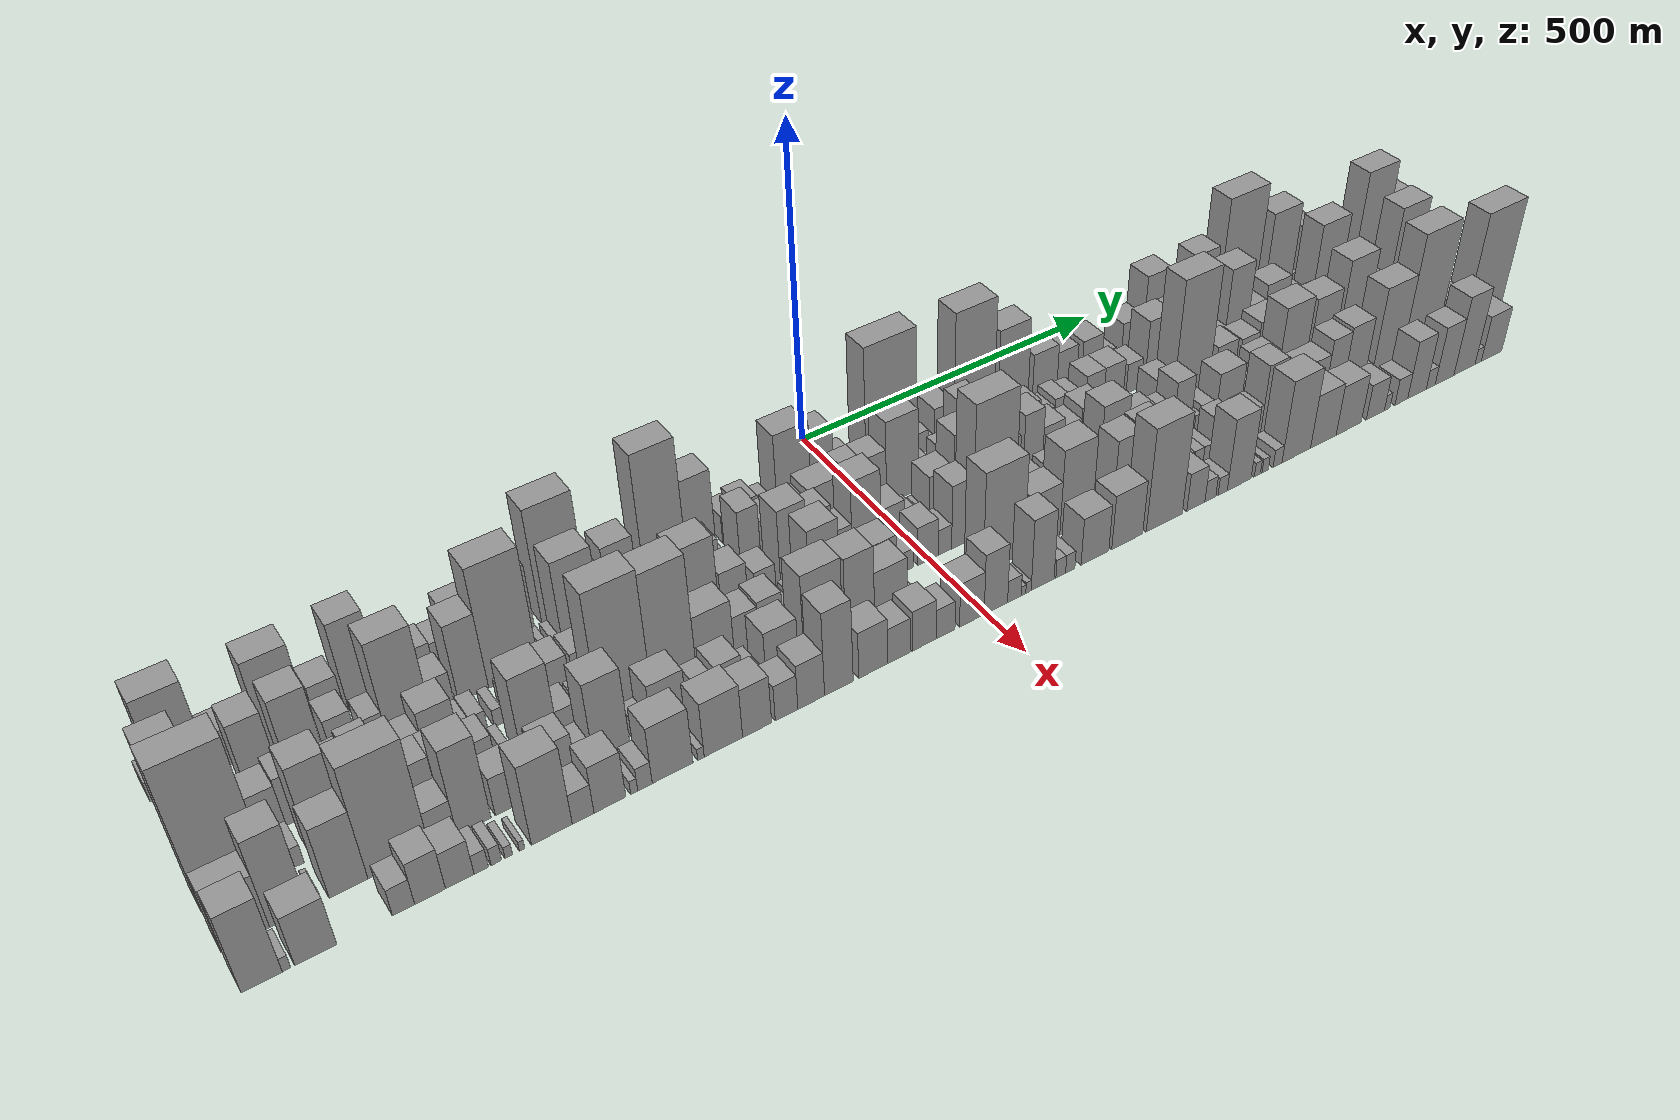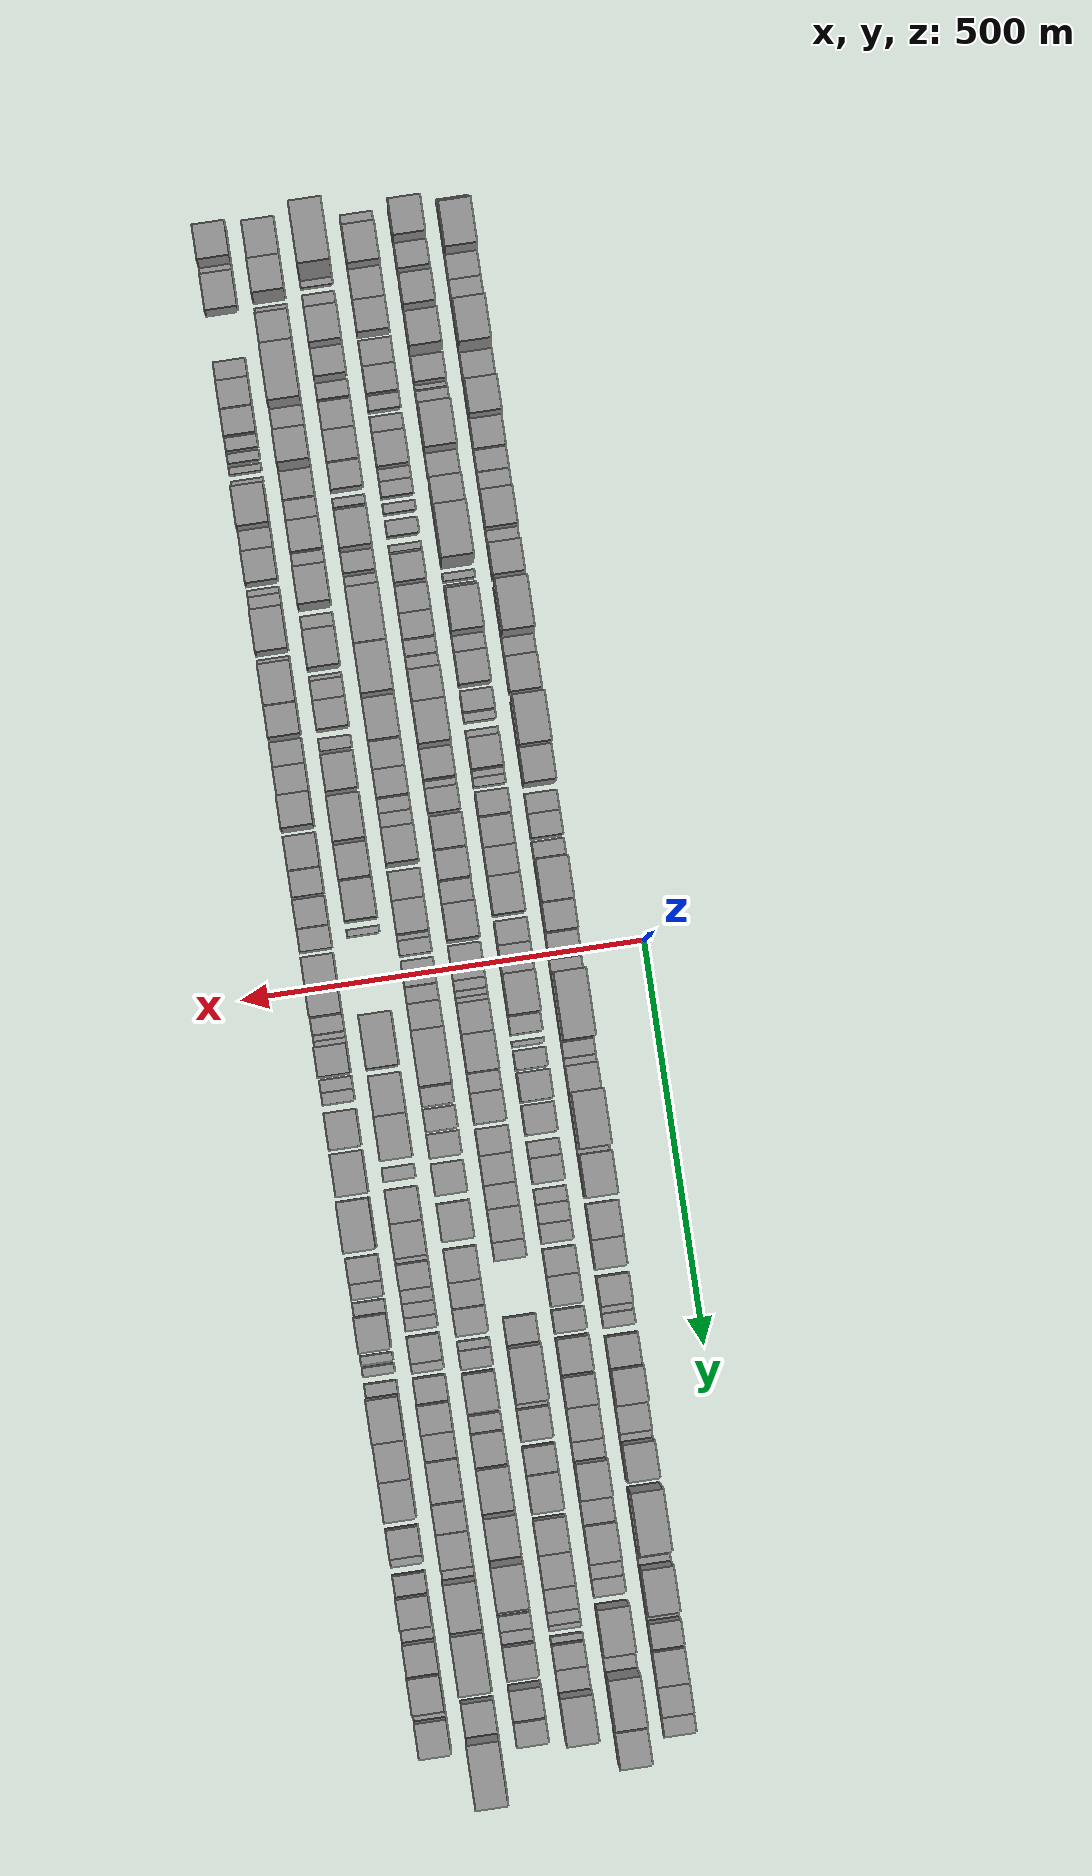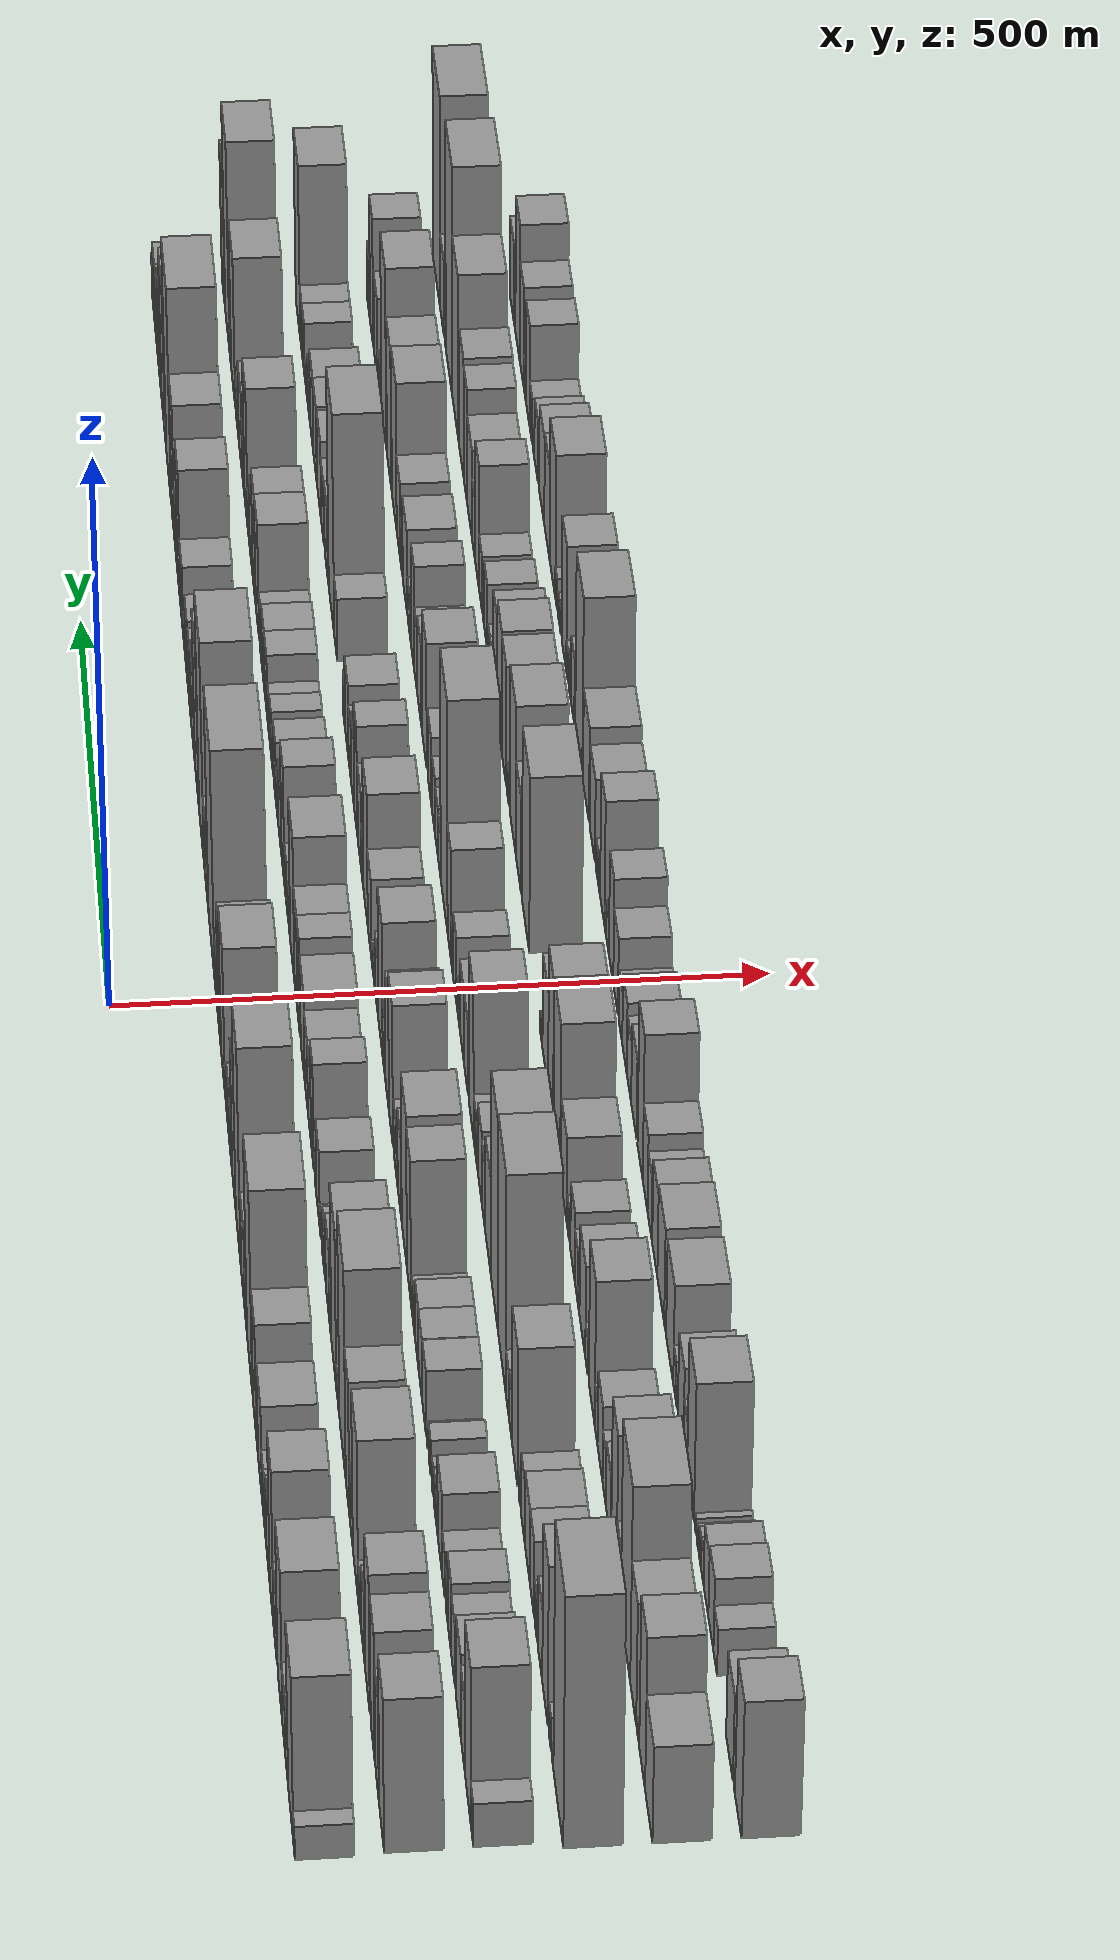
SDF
<sdf version="1.6">
 <world name="default">
  <scene>
   <sky><clouds><speed>12</speed></clouds></sky>
   <ambient>0.4 0.4 0.4 1</ambient>
   <background>0.7 0.7 0.7 1</background>
   <shadows>1</shadows>
  </scene>
  <gravity>0 0 -9.8066</gravity>
  <magnetic_field>6e-06 2.3e-05 -4.2e-05</magnetic_field>
  <physics default="0" name="default_physics" type="ode">
   <ode>
    <solver>
     <type>quick</type>
     <iters>10</iters>
     <sor>1.0</sor>
     <use_dynamic_moi_rescaling>0</use_dynamic_moi_rescaling>
    </solver>
    <constraints>
     <cfm>0</cfm>
     <erp>0.2</erp>
     <contact_max_correcting_vel>100</contact_max_correcting_vel>
     <contact_surface_layer>0.001</contact_surface_layer>
    </constraints>
   </ode>
   <max_step_size>0.004</max_step_size>
   <real_time_factor>1</real_time_factor>
   <real_time_update_rate>250</real_time_update_rate>
  </physics>
  <light name="sun" type="directional">
   <pose>0 0 10 0 0 0</pose>
   <diffuse>0.8 0.8 0.8 1</diffuse>
   <specular>0.2 0.2 0.2 1</specular>
   <attenuation>
    <range>1000</range>
    <constant>0.9</constant>
    <linear>0.01</linear>
    <quadratic>0.001</quadratic>
   </attenuation>
   <direction>-0.5 0.1 -0.9</direction>
  </light>
  <model name="building_1">
   <static>1</static>
   <pose>100.0000 -929.3016 0 0.000000 0.000000 0.000000</pose>
   <link name="link">
    <pose>0 0 15.00 0 0 0</pose>
    <collision name="collision"><geometry><box><size>40.0000 15.3967 30.0000</size></box></geometry></collision>
    <visual name="visual">
     <cast_shadows>0</cast_shadows>
     <geometry><box><size>40.0000 15.3967 30.0000</size></box></geometry>
     <material>
      <script>
       <uri>model://grey_wall/materials/scripts</uri>
       <uri>model://grey_wall/materials/textures</uri>
       <name>vrc/grey_wall</name>
      </script>
     </material>
    </visual>
   </link>
  </model>
  <model name="building_2">
   <static>1</static>
   <pose>100.0000 -893.4922 0 0.000000 0.000000 0.000000</pose>
   <link name="link">
    <pose>0 0 75.00 0 0 0</pose>
    <collision name="collision"><geometry><box><size>40.0000 56.2221 150.0000</size></box></geometry></collision>
    <visual name="visual">
     <cast_shadows>0</cast_shadows>
     <geometry><box><size>40.0000 56.2221 150.0000</size></box></geometry>
     <material>
      <script>
       <uri>model://grey_wall/materials/scripts</uri>
       <uri>model://grey_wall/materials/textures</uri>
       <name>vrc/grey_wall</name>
      </script>
     </material>
    </visual>
   </link>
  </model>
  <model name="building_3">
   <static>1</static>
   <pose>100.0000 -849.8862 0 0.000000 0.000000 0.000000</pose>
   <link name="link">
    <pose>0 0 28.50 0 0 0</pose>
    <collision name="collision"><geometry><box><size>40.0000 30.9899 57.0000</size></box></geometry></collision>
    <visual name="visual">
     <cast_shadows>0</cast_shadows>
     <geometry><box><size>40.0000 30.9899 57.0000</size></box></geometry>
     <material>
      <script>
       <uri>model://grey_wall/materials/scripts</uri>
       <uri>model://grey_wall/materials/textures</uri>
       <name>vrc/grey_wall</name>
      </script>
     </material>
    </visual>
   </link>
  </model>
  <model name="building_4">
   <static>1</static>
   <pose>100.0000 -818.9883 0 0.000000 0.000000 0.000000</pose>
   <link name="link">
    <pose>0 0 28.50 0 0 0</pose>
    <collision name="collision"><geometry><box><size>40.0000 30.8057 57.0000</size></box></geometry></collision>
    <visual name="visual">
     <cast_shadows>0</cast_shadows>
     <geometry><box><size>40.0000 30.8057 57.0000</size></box></geometry>
     <material>
      <script>
       <uri>model://grey_wall/materials/scripts</uri>
       <uri>model://grey_wall/materials/textures</uri>
       <name>vrc/grey_wall</name>
      </script>
     </material>
    </visual>
   </link>
  </model>
  <model name="building_5">
   <static>1</static>
   <pose>100.0000 -776.6667 0 0.000000 0.000000 0.000000</pose>
   <link name="link">
    <pose>0 0 69.00 0 0 0</pose>
    <collision name="collision"><geometry><box><size>40.0000 53.8375 138.0000</size></box></geometry></collision>
    <visual name="visual">
     <cast_shadows>0</cast_shadows>
     <geometry><box><size>40.0000 53.8375 138.0000</size></box></geometry>
     <material>
      <script>
       <uri>model://grey_wall/materials/scripts</uri>
       <uri>model://grey_wall/materials/textures</uri>
       <name>vrc/grey_wall</name>
      </script>
     </material>
    </visual>
   </link>
  </model>
  <model name="building_6">
   <static>1</static>
   <pose>100.0000 -726.1244 0 0.000000 0.000000 0.000000</pose>
   <link name="link">
    <pose>0 0 31.50 0 0 0</pose>
    <collision name="collision"><geometry><box><size>40.0000 35.2472 63.0000</size></box></geometry></collision>
    <visual name="visual">
     <cast_shadows>0</cast_shadows>
     <geometry><box><size>40.0000 35.2472 63.0000</size></box></geometry>
     <material>
      <script>
       <uri>model://grey_wall/materials/scripts</uri>
       <uri>model://grey_wall/materials/textures</uri>
       <name>vrc/grey_wall</name>
      </script>
     </material>
    </visual>
   </link>
  </model>
  <model name="building_7">
   <static>1</static>
   <pose>100.0000 -683.0421 0 0.000000 0.000000 0.000000</pose>
   <link name="link">
    <pose>0 0 70.50 0 0 0</pose>
    <collision name="collision"><geometry><box><size>40.0000 42.9173 141.0000</size></box></geometry></collision>
    <visual name="visual">
     <cast_shadows>0</cast_shadows>
     <geometry><box><size>40.0000 42.9173 141.0000</size></box></geometry>
     <material>
      <script>
       <uri>model://grey_wall/materials/scripts</uri>
       <uri>model://grey_wall/materials/textures</uri>
       <name>vrc/grey_wall</name>
      </script>
     </material>
    </visual>
   </link>
  </model>
  <model name="building_8">
   <static>1</static>
   <pose>100.0000 -642.8256 0 0.000000 0.000000 0.000000</pose>
   <link name="link">
    <pose>0 0 34.50 0 0 0</pose>
    <collision name="collision"><geometry><box><size>40.0000 37.5158 69.0000</size></box></geometry></collision>
    <visual name="visual">
     <cast_shadows>0</cast_shadows>
     <geometry><box><size>40.0000 37.5158 69.0000</size></box></geometry>
     <material>
      <script>
       <uri>model://grey_wall/materials/scripts</uri>
       <uri>model://grey_wall/materials/textures</uri>
       <name>vrc/grey_wall</name>
      </script>
     </material>
    </visual>
   </link>
  </model>
  <model name="building_9">
   <static>1</static>
   <pose>100.0000 -610.5062 0 0.000000 0.000000 0.000000</pose>
   <link name="link">
    <pose>0 0 25.50 0 0 0</pose>
    <collision name="collision"><geometry><box><size>40.0000 27.1230 51.0000</size></box></geometry></collision>
    <visual name="visual">
     <cast_shadows>0</cast_shadows>
     <geometry><box><size>40.0000 27.1230 51.0000</size></box></geometry>
     <material>
      <script>
       <uri>model://grey_wall/materials/scripts</uri>
       <uri>model://grey_wall/materials/textures</uri>
       <name>vrc/grey_wall</name>
      </script>
     </material>
    </visual>
   </link>
  </model>
  <model name="building_10">
   <static>1</static>
   <pose>100.0000 -584.9254 0 0.000000 0.000000 0.000000</pose>
   <link name="link">
    <pose>0 0 24.00 0 0 0</pose>
    <collision name="collision"><geometry><box><size>40.0000 24.0384 48.0000</size></box></geometry></collision>
    <visual name="visual">
     <cast_shadows>0</cast_shadows>
     <geometry><box><size>40.0000 24.0384 48.0000</size></box></geometry>
     <material>
      <script>
       <uri>model://grey_wall/materials/scripts</uri>
       <uri>model://grey_wall/materials/textures</uri>
       <name>vrc/grey_wall</name>
      </script>
     </material>
    </visual>
   </link>
  </model>
  <model name="building_11">
   <static>1</static>
   <pose>100.0000 -549.3161 0 0.000000 0.000000 0.000000</pose>
   <link name="link">
    <pose>0 0 43.50 0 0 0</pose>
    <collision name="collision"><geometry><box><size>40.0000 47.1803 87.0000</size></box></geometry></collision>
    <visual name="visual">
     <cast_shadows>0</cast_shadows>
     <geometry><box><size>40.0000 47.1803 87.0000</size></box></geometry>
     <material>
      <script>
       <uri>model://grey_wall/materials/scripts</uri>
       <uri>model://grey_wall/materials/textures</uri>
       <name>vrc/grey_wall</name>
      </script>
     </material>
    </visual>
   </link>
  </model>
  <model name="building_12">
   <static>1</static>
   <pose>100.0000 -515.8294 0 0.000000 0.000000 0.000000</pose>
   <link name="link">
    <pose>0 0 16.50 0 0 0</pose>
    <collision name="collision"><geometry><box><size>40.0000 19.7931 33.0000</size></box></geometry></collision>
    <visual name="visual">
     <cast_shadows>0</cast_shadows>
     <geometry><box><size>40.0000 19.7931 33.0000</size></box></geometry>
     <material>
      <script>
       <uri>model://grey_wall/materials/scripts</uri>
       <uri>model://grey_wall/materials/textures</uri>
       <name>vrc/grey_wall</name>
      </script>
     </material>
    </visual>
   </link>
  </model>
  <model name="building_13">
   <static>1</static>
   <pose>100.0000 -486.1021 0 0.000000 0.000000 0.000000</pose>
   <link name="link">
    <pose>0 0 52.50 0 0 0</pose>
    <collision name="collision"><geometry><box><size>40.0000 39.6614 105.0000</size></box></geometry></collision>
    <visual name="visual">
     <cast_shadows>0</cast_shadows>
     <geometry><box><size>40.0000 39.6614 105.0000</size></box></geometry>
     <material>
      <script>
       <uri>model://grey_wall/materials/scripts</uri>
       <uri>model://grey_wall/materials/textures</uri>
       <name>vrc/grey_wall</name>
      </script>
     </material>
    </visual>
   </link>
  </model>
  <model name="building_14">
   <static>1</static>
   <pose>100.0000 -424.4190 0 0.000000 0.000000 0.000000</pose>
   <link name="link">
    <pose>0 0 93.00 0 0 0</pose>
    <collision name="collision"><geometry><box><size>40.0000 63.7049 186.0000</size></box></geometry></collision>
    <visual name="visual">
     <cast_shadows>0</cast_shadows>
     <geometry><box><size>40.0000 63.7049 186.0000</size></box></geometry>
     <material>
      <script>
       <uri>model://grey_wall/materials/scripts</uri>
       <uri>model://grey_wall/materials/textures</uri>
       <name>vrc/grey_wall</name>
      </script>
     </material>
    </visual>
   </link>
  </model>
  <model name="building_15">
   <static>1</static>
   <pose>100.0000 -380.0827 0 0.000000 0.000000 0.000000</pose>
   <link name="link">
    <pose>0 0 21.00 0 0 0</pose>
    <collision name="collision"><geometry><box><size>40.0000 24.9676 42.0000</size></box></geometry></collision>
    <visual name="visual">
     <cast_shadows>0</cast_shadows>
     <geometry><box><size>40.0000 24.9676 42.0000</size></box></geometry>
     <material>
      <script>
       <uri>model://grey_wall/materials/scripts</uri>
       <uri>model://grey_wall/materials/textures</uri>
       <name>vrc/grey_wall</name>
      </script>
     </material>
    </visual>
   </link>
  </model>
  <model name="building_16">
   <static>1</static>
   <pose>100.0000 -345.6989 0 0.000000 0.000000 0.000000</pose>
   <link name="link">
    <pose>0 0 39.00 0 0 0</pose>
    <collision name="collision"><geometry><box><size>40.0000 43.8001 78.0000</size></box></geometry></collision>
    <visual name="visual">
     <cast_shadows>0</cast_shadows>
     <geometry><box><size>40.0000 43.8001 78.0000</size></box></geometry>
     <material>
      <script>
       <uri>model://grey_wall/materials/scripts</uri>
       <uri>model://grey_wall/materials/textures</uri>
       <name>vrc/grey_wall</name>
      </script>
     </material>
    </visual>
   </link>
  </model>
  <model name="building_17">
   <static>1</static>
   <pose>100.0000 -283.1865 0 0.000000 0.000000 0.000000</pose>
   <link name="link">
    <pose>0 0 100.50 0 0 0</pose>
    <collision name="collision"><geometry><box><size>40.0000 61.2247 201.0000</size></box></geometry></collision>
    <visual name="visual">
     <cast_shadows>0</cast_shadows>
     <geometry><box><size>40.0000 61.2247 201.0000</size></box></geometry>
     <material>
      <script>
       <uri>model://grey_wall/materials/scripts</uri>
       <uri>model://grey_wall/materials/textures</uri>
       <name>vrc/grey_wall</name>
      </script>
     </material>
    </visual>
   </link>
  </model>
  <model name="building_18">
   <static>1</static>
   <pose>100.0000 -230.8373 0 0.000000 0.000000 0.000000</pose>
   <link name="link">
    <pose>0 0 64.50 0 0 0</pose>
    <collision name="collision"><geometry><box><size>40.0000 43.4737 129.0000</size></box></geometry></collision>
    <visual name="visual">
     <cast_shadows>0</cast_shadows>
     <geometry><box><size>40.0000 43.4737 129.0000</size></box></geometry>
     <material>
      <script>
       <uri>model://grey_wall/materials/scripts</uri>
       <uri>model://grey_wall/materials/textures</uri>
       <name>vrc/grey_wall</name>
      </script>
     </material>
    </visual>
   </link>
  </model>
  <model name="building_19">
   <static>1</static>
   <pose>100.0000 -186.5573 0 0.000000 0.000000 0.000000</pose>
   <link name="link">
    <pose>0 0 22.50 0 0 0</pose>
    <collision name="collision"><geometry><box><size>40.0000 25.0863 45.0000</size></box></geometry></collision>
    <visual name="visual">
     <cast_shadows>0</cast_shadows>
     <geometry><box><size>40.0000 25.0863 45.0000</size></box></geometry>
     <material>
      <script>
       <uri>model://grey_wall/materials/scripts</uri>
       <uri>model://grey_wall/materials/textures</uri>
       <name>vrc/grey_wall</name>
      </script>
     </material>
    </visual>
   </link>
  </model>
  <model name="building_20">
   <static>1</static>
   <pose>100.0000 -158.9366 0 0.000000 0.000000 0.000000</pose>
   <link name="link">
    <pose>0 0 27.00 0 0 0</pose>
    <collision name="collision"><geometry><box><size>40.0000 30.1553 54.0000</size></box></geometry></collision>
    <visual name="visual">
     <cast_shadows>0</cast_shadows>
     <geometry><box><size>40.0000 30.1553 54.0000</size></box></geometry>
     <material>
      <script>
       <uri>model://grey_wall/materials/scripts</uri>
       <uri>model://grey_wall/materials/textures</uri>
       <name>vrc/grey_wall</name>
      </script>
     </material>
    </visual>
   </link>
  </model>
  <model name="building_21">
   <static>1</static>
   <pose>100.0000 -129.6776 0 0.000000 0.000000 0.000000</pose>
   <link name="link">
    <pose>0 0 18.00 0 0 0</pose>
    <collision name="collision"><geometry><box><size>40.0000 20.3625 36.0000</size></box></geometry></collision>
    <visual name="visual">
     <cast_shadows>0</cast_shadows>
     <geometry><box><size>40.0000 20.3625 36.0000</size></box></geometry>
     <material>
      <script>
       <uri>model://grey_wall/materials/scripts</uri>
       <uri>model://grey_wall/materials/textures</uri>
       <name>vrc/grey_wall</name>
      </script>
     </material>
    </visual>
   </link>
  </model>
  <model name="building_22">
   <static>1</static>
   <pose>100.0000 -89.0417 0 0.000000 0.000000 0.000000</pose>
   <link name="link">
    <pose>0 0 69.00 0 0 0</pose>
    <collision name="collision"><geometry><box><size>40.0000 52.9093 138.0000</size></box></geometry></collision>
    <visual name="visual">
     <cast_shadows>0</cast_shadows>
     <geometry><box><size>40.0000 52.9093 138.0000</size></box></geometry>
     <material>
      <script>
       <uri>model://grey_wall/materials/scripts</uri>
       <uri>model://grey_wall/materials/textures</uri>
       <name>vrc/grey_wall</name>
      </script>
     </material>
    </visual>
   </link>
  </model>
  <model name="building_23">
   <static>1</static>
   <pose>100.0000 -44.6162 0 0.000000 0.000000 0.000000</pose>
   <link name="link">
    <pose>0 0 57.00 0 0 0</pose>
    <collision name="collision"><geometry><box><size>40.0000 35.9416 114.0000</size></box></geometry></collision>
    <visual name="visual">
     <cast_shadows>0</cast_shadows>
     <geometry><box><size>40.0000 35.9416 114.0000</size></box></geometry>
     <material>
      <script>
       <uri>model://grey_wall/materials/scripts</uri>
       <uri>model://grey_wall/materials/textures</uri>
       <name>vrc/grey_wall</name>
      </script>
     </material>
    </visual>
   </link>
  </model>
  <model name="building_24">
   <static>1</static>
   <pose>100.0000 -10.5844 0 0.000000 0.000000 0.000000</pose>
   <link name="link">
    <pose>0 0 27.00 0 0 0</pose>
    <collision name="collision"><geometry><box><size>40.0000 32.1220 54.0000</size></box></geometry></collision>
    <visual name="visual">
     <cast_shadows>0</cast_shadows>
     <geometry><box><size>40.0000 32.1220 54.0000</size></box></geometry>
     <material>
      <script>
       <uri>model://grey_wall/materials/scripts</uri>
       <uri>model://grey_wall/materials/textures</uri>
       <name>vrc/grey_wall</name>
      </script>
     </material>
    </visual>
   </link>
  </model>
  <model name="building_25">
   <static>1</static>
   <pose>100.0000 14.9822 0 0.000000 0.000000 0.000000</pose>
   <link name="link">
    <pose>0 0 16.50 0 0 0</pose>
    <collision name="collision"><geometry><box><size>40.0000 19.0114 33.0000</size></box></geometry></collision>
    <visual name="visual">
     <cast_shadows>0</cast_shadows>
     <geometry><box><size>40.0000 19.0114 33.0000</size></box></geometry>
     <material>
      <script>
       <uri>model://grey_wall/materials/scripts</uri>
       <uri>model://grey_wall/materials/textures</uri>
       <name>vrc/grey_wall</name>
      </script>
     </material>
    </visual>
   </link>
  </model>
  <model name="building_26">
   <static>1</static>
   <pose>100.0000 66.0250 0 0.000000 0.000000 0.000000</pose>
   <link name="link">
    <pose>0 0 108.00 0 0 0</pose>
    <collision name="collision"><geometry><box><size>40.0000 83.0741 216.0000</size></box></geometry></collision>
    <visual name="visual">
     <cast_shadows>0</cast_shadows>
     <geometry><box><size>40.0000 83.0741 216.0000</size></box></geometry>
     <material>
      <script>
       <uri>model://grey_wall/materials/scripts</uri>
       <uri>model://grey_wall/materials/textures</uri>
       <name>vrc/grey_wall</name>
      </script>
     </material>
    </visual>
   </link>
  </model>
  <model name="building_27">
   <static>1</static>
   <pose>100.0000 117.6457 0 0.000000 0.000000 0.000000</pose>
   <link name="link">
    <pose>0 0 18.00 0 0 0</pose>
    <collision name="collision"><geometry><box><size>40.0000 20.1674 36.0000</size></box></geometry></collision>
    <visual name="visual">
     <cast_shadows>0</cast_shadows>
     <geometry><box><size>40.0000 20.1674 36.0000</size></box></geometry>
     <material>
      <script>
       <uri>model://grey_wall/materials/scripts</uri>
       <uri>model://grey_wall/materials/textures</uri>
       <name>vrc/grey_wall</name>
      </script>
     </material>
    </visual>
   </link>
  </model>
  <model name="building_28">
   <static>1</static>
   <pose>100.0000 132.5284 0 0.000000 0.000000 0.000000</pose>
   <link name="link">
    <pose>0 0 10.50 0 0 0</pose>
    <collision name="collision"><geometry><box><size>40.0000 9.5981 21.0000</size></box></geometry></collision>
    <visual name="visual">
     <cast_shadows>0</cast_shadows>
     <geometry><box><size>40.0000 9.5981 21.0000</size></box></geometry>
     <material>
      <script>
       <uri>model://grey_wall/materials/scripts</uri>
       <uri>model://grey_wall/materials/textures</uri>
       <name>vrc/grey_wall</name>
      </script>
     </material>
    </visual>
   </link>
  </model>
  <model name="building_29">
   <static>1</static>
   <pose>100.0000 154.0062 0 0.000000 0.000000 0.000000</pose>
   <link name="link">
    <pose>0 0 33.00 0 0 0</pose>
    <collision name="collision"><geometry><box><size>40.0000 33.3574 66.0000</size></box></geometry></collision>
    <visual name="visual">
     <cast_shadows>0</cast_shadows>
     <geometry><box><size>40.0000 33.3574 66.0000</size></box></geometry>
     <material>
      <script>
       <uri>model://grey_wall/materials/scripts</uri>
       <uri>model://grey_wall/materials/textures</uri>
       <name>vrc/grey_wall</name>
      </script>
     </material>
    </visual>
   </link>
  </model>
  <model name="building_30">
   <static>1</static>
   <pose>100.0000 205.2229 0 0.000000 0.000000 0.000000</pose>
   <link name="link">
    <pose>0 0 105.00 0 0 0</pose>
    <collision name="collision"><geometry><box><size>40.0000 69.0760 210.0000</size></box></geometry></collision>
    <visual name="visual">
     <cast_shadows>0</cast_shadows>
     <geometry><box><size>40.0000 69.0760 210.0000</size></box></geometry>
     <material>
      <script>
       <uri>model://grey_wall/materials/scripts</uri>
       <uri>model://grey_wall/materials/textures</uri>
       <name>vrc/grey_wall</name>
      </script>
     </material>
    </visual>
   </link>
  </model>
  <model name="building_31">
   <static>1</static>
   <pose>100.0000 243.1229 0 0.000000 0.000000 0.000000</pose>
   <link name="link">
    <pose>0 0 7.50 0 0 0</pose>
    <collision name="collision"><geometry><box><size>40.0000 6.7242 15.0000</size></box></geometry></collision>
    <visual name="visual">
     <cast_shadows>0</cast_shadows>
     <geometry><box><size>40.0000 6.7242 15.0000</size></box></geometry>
     <material>
      <script>
       <uri>model://grey_wall/materials/scripts</uri>
       <uri>model://grey_wall/materials/textures</uri>
       <name>vrc/grey_wall</name>
      </script>
     </material>
    </visual>
   </link>
  </model>
  <model name="building_32">
   <static>1</static>
   <pose>100.0000 273.0305 0 0.000000 0.000000 0.000000</pose>
   <link name="link">
    <pose>0 0 75.00 0 0 0</pose>
    <collision name="collision"><geometry><box><size>40.0000 53.0909 150.0000</size></box></geometry></collision>
    <visual name="visual">
     <cast_shadows>0</cast_shadows>
     <geometry><box><size>40.0000 53.0909 150.0000</size></box></geometry>
     <material>
      <script>
       <uri>model://grey_wall/materials/scripts</uri>
       <uri>model://grey_wall/materials/textures</uri>
       <name>vrc/grey_wall</name>
      </script>
     </material>
    </visual>
   </link>
  </model>
  <model name="building_33">
   <static>1</static>
   <pose>100.0000 329.7038 0 0.000000 0.000000 0.000000</pose>
   <link name="link">
    <pose>0 0 42.00 0 0 0</pose>
    <collision name="collision"><geometry><box><size>40.0000 44.2558 84.0000</size></box></geometry></collision>
    <visual name="visual">
     <cast_shadows>0</cast_shadows>
     <geometry><box><size>40.0000 44.2558 84.0000</size></box></geometry>
     <material>
      <script>
       <uri>model://grey_wall/materials/scripts</uri>
       <uri>model://grey_wall/materials/textures</uri>
       <name>vrc/grey_wall</name>
      </script>
     </material>
    </visual>
   </link>
  </model>
  <model name="building_34">
   <static>1</static>
   <pose>100.0000 370.0031 0 0.000000 0.000000 0.000000</pose>
   <link name="link">
    <pose>0 0 34.50 0 0 0</pose>
    <collision name="collision"><geometry><box><size>40.0000 36.3429 69.0000</size></box></geometry></collision>
    <visual name="visual">
     <cast_shadows>0</cast_shadows>
     <geometry><box><size>40.0000 36.3429 69.0000</size></box></geometry>
     <material>
      <script>
       <uri>model://grey_wall/materials/scripts</uri>
       <uri>model://grey_wall/materials/textures</uri>
       <name>vrc/grey_wall</name>
      </script>
     </material>
    </visual>
   </link>
  </model>
  <model name="building_35">
   <static>1</static>
   <pose>100.0000 415.5431 0 0.000000 0.000000 0.000000</pose>
   <link name="link">
    <pose>0 0 34.50 0 0 0</pose>
    <collision name="collision"><geometry><box><size>40.0000 36.7370 69.0000</size></box></geometry></collision>
    <visual name="visual">
     <cast_shadows>0</cast_shadows>
     <geometry><box><size>40.0000 36.7370 69.0000</size></box></geometry>
     <material>
      <script>
       <uri>model://grey_wall/materials/scripts</uri>
       <uri>model://grey_wall/materials/textures</uri>
       <name>vrc/grey_wall</name>
      </script>
     </material>
    </visual>
   </link>
  </model>
  <model name="building_36">
   <static>1</static>
   <pose>100.0000 438.5779 0 0.000000 0.000000 0.000000</pose>
   <link name="link">
    <pose>0 0 10.50 0 0 0</pose>
    <collision name="collision"><geometry><box><size>40.0000 9.3328 21.0000</size></box></geometry></collision>
    <visual name="visual">
     <cast_shadows>0</cast_shadows>
     <geometry><box><size>40.0000 9.3328 21.0000</size></box></geometry>
     <material>
      <script>
       <uri>model://grey_wall/materials/scripts</uri>
       <uri>model://grey_wall/materials/textures</uri>
       <name>vrc/grey_wall</name>
      </script>
     </material>
    </visual>
   </link>
  </model>
  <model name="building_37">
   <static>1</static>
   <pose>100.0000 452.0963 0 0.000000 0.000000 0.000000</pose>
   <link name="link">
    <pose>0 0 16.50 0 0 0</pose>
    <collision name="collision"><geometry><box><size>40.0000 17.7041 33.0000</size></box></geometry></collision>
    <visual name="visual">
     <cast_shadows>0</cast_shadows>
     <geometry><box><size>40.0000 17.7041 33.0000</size></box></geometry>
     <material>
      <script>
       <uri>model://grey_wall/materials/scripts</uri>
       <uri>model://grey_wall/materials/textures</uri>
       <name>vrc/grey_wall</name>
      </script>
     </material>
    </visual>
   </link>
  </model>
  <model name="building_38">
   <static>1</static>
   <pose>100.0000 490.6179 0 0.000000 0.000000 0.000000</pose>
   <link name="link">
    <pose>0 0 34.50 0 0 0</pose>
    <collision name="collision"><geometry><box><size>40.0000 39.3390 69.0000</size></box></geometry></collision>
    <visual name="visual">
     <cast_shadows>0</cast_shadows>
     <geometry><box><size>40.0000 39.3390 69.0000</size></box></geometry>
     <material>
      <script>
       <uri>model://grey_wall/materials/scripts</uri>
       <uri>model://grey_wall/materials/textures</uri>
       <name>vrc/grey_wall</name>
      </script>
     </material>
    </visual>
   </link>
  </model>
  <model name="building_39">
   <static>1</static>
   <pose>100.0000 532.4192 0 0.000000 0.000000 0.000000</pose>
   <link name="link">
    <pose>0 0 67.50 0 0 0</pose>
    <collision name="collision"><geometry><box><size>40.0000 44.2637 135.0000</size></box></geometry></collision>
    <visual name="visual">
     <cast_shadows>0</cast_shadows>
     <geometry><box><size>40.0000 44.2637 135.0000</size></box></geometry>
     <material>
      <script>
       <uri>model://grey_wall/materials/scripts</uri>
       <uri>model://grey_wall/materials/textures</uri>
       <name>vrc/grey_wall</name>
      </script>
     </material>
    </visual>
   </link>
  </model>
  <model name="building_40">
   <static>1</static>
   <pose>100.0000 572.9199 0 0.000000 0.000000 0.000000</pose>
   <link name="link">
    <pose>0 0 31.50 0 0 0</pose>
    <collision name="collision"><geometry><box><size>40.0000 36.7376 63.0000</size></box></geometry></collision>
    <visual name="visual">
     <cast_shadows>0</cast_shadows>
     <geometry><box><size>40.0000 36.7376 63.0000</size></box></geometry>
     <material>
      <script>
       <uri>model://grey_wall/materials/scripts</uri>
       <uri>model://grey_wall/materials/textures</uri>
       <name>vrc/grey_wall</name>
      </script>
     </material>
    </visual>
   </link>
  </model>
  <model name="building_41">
   <static>1</static>
   <pose>100.0000 596.5250 0 0.000000 0.000000 0.000000</pose>
   <link name="link">
    <pose>0 0 10.50 0 0 0</pose>
    <collision name="collision"><geometry><box><size>40.0000 10.4726 21.0000</size></box></geometry></collision>
    <visual name="visual">
     <cast_shadows>0</cast_shadows>
     <geometry><box><size>40.0000 10.4726 21.0000</size></box></geometry>
     <material>
      <script>
       <uri>model://grey_wall/materials/scripts</uri>
       <uri>model://grey_wall/materials/textures</uri>
       <name>vrc/grey_wall</name>
      </script>
     </material>
    </visual>
   </link>
  </model>
  <model name="building_42">
   <static>1</static>
   <pose>100.0000 624.8294 0 0.000000 0.000000 0.000000</pose>
   <link name="link">
    <pose>0 0 67.50 0 0 0</pose>
    <collision name="collision"><geometry><box><size>40.0000 46.1362 135.0000</size></box></geometry></collision>
    <visual name="visual">
     <cast_shadows>0</cast_shadows>
     <geometry><box><size>40.0000 46.1362 135.0000</size></box></geometry>
     <material>
      <script>
       <uri>model://grey_wall/materials/scripts</uri>
       <uri>model://grey_wall/materials/textures</uri>
       <name>vrc/grey_wall</name>
      </script>
     </material>
    </visual>
   </link>
  </model>
  <model name="building_43">
   <static>1</static>
   <pose>100.0000 696.2283 0 0.000000 0.000000 0.000000</pose>
   <link name="link">
    <pose>0 0 105.00 0 0 0</pose>
    <collision name="collision"><geometry><box><size>40.0000 76.6616 210.0000</size></box></geometry></collision>
    <visual name="visual">
     <cast_shadows>0</cast_shadows>
     <geometry><box><size>40.0000 76.6616 210.0000</size></box></geometry>
     <material>
      <script>
       <uri>model://grey_wall/materials/scripts</uri>
       <uri>model://grey_wall/materials/textures</uri>
       <name>vrc/grey_wall</name>
      </script>
     </material>
    </visual>
   </link>
  </model>
  <model name="building_44">
   <static>1</static>
   <pose>100.0000 739.7841 0 0.000000 0.000000 0.000000</pose>
   <link name="link">
    <pose>0 0 10.50 0 0 0</pose>
    <collision name="collision"><geometry><box><size>40.0000 10.4501 21.0000</size></box></geometry></collision>
    <visual name="visual">
     <cast_shadows>0</cast_shadows>
     <geometry><box><size>40.0000 10.4501 21.0000</size></box></geometry>
     <material>
      <script>
       <uri>model://grey_wall/materials/scripts</uri>
       <uri>model://grey_wall/materials/textures</uri>
       <name>vrc/grey_wall</name>
      </script>
     </material>
    </visual>
   </link>
  </model>
  <model name="building_45">
   <static>1</static>
   <pose>100.0000 749.6414 0 0.000000 0.000000 0.000000</pose>
   <link name="link">
    <pose>0 0 10.50 0 0 0</pose>
    <collision name="collision"><geometry><box><size>40.0000 9.2644 21.0000</size></box></geometry></collision>
    <visual name="visual">
     <cast_shadows>0</cast_shadows>
     <geometry><box><size>40.0000 9.2644 21.0000</size></box></geometry>
     <material>
      <script>
       <uri>model://grey_wall/materials/scripts</uri>
       <uri>model://grey_wall/materials/textures</uri>
       <name>vrc/grey_wall</name>
      </script>
     </material>
    </visual>
   </link>
  </model>
  <model name="building_46">
   <static>1</static>
   <pose>100.0000 782.7369 0 0.000000 0.000000 0.000000</pose>
   <link name="link">
    <pose>0 0 75.00 0 0 0</pose>
    <collision name="collision"><geometry><box><size>40.0000 56.9267 150.0000</size></box></geometry></collision>
    <visual name="visual">
     <cast_shadows>0</cast_shadows>
     <geometry><box><size>40.0000 56.9267 150.0000</size></box></geometry>
     <material>
      <script>
       <uri>model://grey_wall/materials/scripts</uri>
       <uri>model://grey_wall/materials/textures</uri>
       <name>vrc/grey_wall</name>
      </script>
     </material>
    </visual>
   </link>
  </model>
  <model name="building_47">
   <static>1</static>
   <pose>100.0000 816.8088 0 0.000000 0.000000 0.000000</pose>
   <link name="link">
    <pose>0 0 12.00 0 0 0</pose>
    <collision name="collision"><geometry><box><size>40.0000 11.2171 24.0000</size></box></geometry></collision>
    <visual name="visual">
     <cast_shadows>0</cast_shadows>
     <geometry><box><size>40.0000 11.2171 24.0000</size></box></geometry>
     <material>
      <script>
       <uri>model://grey_wall/materials/scripts</uri>
       <uri>model://grey_wall/materials/textures</uri>
       <name>vrc/grey_wall</name>
      </script>
     </material>
    </visual>
   </link>
  </model>
  <model name="building_48">
   <static>1</static>
   <pose>100.0000 838.4634 0 0.000000 0.000000 0.000000</pose>
   <link name="link">
    <pose>0 0 51.00 0 0 0</pose>
    <collision name="collision"><geometry><box><size>40.0000 32.0920 102.0000</size></box></geometry></collision>
    <visual name="visual">
     <cast_shadows>0</cast_shadows>
     <geometry><box><size>40.0000 32.0920 102.0000</size></box></geometry>
     <material>
      <script>
       <uri>model://grey_wall/materials/scripts</uri>
       <uri>model://grey_wall/materials/textures</uri>
       <name>vrc/grey_wall</name>
      </script>
     </material>
    </visual>
   </link>
  </model>
  <model name="building_49">
   <static>1</static>
   <pose>100.0000 880.3595 0 0.000000 0.000000 0.000000</pose>
   <link name="link">
    <pose>0 0 37.50 0 0 0</pose>
    <collision name="collision"><geometry><box><size>40.0000 43.7001 75.0000</size></box></geometry></collision>
    <visual name="visual">
     <cast_shadows>0</cast_shadows>
     <geometry><box><size>40.0000 43.7001 75.0000</size></box></geometry>
     <material>
      <script>
       <uri>model://grey_wall/materials/scripts</uri>
       <uri>model://grey_wall/materials/textures</uri>
       <name>vrc/grey_wall</name>
      </script>
     </material>
    </visual>
   </link>
  </model>
  <model name="building_50">
   <static>1</static>
   <pose>100.0000 920.8104 0 0.000000 0.000000 0.000000</pose>
   <link name="link">
    <pose>0 0 36.00 0 0 0</pose>
    <collision name="collision"><geometry><box><size>40.0000 37.2017 72.0000</size></box></geometry></collision>
    <visual name="visual">
     <cast_shadows>0</cast_shadows>
     <geometry><box><size>40.0000 37.2017 72.0000</size></box></geometry>
     <material>
      <script>
       <uri>model://grey_wall/materials/scripts</uri>
       <uri>model://grey_wall/materials/textures</uri>
       <name>vrc/grey_wall</name>
      </script>
     </material>
    </visual>
   </link>
  </model>
  <model name="building_51">
   <static>1</static>
   <pose>100.0000 952.1875 0 0.000000 0.000000 0.000000</pose>
   <link name="link">
    <pose>0 0 22.50 0 0 0</pose>
    <collision name="collision"><geometry><box><size>40.0000 25.5526 45.0000</size></box></geometry></collision>
    <visual name="visual">
     <cast_shadows>0</cast_shadows>
     <geometry><box><size>40.0000 25.5526 45.0000</size></box></geometry>
     <material>
      <script>
       <uri>model://grey_wall/materials/scripts</uri>
       <uri>model://grey_wall/materials/textures</uri>
       <name>vrc/grey_wall</name>
      </script>
     </material>
    </visual>
   </link>
  </model>
  <model name="building_52">
   <static>1</static>
   <pose>160.0000 -912.4431 0 0.000000 0.000000 0.000000</pose>
   <link name="link">
    <pose>0 0 69.00 0 0 0</pose>
    <collision name="collision"><geometry><box><size>40.0000 45.1138 138.0000</size></box></geometry></collision>
    <visual name="visual">
     <cast_shadows>0</cast_shadows>
     <geometry><box><size>40.0000 45.1138 138.0000</size></box></geometry>
     <material>
      <script>
       <uri>model://grey_wall/materials/scripts</uri>
       <uri>model://grey_wall/materials/textures</uri>
       <name>vrc/grey_wall</name>
      </script>
     </material>
    </visual>
   </link>
  </model>
  <model name="building_53">
   <static>1</static>
   <pose>160.0000 -869.1691 0 0.000000 0.000000 0.000000</pose>
   <link name="link">
    <pose>0 0 46.50 0 0 0</pose>
    <collision name="collision"><geometry><box><size>40.0000 31.4341 93.0000</size></box></geometry></collision>
    <visual name="visual">
     <cast_shadows>0</cast_shadows>
     <geometry><box><size>40.0000 31.4341 93.0000</size></box></geometry>
     <material>
      <script>
       <uri>model://grey_wall/materials/scripts</uri>
       <uri>model://grey_wall/materials/textures</uri>
       <name>vrc/grey_wall</name>
      </script>
     </material>
    </visual>
   </link>
  </model>
  <model name="building_54">
   <static>1</static>
   <pose>160.0000 -826.1210 0 0.000000 0.000000 0.000000</pose>
   <link name="link">
    <pose>0 0 58.50 0 0 0</pose>
    <collision name="collision"><geometry><box><size>40.0000 38.6621 117.0000</size></box></geometry></collision>
    <visual name="visual">
     <cast_shadows>0</cast_shadows>
     <geometry><box><size>40.0000 38.6621 117.0000</size></box></geometry>
     <material>
      <script>
       <uri>model://grey_wall/materials/scripts</uri>
       <uri>model://grey_wall/materials/textures</uri>
       <name>vrc/grey_wall</name>
      </script>
     </material>
    </visual>
   </link>
  </model>
  <model name="building_55">
   <static>1</static>
   <pose>160.0000 -776.3998 0 0.000000 0.000000 0.000000</pose>
   <link name="link">
    <pose>0 0 63.00 0 0 0</pose>
    <collision name="collision"><geometry><box><size>40.0000 42.7803 126.0000</size></box></geometry></collision>
    <visual name="visual">
     <cast_shadows>0</cast_shadows>
     <geometry><box><size>40.0000 42.7803 126.0000</size></box></geometry>
     <material>
      <script>
       <uri>model://grey_wall/materials/scripts</uri>
       <uri>model://grey_wall/materials/textures</uri>
       <name>vrc/grey_wall</name>
      </script>
     </material>
    </visual>
   </link>
  </model>
  <model name="building_56">
   <static>1</static>
   <pose>160.0000 -732.1284 0 0.000000 0.000000 0.000000</pose>
   <link name="link">
    <pose>0 0 31.50 0 0 0</pose>
    <collision name="collision"><geometry><box><size>40.0000 31.7627 63.0000</size></box></geometry></collision>
    <visual name="visual">
     <cast_shadows>0</cast_shadows>
     <geometry><box><size>40.0000 31.7627 63.0000</size></box></geometry>
     <material>
      <script>
       <uri>model://grey_wall/materials/scripts</uri>
       <uri>model://grey_wall/materials/textures</uri>
       <name>vrc/grey_wall</name>
      </script>
     </material>
    </visual>
   </link>
  </model>
  <model name="building_57">
   <static>1</static>
   <pose>160.0000 -713.1230 0 0.000000 0.000000 0.000000</pose>
   <link name="link">
    <pose>0 0 7.50 0 0 0</pose>
    <collision name="collision"><geometry><box><size>40.0000 6.2481 15.0000</size></box></geometry></collision>
    <visual name="visual">
     <cast_shadows>0</cast_shadows>
     <geometry><box><size>40.0000 6.2481 15.0000</size></box></geometry>
     <material>
      <script>
       <uri>model://grey_wall/materials/scripts</uri>
       <uri>model://grey_wall/materials/textures</uri>
       <name>vrc/grey_wall</name>
      </script>
     </material>
    </visual>
   </link>
  </model>
  <model name="building_58">
   <static>1</static>
   <pose>160.0000 -695.3463 0 0.000000 0.000000 0.000000</pose>
   <link name="link">
    <pose>0 0 19.50 0 0 0</pose>
    <collision name="collision"><geometry><box><size>40.0000 23.3052 39.0000</size></box></geometry></collision>
    <visual name="visual">
     <cast_shadows>0</cast_shadows>
     <geometry><box><size>40.0000 23.3052 39.0000</size></box></geometry>
     <material>
      <script>
       <uri>model://grey_wall/materials/scripts</uri>
       <uri>model://grey_wall/materials/textures</uri>
       <name>vrc/grey_wall</name>
      </script>
     </material>
    </visual>
   </link>
  </model>
  <model name="building_59">
   <static>1</static>
   <pose>160.0000 -656.1597 0 0.000000 0.000000 0.000000</pose>
   <link name="link">
    <pose>0 0 73.50 0 0 0</pose>
    <collision name="collision"><geometry><box><size>40.0000 55.0679 147.0000</size></box></geometry></collision>
    <visual name="visual">
     <cast_shadows>0</cast_shadows>
     <geometry><box><size>40.0000 55.0679 147.0000</size></box></geometry>
     <material>
      <script>
       <uri>model://grey_wall/materials/scripts</uri>
       <uri>model://grey_wall/materials/textures</uri>
       <name>vrc/grey_wall</name>
      </script>
     </material>
    </visual>
   </link>
  </model>
  <model name="building_60">
   <static>1</static>
   <pose>160.0000 -613.8279 0 0.000000 0.000000 0.000000</pose>
   <link name="link">
    <pose>0 0 27.00 0 0 0</pose>
    <collision name="collision"><geometry><box><size>40.0000 29.5957 54.0000</size></box></geometry></collision>
    <visual name="visual">
     <cast_shadows>0</cast_shadows>
     <geometry><box><size>40.0000 29.5957 54.0000</size></box></geometry>
     <material>
      <script>
       <uri>model://grey_wall/materials/scripts</uri>
       <uri>model://grey_wall/materials/textures</uri>
       <name>vrc/grey_wall</name>
      </script>
     </material>
    </visual>
   </link>
  </model>
  <model name="building_61">
   <static>1</static>
   <pose>160.0000 -574.8595 0 0.000000 0.000000 0.000000</pose>
   <link name="link">
    <pose>0 0 61.50 0 0 0</pose>
    <collision name="collision"><geometry><box><size>40.0000 38.3412 123.0000</size></box></geometry></collision>
    <visual name="visual">
     <cast_shadows>0</cast_shadows>
     <geometry><box><size>40.0000 38.3412 123.0000</size></box></geometry>
     <material>
      <script>
       <uri>model://grey_wall/materials/scripts</uri>
       <uri>model://grey_wall/materials/textures</uri>
       <name>vrc/grey_wall</name>
      </script>
     </material>
    </visual>
   </link>
  </model>
  <model name="building_62">
   <static>1</static>
   <pose>160.0000 -522.8140 0 0.000000 0.000000 0.000000</pose>
   <link name="link">
    <pose>0 0 96.00 0 0 0</pose>
    <collision name="collision"><geometry><box><size>40.0000 65.7498 192.0000</size></box></geometry></collision>
    <visual name="visual">
     <cast_shadows>0</cast_shadows>
     <geometry><box><size>40.0000 65.7498 192.0000</size></box></geometry>
     <material>
      <script>
       <uri>model://grey_wall/materials/scripts</uri>
       <uri>model://grey_wall/materials/textures</uri>
       <name>vrc/grey_wall</name>
      </script>
     </material>
    </visual>
   </link>
  </model>
  <model name="building_63">
   <static>1</static>
   <pose>160.0000 -477.0255 0 0.000000 0.000000 0.000000</pose>
   <link name="link">
    <pose>0 0 12.00 0 0 0</pose>
    <collision name="collision"><geometry><box><size>40.0000 9.8272 24.0000</size></box></geometry></collision>
    <visual name="visual">
     <cast_shadows>0</cast_shadows>
     <geometry><box><size>40.0000 9.8272 24.0000</size></box></geometry>
     <material>
      <script>
       <uri>model://grey_wall/materials/scripts</uri>
       <uri>model://grey_wall/materials/textures</uri>
       <name>vrc/grey_wall</name>
      </script>
     </material>
    </visual>
   </link>
  </model>
  <model name="building_64">
   <static>1</static>
   <pose>160.0000 -461.7364 0 0.000000 0.000000 0.000000</pose>
   <link name="link">
    <pose>0 0 12.00 0 0 0</pose>
    <collision name="collision"><geometry><box><size>40.0000 10.7509 24.0000</size></box></geometry></collision>
    <visual name="visual">
     <cast_shadows>0</cast_shadows>
     <geometry><box><size>40.0000 10.7509 24.0000</size></box></geometry>
     <material>
      <script>
       <uri>model://grey_wall/materials/scripts</uri>
       <uri>model://grey_wall/materials/textures</uri>
       <name>vrc/grey_wall</name>
      </script>
     </material>
    </visual>
   </link>
  </model>
  <model name="building_65">
   <static>1</static>
   <pose>160.0000 -429.8946 0 0.000000 0.000000 0.000000</pose>
   <link name="link">
    <pose>0 0 73.50 0 0 0</pose>
    <collision name="collision"><geometry><box><size>40.0000 52.9326 147.0000</size></box></geometry></collision>
    <visual name="visual">
     <cast_shadows>0</cast_shadows>
     <geometry><box><size>40.0000 52.9326 147.0000</size></box></geometry>
     <material>
      <script>
       <uri>model://grey_wall/materials/scripts</uri>
       <uri>model://grey_wall/materials/textures</uri>
       <name>vrc/grey_wall</name>
      </script>
     </material>
    </visual>
   </link>
  </model>
  <model name="building_66">
   <static>1</static>
   <pose>160.0000 -392.6424 0 0.000000 0.000000 0.000000</pose>
   <link name="link">
    <pose>0 0 21.00 0 0 0</pose>
    <collision name="collision"><geometry><box><size>40.0000 21.5718 42.0000</size></box></geometry></collision>
    <visual name="visual">
     <cast_shadows>0</cast_shadows>
     <geometry><box><size>40.0000 21.5718 42.0000</size></box></geometry>
     <material>
      <script>
       <uri>model://grey_wall/materials/scripts</uri>
       <uri>model://grey_wall/materials/textures</uri>
       <name>vrc/grey_wall</name>
      </script>
     </material>
    </visual>
   </link>
  </model>
  <model name="building_67">
   <static>1</static>
   <pose>160.0000 -361.8593 0 0.000000 0.000000 0.000000</pose>
   <link name="link">
    <pose>0 0 34.50 0 0 0</pose>
    <collision name="collision"><geometry><box><size>40.0000 39.9946 69.0000</size></box></geometry></collision>
    <visual name="visual">
     <cast_shadows>0</cast_shadows>
     <geometry><box><size>40.0000 39.9946 69.0000</size></box></geometry>
     <material>
      <script>
       <uri>model://grey_wall/materials/scripts</uri>
       <uri>model://grey_wall/materials/textures</uri>
       <name>vrc/grey_wall</name>
      </script>
     </material>
    </visual>
   </link>
  </model>
  <model name="building_68">
   <static>1</static>
   <pose>160.0000 -321.7250 0 0.000000 0.000000 0.000000</pose>
   <link name="link">
    <pose>0 0 24.00 0 0 0</pose>
    <collision name="collision"><geometry><box><size>40.0000 26.2739 48.0000</size></box></geometry></collision>
    <visual name="visual">
     <cast_shadows>0</cast_shadows>
     <geometry><box><size>40.0000 26.2739 48.0000</size></box></geometry>
     <material>
      <script>
       <uri>model://grey_wall/materials/scripts</uri>
       <uri>model://grey_wall/materials/textures</uri>
       <name>vrc/grey_wall</name>
      </script>
     </material>
    </visual>
   </link>
  </model>
  <model name="building_69">
   <static>1</static>
   <pose>160.0000 -302.8230 0 0.000000 0.000000 0.000000</pose>
   <link name="link">
    <pose>0 0 12.00 0 0 0</pose>
    <collision name="collision"><geometry><box><size>40.0000 11.5301 24.0000</size></box></geometry></collision>
    <visual name="visual">
     <cast_shadows>0</cast_shadows>
     <geometry><box><size>40.0000 11.5301 24.0000</size></box></geometry>
     <material>
      <script>
       <uri>model://grey_wall/materials/scripts</uri>
       <uri>model://grey_wall/materials/textures</uri>
       <name>vrc/grey_wall</name>
      </script>
     </material>
    </visual>
   </link>
  </model>
  <model name="building_70">
   <static>1</static>
   <pose>160.0000 -281.6343 0 0.000000 0.000000 0.000000</pose>
   <link name="link">
    <pose>0 0 12.00 0 0 0</pose>
    <collision name="collision"><geometry><box><size>40.0000 10.8474 24.0000</size></box></geometry></collision>
    <visual name="visual">
     <cast_shadows>0</cast_shadows>
     <geometry><box><size>40.0000 10.8474 24.0000</size></box></geometry>
     <material>
      <script>
       <uri>model://grey_wall/materials/scripts</uri>
       <uri>model://grey_wall/materials/textures</uri>
       <name>vrc/grey_wall</name>
      </script>
     </material>
    </visual>
   </link>
  </model>
  <model name="building_71">
   <static>1</static>
   <pose>160.0000 -256.8129 0 0.000000 0.000000 0.000000</pose>
   <link name="link">
    <pose>0 0 36.00 0 0 0</pose>
    <collision name="collision"><geometry><box><size>40.0000 38.7953 72.0000</size></box></geometry></collision>
    <visual name="visual">
     <cast_shadows>0</cast_shadows>
     <geometry><box><size>40.0000 38.7953 72.0000</size></box></geometry>
     <material>
      <script>
       <uri>model://grey_wall/materials/scripts</uri>
       <uri>model://grey_wall/materials/textures</uri>
       <name>vrc/grey_wall</name>
      </script>
     </material>
    </visual>
   </link>
  </model>
  <model name="building_72">
   <static>1</static>
   <pose>160.0000 -233.0048 0 0.000000 0.000000 0.000000</pose>
   <link name="link">
    <pose>0 0 10.50 0 0 0</pose>
    <collision name="collision"><geometry><box><size>40.0000 8.8210 21.0000</size></box></geometry></collision>
    <visual name="visual">
     <cast_shadows>0</cast_shadows>
     <geometry><box><size>40.0000 8.8210 21.0000</size></box></geometry>
     <material>
      <script>
       <uri>model://grey_wall/materials/scripts</uri>
       <uri>model://grey_wall/materials/textures</uri>
       <name>vrc/grey_wall</name>
      </script>
     </material>
    </visual>
   </link>
  </model>
  <model name="building_73">
   <static>1</static>
   <pose>160.0000 -222.7532 0 0.000000 0.000000 0.000000</pose>
   <link name="link">
    <pose>0 0 12.00 0 0 0</pose>
    <collision name="collision"><geometry><box><size>40.0000 11.6821 24.0000</size></box></geometry></collision>
    <visual name="visual">
     <cast_shadows>0</cast_shadows>
     <geometry><box><size>40.0000 11.6821 24.0000</size></box></geometry>
     <material>
      <script>
       <uri>model://grey_wall/materials/scripts</uri>
       <uri>model://grey_wall/materials/textures</uri>
       <name>vrc/grey_wall</name>
      </script>
     </material>
    </visual>
   </link>
  </model>
  <model name="building_74">
   <static>1</static>
   <pose>160.0000 -192.8950 0 0.000000 0.000000 0.000000</pose>
   <link name="link">
    <pose>0 0 49.50 0 0 0</pose>
    <collision name="collision"><geometry><box><size>40.0000 30.0343 99.0000</size></box></geometry></collision>
    <visual name="visual">
     <cast_shadows>0</cast_shadows>
     <geometry><box><size>40.0000 30.0343 99.0000</size></box></geometry>
     <material>
      <script>
       <uri>model://grey_wall/materials/scripts</uri>
       <uri>model://grey_wall/materials/textures</uri>
       <name>vrc/grey_wall</name>
      </script>
     </material>
    </visual>
   </link>
  </model>
  <model name="building_75">
   <static>1</static>
   <pose>160.0000 -159.3010 0 0.000000 0.000000 0.000000</pose>
   <link name="link">
    <pose>0 0 34.50 0 0 0</pose>
    <collision name="collision"><geometry><box><size>40.0000 37.1538 69.0000</size></box></geometry></collision>
    <visual name="visual">
     <cast_shadows>0</cast_shadows>
     <geometry><box><size>40.0000 37.1538 69.0000</size></box></geometry>
     <material>
      <script>
       <uri>model://grey_wall/materials/scripts</uri>
       <uri>model://grey_wall/materials/textures</uri>
       <name>vrc/grey_wall</name>
      </script>
     </material>
    </visual>
   </link>
  </model>
  <model name="building_76">
   <static>1</static>
   <pose>160.0000 -122.7183 0 0.000000 0.000000 0.000000</pose>
   <link name="link">
    <pose>0 0 34.50 0 0 0</pose>
    <collision name="collision"><geometry><box><size>40.0000 36.0114 69.0000</size></box></geometry></collision>
    <visual name="visual">
     <cast_shadows>0</cast_shadows>
     <geometry><box><size>40.0000 36.0114 69.0000</size></box></geometry>
     <material>
      <script>
       <uri>model://grey_wall/materials/scripts</uri>
       <uri>model://grey_wall/materials/textures</uri>
       <name>vrc/grey_wall</name>
      </script>
     </material>
    </visual>
   </link>
  </model>
  <model name="building_77">
   <static>1</static>
   <pose>160.0000 -80.9137 0 0.000000 0.000000 0.000000</pose>
   <link name="link">
    <pose>0 0 42.00 0 0 0</pose>
    <collision name="collision"><geometry><box><size>40.0000 47.5979 84.0000</size></box></geometry></collision>
    <visual name="visual">
     <cast_shadows>0</cast_shadows>
     <geometry><box><size>40.0000 47.5979 84.0000</size></box></geometry>
     <material>
      <script>
       <uri>model://grey_wall/materials/scripts</uri>
       <uri>model://grey_wall/materials/textures</uri>
       <name>vrc/grey_wall</name>
      </script>
     </material>
    </visual>
   </link>
  </model>
  <model name="building_78">
   <static>1</static>
   <pose>160.0000 -34.3015 0 0.000000 0.000000 0.000000</pose>
   <link name="link">
    <pose>0 0 46.50 0 0 0</pose>
    <collision name="collision"><geometry><box><size>40.0000 29.6264 93.0000</size></box></geometry></collision>
    <visual name="visual">
     <cast_shadows>0</cast_shadows>
     <geometry><box><size>40.0000 29.6264 93.0000</size></box></geometry>
     <material>
      <script>
       <uri>model://grey_wall/materials/scripts</uri>
       <uri>model://grey_wall/materials/textures</uri>
       <name>vrc/grey_wall</name>
      </script>
     </material>
    </visual>
   </link>
  </model>
  <model name="building_79">
   <static>1</static>
   <pose>160.0000 -1.6350 0 0.000000 0.000000 0.000000</pose>
   <link name="link">
    <pose>0 0 46.50 0 0 0</pose>
    <collision name="collision"><geometry><box><size>40.0000 35.7067 93.0000</size></box></geometry></collision>
    <visual name="visual">
     <cast_shadows>0</cast_shadows>
     <geometry><box><size>40.0000 35.7067 93.0000</size></box></geometry>
     <material>
      <script>
       <uri>model://grey_wall/materials/scripts</uri>
       <uri>model://grey_wall/materials/textures</uri>
       <name>vrc/grey_wall</name>
      </script>
     </material>
    </visual>
   </link>
  </model>
  <model name="building_80">
   <static>1</static>
   <pose>160.0000 41.6884 0 0.000000 0.000000 0.000000</pose>
   <link name="link">
    <pose>0 0 69.00 0 0 0</pose>
    <collision name="collision"><geometry><box><size>40.0000 50.9400 138.0000</size></box></geometry></collision>
    <visual name="visual">
     <cast_shadows>0</cast_shadows>
     <geometry><box><size>40.0000 50.9400 138.0000</size></box></geometry>
     <material>
      <script>
       <uri>model://grey_wall/materials/scripts</uri>
       <uri>model://grey_wall/materials/textures</uri>
       <name>vrc/grey_wall</name>
      </script>
     </material>
    </visual>
   </link>
  </model>
  <model name="building_81">
   <static>1</static>
   <pose>160.0000 78.5458 0 0.000000 0.000000 0.000000</pose>
   <link name="link">
    <pose>0 0 21.00 0 0 0</pose>
    <collision name="collision"><geometry><box><size>40.0000 22.7749 42.0000</size></box></geometry></collision>
    <visual name="visual">
     <cast_shadows>0</cast_shadows>
     <geometry><box><size>40.0000 22.7749 42.0000</size></box></geometry>
     <material>
      <script>
       <uri>model://grey_wall/materials/scripts</uri>
       <uri>model://grey_wall/materials/textures</uri>
       <name>vrc/grey_wall</name>
      </script>
     </material>
    </visual>
   </link>
  </model>
  <model name="building_82">
   <static>1</static>
   <pose>160.0000 101.3450 0 0.000000 0.000000 0.000000</pose>
   <link name="link">
    <pose>0 0 7.50 0 0 0</pose>
    <collision name="collision"><geometry><box><size>40.0000 6.8236 15.0000</size></box></geometry></collision>
    <visual name="visual">
     <cast_shadows>0</cast_shadows>
     <geometry><box><size>40.0000 6.8236 15.0000</size></box></geometry>
     <material>
      <script>
       <uri>model://grey_wall/materials/scripts</uri>
       <uri>model://grey_wall/materials/textures</uri>
       <name>vrc/grey_wall</name>
      </script>
     </material>
    </visual>
   </link>
  </model>
  <model name="building_83">
   <static>1</static>
   <pose>160.0000 121.7376 0 0.000000 0.000000 0.000000</pose>
   <link name="link">
    <pose>0 0 22.50 0 0 0</pose>
    <collision name="collision"><geometry><box><size>40.0000 23.9615 45.0000</size></box></geometry></collision>
    <visual name="visual">
     <cast_shadows>0</cast_shadows>
     <geometry><box><size>40.0000 23.9615 45.0000</size></box></geometry>
     <material>
      <script>
       <uri>model://grey_wall/materials/scripts</uri>
       <uri>model://grey_wall/materials/textures</uri>
       <name>vrc/grey_wall</name>
      </script>
     </material>
    </visual>
   </link>
  </model>
  <model name="building_84">
   <static>1</static>
   <pose>160.0000 155.5634 0 0.000000 0.000000 0.000000</pose>
   <link name="link">
    <pose>0 0 57.00 0 0 0</pose>
    <collision name="collision"><geometry><box><size>40.0000 35.6902 114.0000</size></box></geometry></collision>
    <visual name="visual">
     <cast_shadows>0</cast_shadows>
     <geometry><box><size>40.0000 35.6902 114.0000</size></box></geometry>
     <material>
      <script>
       <uri>model://grey_wall/materials/scripts</uri>
       <uri>model://grey_wall/materials/textures</uri>
       <name>vrc/grey_wall</name>
      </script>
     </material>
    </visual>
   </link>
  </model>
  <model name="building_85">
   <static>1</static>
   <pose>160.0000 195.7724 0 0.000000 0.000000 0.000000</pose>
   <link name="link">
    <pose>0 0 33.00 0 0 0</pose>
    <collision name="collision"><geometry><box><size>40.0000 36.7277 66.0000</size></box></geometry></collision>
    <visual name="visual">
     <cast_shadows>0</cast_shadows>
     <geometry><box><size>40.0000 36.7277 66.0000</size></box></geometry>
     <material>
      <script>
       <uri>model://grey_wall/materials/scripts</uri>
       <uri>model://grey_wall/materials/textures</uri>
       <name>vrc/grey_wall</name>
      </script>
     </material>
    </visual>
   </link>
  </model>
  <model name="building_86">
   <static>1</static>
   <pose>160.0000 232.3664 0 0.000000 0.000000 0.000000</pose>
   <link name="link">
    <pose>0 0 18.00 0 0 0</pose>
    <collision name="collision"><geometry><box><size>40.0000 20.4603 36.0000</size></box></geometry></collision>
    <visual name="visual">
     <cast_shadows>0</cast_shadows>
     <geometry><box><size>40.0000 20.4603 36.0000</size></box></geometry>
     <material>
      <script>
       <uri>model://grey_wall/materials/scripts</uri>
       <uri>model://grey_wall/materials/textures</uri>
       <name>vrc/grey_wall</name>
      </script>
     </material>
    </visual>
   </link>
  </model>
  <model name="building_87">
   <static>1</static>
   <pose>160.0000 258.3127 0 0.000000 0.000000 0.000000</pose>
   <link name="link">
    <pose>0 0 30.00 0 0 0</pose>
    <collision name="collision"><geometry><box><size>40.0000 31.4322 60.0000</size></box></geometry></collision>
    <visual name="visual">
     <cast_shadows>0</cast_shadows>
     <geometry><box><size>40.0000 31.4322 60.0000</size></box></geometry>
     <material>
      <script>
       <uri>model://grey_wall/materials/scripts</uri>
       <uri>model://grey_wall/materials/textures</uri>
       <name>vrc/grey_wall</name>
      </script>
     </material>
    </visual>
   </link>
  </model>
  <model name="building_88">
   <static>1</static>
   <pose>160.0000 290.3565 0 0.000000 0.000000 0.000000</pose>
   <link name="link">
    <pose>0 0 18.00 0 0 0</pose>
    <collision name="collision"><geometry><box><size>40.0000 18.6553 36.0000</size></box></geometry></collision>
    <visual name="visual">
     <cast_shadows>0</cast_shadows>
     <geometry><box><size>40.0000 18.6553 36.0000</size></box></geometry>
     <material>
      <script>
       <uri>model://grey_wall/materials/scripts</uri>
       <uri>model://grey_wall/materials/textures</uri>
       <name>vrc/grey_wall</name>
      </script>
     </material>
    </visual>
   </link>
  </model>
  <model name="building_89">
   <static>1</static>
   <pose>160.0000 311.7217 0 0.000000 0.000000 0.000000</pose>
   <link name="link">
    <pose>0 0 24.00 0 0 0</pose>
    <collision name="collision"><geometry><box><size>40.0000 24.0751 48.0000</size></box></geometry></collision>
    <visual name="visual">
     <cast_shadows>0</cast_shadows>
     <geometry><box><size>40.0000 24.0751 48.0000</size></box></geometry>
     <material>
      <script>
       <uri>model://grey_wall/materials/scripts</uri>
       <uri>model://grey_wall/materials/textures</uri>
       <name>vrc/grey_wall</name>
      </script>
     </material>
    </visual>
   </link>
  </model>
  <model name="building_90">
   <static>1</static>
   <pose>160.0000 335.7369 0 0.000000 0.000000 0.000000</pose>
   <link name="link">
    <pose>0 0 21.00 0 0 0</pose>
    <collision name="collision"><geometry><box><size>40.0000 23.9553 42.0000</size></box></geometry></collision>
    <visual name="visual">
     <cast_shadows>0</cast_shadows>
     <geometry><box><size>40.0000 23.9553 42.0000</size></box></geometry>
     <material>
      <script>
       <uri>model://grey_wall/materials/scripts</uri>
       <uri>model://grey_wall/materials/textures</uri>
       <name>vrc/grey_wall</name>
      </script>
     </material>
    </visual>
   </link>
  </model>
  <model name="building_91">
   <static>1</static>
   <pose>160.0000 371.5109 0 0.000000 0.000000 0.000000</pose>
   <link name="link">
    <pose>0 0 31.50 0 0 0</pose>
    <collision name="collision"><geometry><box><size>40.0000 33.5928 63.0000</size></box></geometry></collision>
    <visual name="visual">
     <cast_shadows>0</cast_shadows>
     <geometry><box><size>40.0000 33.5928 63.0000</size></box></geometry>
     <material>
      <script>
       <uri>model://grey_wall/materials/scripts</uri>
       <uri>model://grey_wall/materials/textures</uri>
       <name>vrc/grey_wall</name>
      </script>
     </material>
    </visual>
   </link>
  </model>
  <model name="building_92">
   <static>1</static>
   <pose>160.0000 406.6775 0 0.000000 0.000000 0.000000</pose>
   <link name="link">
    <pose>0 0 31.50 0 0 0</pose>
    <collision name="collision"><geometry><box><size>40.0000 36.7403 63.0000</size></box></geometry></collision>
    <visual name="visual">
     <cast_shadows>0</cast_shadows>
     <geometry><box><size>40.0000 36.7403 63.0000</size></box></geometry>
     <material>
      <script>
       <uri>model://grey_wall/materials/scripts</uri>
       <uri>model://grey_wall/materials/textures</uri>
       <name>vrc/grey_wall</name>
      </script>
     </material>
    </visual>
   </link>
  </model>
  <model name="building_93">
   <static>1</static>
   <pose>160.0000 444.2434 0 0.000000 0.000000 0.000000</pose>
   <link name="link">
    <pose>0 0 25.50 0 0 0</pose>
    <collision name="collision"><geometry><box><size>40.0000 28.3917 51.0000</size></box></geometry></collision>
    <visual name="visual">
     <cast_shadows>0</cast_shadows>
     <geometry><box><size>40.0000 28.3917 51.0000</size></box></geometry>
     <material>
      <script>
       <uri>model://grey_wall/materials/scripts</uri>
       <uri>model://grey_wall/materials/textures</uri>
       <name>vrc/grey_wall</name>
      </script>
     </material>
    </visual>
   </link>
  </model>
  <model name="building_94">
   <static>1</static>
   <pose>160.0000 486.4557 0 0.000000 0.000000 0.000000</pose>
   <link name="link">
    <pose>0 0 55.50 0 0 0</pose>
    <collision name="collision"><geometry><box><size>40.0000 44.0329 111.0000</size></box></geometry></collision>
    <visual name="visual">
     <cast_shadows>0</cast_shadows>
     <geometry><box><size>40.0000 44.0329 111.0000</size></box></geometry>
     <material>
      <script>
       <uri>model://grey_wall/materials/scripts</uri>
       <uri>model://grey_wall/materials/textures</uri>
       <name>vrc/grey_wall</name>
      </script>
     </material>
    </visual>
   </link>
  </model>
  <model name="building_95">
   <static>1</static>
   <pose>160.0000 530.3487 0 0.000000 0.000000 0.000000</pose>
   <link name="link">
    <pose>0 0 54.00 0 0 0</pose>
    <collision name="collision"><geometry><box><size>40.0000 37.7530 108.0000</size></box></geometry></collision>
    <visual name="visual">
     <cast_shadows>0</cast_shadows>
     <geometry><box><size>40.0000 37.7530 108.0000</size></box></geometry>
     <material>
      <script>
       <uri>model://grey_wall/materials/scripts</uri>
       <uri>model://grey_wall/materials/textures</uri>
       <name>vrc/grey_wall</name>
      </script>
     </material>
    </visual>
   </link>
  </model>
  <model name="building_96">
   <static>1</static>
   <pose>160.0000 570.6034 0 0.000000 0.000000 0.000000</pose>
   <link name="link">
    <pose>0 0 36.00 0 0 0</pose>
    <collision name="collision"><geometry><box><size>40.0000 42.7565 72.0000</size></box></geometry></collision>
    <visual name="visual">
     <cast_shadows>0</cast_shadows>
     <geometry><box><size>40.0000 42.7565 72.0000</size></box></geometry>
     <material>
      <script>
       <uri>model://grey_wall/materials/scripts</uri>
       <uri>model://grey_wall/materials/textures</uri>
       <name>vrc/grey_wall</name>
      </script>
     </material>
    </visual>
   </link>
  </model>
  <model name="building_97">
   <static>1</static>
   <pose>160.0000 604.2125 0 0.000000 0.000000 0.000000</pose>
   <link name="link">
    <pose>0 0 21.00 0 0 0</pose>
    <collision name="collision"><geometry><box><size>40.0000 24.4616 42.0000</size></box></geometry></collision>
    <visual name="visual">
     <cast_shadows>0</cast_shadows>
     <geometry><box><size>40.0000 24.4616 42.0000</size></box></geometry>
     <material>
      <script>
       <uri>model://grey_wall/materials/scripts</uri>
       <uri>model://grey_wall/materials/textures</uri>
       <name>vrc/grey_wall</name>
      </script>
     </material>
    </visual>
   </link>
  </model>
  <model name="building_98">
   <static>1</static>
   <pose>160.0000 639.0380 0 0.000000 0.000000 0.000000</pose>
   <link name="link">
    <pose>0 0 69.00 0 0 0</pose>
    <collision name="collision"><geometry><box><size>40.0000 45.1893 138.0000</size></box></geometry></collision>
    <visual name="visual">
     <cast_shadows>0</cast_shadows>
     <geometry><box><size>40.0000 45.1893 138.0000</size></box></geometry>
     <material>
      <script>
       <uri>model://grey_wall/materials/scripts</uri>
       <uri>model://grey_wall/materials/textures</uri>
       <name>vrc/grey_wall</name>
      </script>
     </material>
    </visual>
   </link>
  </model>
  <model name="building_99">
   <static>1</static>
   <pose>160.0000 678.2234 0 0.000000 0.000000 0.000000</pose>
   <link name="link">
    <pose>0 0 28.50 0 0 0</pose>
    <collision name="collision"><geometry><box><size>40.0000 33.1814 57.0000</size></box></geometry></collision>
    <visual name="visual">
     <cast_shadows>0</cast_shadows>
     <geometry><box><size>40.0000 33.1814 57.0000</size></box></geometry>
     <material>
      <script>
       <uri>model://grey_wall/materials/scripts</uri>
       <uri>model://grey_wall/materials/textures</uri>
       <name>vrc/grey_wall</name>
      </script>
     </material>
    </visual>
   </link>
  </model>
  <model name="building_100">
   <static>1</static>
   <pose>160.0000 718.5793 0 0.000000 0.000000 0.000000</pose>
   <link name="link">
    <pose>0 0 40.50 0 0 0</pose>
    <collision name="collision"><geometry><box><size>40.0000 47.5305 81.0000</size></box></geometry></collision>
    <visual name="visual">
     <cast_shadows>0</cast_shadows>
     <geometry><box><size>40.0000 47.5305 81.0000</size></box></geometry>
     <material>
      <script>
       <uri>model://grey_wall/materials/scripts</uri>
       <uri>model://grey_wall/materials/textures</uri>
       <name>vrc/grey_wall</name>
      </script>
     </material>
    </visual>
   </link>
  </model>
  <model name="building_101">
   <static>1</static>
   <pose>160.0000 752.3772 0 0.000000 0.000000 0.000000</pose>
   <link name="link">
    <pose>0 0 18.00 0 0 0</pose>
    <collision name="collision"><geometry><box><size>40.0000 20.0651 36.0000</size></box></geometry></collision>
    <visual name="visual">
     <cast_shadows>0</cast_shadows>
     <geometry><box><size>40.0000 20.0651 36.0000</size></box></geometry>
     <material>
      <script>
       <uri>model://grey_wall/materials/scripts</uri>
       <uri>model://grey_wall/materials/textures</uri>
       <name>vrc/grey_wall</name>
      </script>
     </material>
    </visual>
   </link>
  </model>
  <model name="building_102">
   <static>1</static>
   <pose>160.0000 773.3027 0 0.000000 0.000000 0.000000</pose>
   <link name="link">
    <pose>0 0 19.50 0 0 0</pose>
    <collision name="collision"><geometry><box><size>40.0000 21.7859 39.0000</size></box></geometry></collision>
    <visual name="visual">
     <cast_shadows>0</cast_shadows>
     <geometry><box><size>40.0000 21.7859 39.0000</size></box></geometry>
     <material>
      <script>
       <uri>model://grey_wall/materials/scripts</uri>
       <uri>model://grey_wall/materials/textures</uri>
       <name>vrc/grey_wall</name>
      </script>
     </material>
    </visual>
   </link>
  </model>
  <model name="building_103">
   <static>1</static>
   <pose>160.0000 823.2101 0 0.000000 0.000000 0.000000</pose>
   <link name="link">
    <pose>0 0 73.50 0 0 0</pose>
    <collision name="collision"><geometry><box><size>40.0000 58.0291 147.0000</size></box></geometry></collision>
    <visual name="visual">
     <cast_shadows>0</cast_shadows>
     <geometry><box><size>40.0000 58.0291 147.0000</size></box></geometry>
     <material>
      <script>
       <uri>model://grey_wall/materials/scripts</uri>
       <uri>model://grey_wall/materials/textures</uri>
       <name>vrc/grey_wall</name>
      </script>
     </material>
    </visual>
   </link>
  </model>
  <model name="building_104">
   <static>1</static>
   <pose>160.0000 866.8562 0 0.000000 0.000000 0.000000</pose>
   <link name="link">
    <pose>0 0 16.50 0 0 0</pose>
    <collision name="collision"><geometry><box><size>40.0000 19.2632 33.0000</size></box></geometry></collision>
    <visual name="visual">
     <cast_shadows>0</cast_shadows>
     <geometry><box><size>40.0000 19.2632 33.0000</size></box></geometry>
     <material>
      <script>
       <uri>model://grey_wall/materials/scripts</uri>
       <uri>model://grey_wall/materials/textures</uri>
       <name>vrc/grey_wall</name>
      </script>
     </material>
    </visual>
   </link>
  </model>
  <model name="building_105">
   <static>1</static>
   <pose>160.0000 907.6224 0 0.000000 0.000000 0.000000</pose>
   <link name="link">
    <pose>0 0 103.50 0 0 0</pose>
    <collision name="collision"><geometry><box><size>40.0000 62.2692 207.0000</size></box></geometry></collision>
    <visual name="visual">
     <cast_shadows>0</cast_shadows>
     <geometry><box><size>40.0000 62.2692 207.0000</size></box></geometry>
     <material>
      <script>
       <uri>model://grey_wall/materials/scripts</uri>
       <uri>model://grey_wall/materials/textures</uri>
       <name>vrc/grey_wall</name>
      </script>
     </material>
    </visual>
   </link>
  </model>
  <model name="building_106">
   <static>1</static>
   <pose>160.0000 967.2731 0 0.000000 0.000000 0.000000</pose>
   <link name="link">
    <pose>0 0 69.00 0 0 0</pose>
    <collision name="collision"><geometry><box><size>40.0000 45.0322 138.0000</size></box></geometry></collision>
    <visual name="visual">
     <cast_shadows>0</cast_shadows>
     <geometry><box><size>40.0000 45.0322 138.0000</size></box></geometry>
     <material>
      <script>
       <uri>model://grey_wall/materials/scripts</uri>
       <uri>model://grey_wall/materials/textures</uri>
       <name>vrc/grey_wall</name>
      </script>
     </material>
    </visual>
   </link>
  </model>
  <model name="building_107">
   <static>1</static>
   <pose>220.0000 -922.7715 0 0.000000 0.000000 0.000000</pose>
   <link name="link">
    <pose>0 0 19.50 0 0 0</pose>
    <collision name="collision"><geometry><box><size>40.0000 22.4570 39.0000</size></box></geometry></collision>
    <visual name="visual">
     <cast_shadows>0</cast_shadows>
     <geometry><box><size>40.0000 22.4570 39.0000</size></box></geometry>
     <material>
      <script>
       <uri>model://grey_wall/materials/scripts</uri>
       <uri>model://grey_wall/materials/textures</uri>
       <name>vrc/grey_wall</name>
      </script>
     </material>
    </visual>
   </link>
  </model>
  <model name="building_108">
   <static>1</static>
   <pose>220.0000 -887.7573 0 0.000000 0.000000 0.000000</pose>
   <link name="link">
    <pose>0 0 70.50 0 0 0</pose>
    <collision name="collision"><geometry><box><size>40.0000 47.5714 141.0000</size></box></geometry></collision>
    <visual name="visual">
     <cast_shadows>0</cast_shadows>
     <geometry><box><size>40.0000 47.5714 141.0000</size></box></geometry>
     <material>
      <script>
       <uri>model://grey_wall/materials/scripts</uri>
       <uri>model://grey_wall/materials/textures</uri>
       <name>vrc/grey_wall</name>
      </script>
     </material>
    </visual>
   </link>
  </model>
  <model name="building_109">
   <static>1</static>
   <pose>220.0000 -844.7055 0 0.000000 0.000000 0.000000</pose>
   <link name="link">
    <pose>0 0 33.00 0 0 0</pose>
    <collision name="collision"><geometry><box><size>40.0000 38.5321 66.0000</size></box></geometry></collision>
    <visual name="visual">
     <cast_shadows>0</cast_shadows>
     <geometry><box><size>40.0000 38.5321 66.0000</size></box></geometry>
     <material>
      <script>
       <uri>model://grey_wall/materials/scripts</uri>
       <uri>model://grey_wall/materials/textures</uri>
       <name>vrc/grey_wall</name>
      </script>
     </material>
    </visual>
   </link>
  </model>
  <model name="building_110">
   <static>1</static>
   <pose>220.0000 -805.4856 0 0.000000 0.000000 0.000000</pose>
   <link name="link">
    <pose>0 0 37.50 0 0 0</pose>
    <collision name="collision"><geometry><box><size>40.0000 39.9078 75.0000</size></box></geometry></collision>
    <visual name="visual">
     <cast_shadows>0</cast_shadows>
     <geometry><box><size>40.0000 39.9078 75.0000</size></box></geometry>
     <material>
      <script>
       <uri>model://grey_wall/materials/scripts</uri>
       <uri>model://grey_wall/materials/textures</uri>
       <name>vrc/grey_wall</name>
      </script>
     </material>
    </visual>
   </link>
  </model>
  <model name="building_111">
   <static>1</static>
   <pose>220.0000 -760.3452 0 0.000000 0.000000 0.000000</pose>
   <link name="link">
    <pose>0 0 28.50 0 0 0</pose>
    <collision name="collision"><geometry><box><size>40.0000 32.3730 57.0000</size></box></geometry></collision>
    <visual name="visual">
     <cast_shadows>0</cast_shadows>
     <geometry><box><size>40.0000 32.3730 57.0000</size></box></geometry>
     <material>
      <script>
       <uri>model://grey_wall/materials/scripts</uri>
       <uri>model://grey_wall/materials/textures</uri>
       <name>vrc/grey_wall</name>
      </script>
     </material>
    </visual>
   </link>
  </model>
  <model name="building_112">
   <static>1</static>
   <pose>220.0000 -727.1563 0 0.000000 0.000000 0.000000</pose>
   <link name="link">
    <pose>0 0 33.00 0 0 0</pose>
    <collision name="collision"><geometry><box><size>40.0000 34.0048 66.0000</size></box></geometry></collision>
    <visual name="visual">
     <cast_shadows>0</cast_shadows>
     <geometry><box><size>40.0000 34.0048 66.0000</size></box></geometry>
     <material>
      <script>
       <uri>model://grey_wall/materials/scripts</uri>
       <uri>model://grey_wall/materials/textures</uri>
       <name>vrc/grey_wall</name>
      </script>
     </material>
    </visual>
   </link>
  </model>
  <model name="building_113">
   <static>1</static>
   <pose>220.0000 -700.8088 0 0.000000 0.000000 0.000000</pose>
   <link name="link">
    <pose>0 0 18.00 0 0 0</pose>
    <collision name="collision"><geometry><box><size>40.0000 18.6902 36.0000</size></box></geometry></collision>
    <visual name="visual">
     <cast_shadows>0</cast_shadows>
     <geometry><box><size>40.0000 18.6902 36.0000</size></box></geometry>
     <material>
      <script>
       <uri>model://grey_wall/materials/scripts</uri>
       <uri>model://grey_wall/materials/textures</uri>
       <name>vrc/grey_wall</name>
      </script>
     </material>
    </visual>
   </link>
  </model>
  <model name="building_114">
   <static>1</static>
   <pose>220.0000 -672.4171 0 0.000000 0.000000 0.000000</pose>
   <link name="link">
    <pose>0 0 21.00 0 0 0</pose>
    <collision name="collision"><geometry><box><size>40.0000 22.0933 42.0000</size></box></geometry></collision>
    <visual name="visual">
     <cast_shadows>0</cast_shadows>
     <geometry><box><size>40.0000 22.0933 42.0000</size></box></geometry>
     <material>
      <script>
       <uri>model://grey_wall/materials/scripts</uri>
       <uri>model://grey_wall/materials/textures</uri>
       <name>vrc/grey_wall</name>
      </script>
     </material>
    </visual>
   </link>
  </model>
  <model name="building_115">
   <static>1</static>
   <pose>220.0000 -640.3856 0 0.000000 0.000000 0.000000</pose>
   <link name="link">
    <pose>0 0 37.50 0 0 0</pose>
    <collision name="collision"><geometry><box><size>40.0000 41.9696 75.0000</size></box></geometry></collision>
    <visual name="visual">
     <cast_shadows>0</cast_shadows>
     <geometry><box><size>40.0000 41.9696 75.0000</size></box></geometry>
     <material>
      <script>
       <uri>model://grey_wall/materials/scripts</uri>
       <uri>model://grey_wall/materials/textures</uri>
       <name>vrc/grey_wall</name>
      </script>
     </material>
    </visual>
   </link>
  </model>
  <model name="building_116">
   <static>1</static>
   <pose>220.0000 -611.7557 0 0.000000 0.000000 0.000000</pose>
   <link name="link">
    <pose>0 0 15.00 0 0 0</pose>
    <collision name="collision"><geometry><box><size>40.0000 15.2903 30.0000</size></box></geometry></collision>
    <visual name="visual">
     <cast_shadows>0</cast_shadows>
     <geometry><box><size>40.0000 15.2903 30.0000</size></box></geometry>
     <material>
      <script>
       <uri>model://grey_wall/materials/scripts</uri>
       <uri>model://grey_wall/materials/textures</uri>
       <name>vrc/grey_wall</name>
      </script>
     </material>
    </visual>
   </link>
  </model>
  <model name="building_117">
   <static>1</static>
   <pose>220.0000 -594.4015 0 0.000000 0.000000 0.000000</pose>
   <link name="link">
    <pose>0 0 16.50 0 0 0</pose>
    <collision name="collision"><geometry><box><size>40.0000 19.4182 33.0000</size></box></geometry></collision>
    <visual name="visual">
     <cast_shadows>0</cast_shadows>
     <geometry><box><size>40.0000 19.4182 33.0000</size></box></geometry>
     <material>
      <script>
       <uri>model://grey_wall/materials/scripts</uri>
       <uri>model://grey_wall/materials/textures</uri>
       <name>vrc/grey_wall</name>
      </script>
     </material>
    </visual>
   </link>
  </model>
  <model name="building_118">
   <static>1</static>
   <pose>220.0000 -570.5950 0 0.000000 0.000000 0.000000</pose>
   <link name="link">
    <pose>0 0 13.50 0 0 0</pose>
    <collision name="collision"><geometry><box><size>40.0000 12.1947 27.0000</size></box></geometry></collision>
    <visual name="visual">
     <cast_shadows>0</cast_shadows>
     <geometry><box><size>40.0000 12.1947 27.0000</size></box></geometry>
     <material>
      <script>
       <uri>model://grey_wall/materials/scripts</uri>
       <uri>model://grey_wall/materials/textures</uri>
       <name>vrc/grey_wall</name>
      </script>
     </material>
    </visual>
   </link>
  </model>
  <model name="building_119">
   <static>1</static>
   <pose>220.0000 -545.6954 0 0.000000 0.000000 0.000000</pose>
   <link name="link">
    <pose>0 0 16.50 0 0 0</pose>
    <collision name="collision"><geometry><box><size>40.0000 19.6046 33.0000</size></box></geometry></collision>
    <visual name="visual">
     <cast_shadows>0</cast_shadows>
     <geometry><box><size>40.0000 19.6046 33.0000</size></box></geometry>
     <material>
      <script>
       <uri>model://grey_wall/materials/scripts</uri>
       <uri>model://grey_wall/materials/textures</uri>
       <name>vrc/grey_wall</name>
      </script>
     </material>
    </visual>
   </link>
  </model>
  <model name="building_120">
   <static>1</static>
   <pose>220.0000 -521.4734 0 0.000000 0.000000 0.000000</pose>
   <link name="link">
    <pose>0 0 9.00 0 0 0</pose>
    <collision name="collision"><geometry><box><size>40.0000 8.8394 18.0000</size></box></geometry></collision>
    <visual name="visual">
     <cast_shadows>0</cast_shadows>
     <geometry><box><size>40.0000 8.8394 18.0000</size></box></geometry>
     <material>
      <script>
       <uri>model://grey_wall/materials/scripts</uri>
       <uri>model://grey_wall/materials/textures</uri>
       <name>vrc/grey_wall</name>
      </script>
     </material>
    </visual>
   </link>
  </model>
  <model name="building_121">
   <static>1</static>
   <pose>220.0000 -494.6774 0 0.000000 0.000000 0.000000</pose>
   <link name="link">
    <pose>0 0 30.00 0 0 0</pose>
    <collision name="collision"><geometry><box><size>40.0000 34.7525 60.0000</size></box></geometry></collision>
    <visual name="visual">
     <cast_shadows>0</cast_shadows>
     <geometry><box><size>40.0000 34.7525 60.0000</size></box></geometry>
     <material>
      <script>
       <uri>model://grey_wall/materials/scripts</uri>
       <uri>model://grey_wall/materials/textures</uri>
       <name>vrc/grey_wall</name>
      </script>
     </material>
    </visual>
   </link>
  </model>
  <model name="building_122">
   <static>1</static>
   <pose>220.0000 -456.3881 0 0.000000 0.000000 0.000000</pose>
   <link name="link">
    <pose>0 0 28.50 0 0 0</pose>
    <collision name="collision"><geometry><box><size>40.0000 33.8260 57.0000</size></box></geometry></collision>
    <visual name="visual">
     <cast_shadows>0</cast_shadows>
     <geometry><box><size>40.0000 33.8260 57.0000</size></box></geometry>
     <material>
      <script>
       <uri>model://grey_wall/materials/scripts</uri>
       <uri>model://grey_wall/materials/textures</uri>
       <name>vrc/grey_wall</name>
      </script>
     </material>
    </visual>
   </link>
  </model>
  <model name="building_123">
   <static>1</static>
   <pose>220.0000 -423.2749 0 0.000000 0.000000 0.000000</pose>
   <link name="link">
    <pose>0 0 28.50 0 0 0</pose>
    <collision name="collision"><geometry><box><size>40.0000 32.4004 57.0000</size></box></geometry></collision>
    <visual name="visual">
     <cast_shadows>0</cast_shadows>
     <geometry><box><size>40.0000 32.4004 57.0000</size></box></geometry>
     <material>
      <script>
       <uri>model://grey_wall/materials/scripts</uri>
       <uri>model://grey_wall/materials/textures</uri>
       <name>vrc/grey_wall</name>
      </script>
     </material>
    </visual>
   </link>
  </model>
  <model name="building_124">
   <static>1</static>
   <pose>220.0000 -397.0881 0 0.000000 0.000000 0.000000</pose>
   <link name="link">
    <pose>0 0 19.50 0 0 0</pose>
    <collision name="collision"><geometry><box><size>40.0000 19.9731 39.0000</size></box></geometry></collision>
    <visual name="visual">
     <cast_shadows>0</cast_shadows>
     <geometry><box><size>40.0000 19.9731 39.0000</size></box></geometry>
     <material>
      <script>
       <uri>model://grey_wall/materials/scripts</uri>
       <uri>model://grey_wall/materials/textures</uri>
       <name>vrc/grey_wall</name>
      </script>
     </material>
    </visual>
   </link>
  </model>
  <model name="building_125">
   <static>1</static>
   <pose>220.0000 -378.5526 0 0.000000 0.000000 0.000000</pose>
   <link name="link">
    <pose>0 0 15.00 0 0 0</pose>
    <collision name="collision"><geometry><box><size>40.0000 17.0980 30.0000</size></box></geometry></collision>
    <visual name="visual">
     <cast_shadows>0</cast_shadows>
     <geometry><box><size>40.0000 17.0980 30.0000</size></box></geometry>
     <material>
      <script>
       <uri>model://grey_wall/materials/scripts</uri>
       <uri>model://grey_wall/materials/textures</uri>
       <name>vrc/grey_wall</name>
      </script>
     </material>
    </visual>
   </link>
  </model>
  <model name="building_126">
   <static>1</static>
   <pose>220.0000 -346.0891 0 0.000000 0.000000 0.000000</pose>
   <link name="link">
    <pose>0 0 66.00 0 0 0</pose>
    <collision name="collision"><geometry><box><size>40.0000 39.8288 132.0000</size></box></geometry></collision>
    <visual name="visual">
     <cast_shadows>0</cast_shadows>
     <geometry><box><size>40.0000 39.8288 132.0000</size></box></geometry>
     <material>
      <script>
       <uri>model://grey_wall/materials/scripts</uri>
       <uri>model://grey_wall/materials/textures</uri>
       <name>vrc/grey_wall</name>
      </script>
     </material>
    </visual>
   </link>
  </model>
  <model name="building_127">
   <static>1</static>
   <pose>220.0000 -300.0844 0 0.000000 0.000000 0.000000</pose>
   <link name="link">
    <pose>0 0 70.50 0 0 0</pose>
    <collision name="collision"><geometry><box><size>40.0000 52.1806 141.0000</size></box></geometry></collision>
    <visual name="visual">
     <cast_shadows>0</cast_shadows>
     <geometry><box><size>40.0000 52.1806 141.0000</size></box></geometry>
     <material>
      <script>
       <uri>model://grey_wall/materials/scripts</uri>
       <uri>model://grey_wall/materials/textures</uri>
       <name>vrc/grey_wall</name>
      </script>
     </material>
    </visual>
   </link>
  </model>
  <model name="building_128">
   <static>1</static>
   <pose>220.0000 -252.0964 0 0.000000 0.000000 0.000000</pose>
   <link name="link">
    <pose>0 0 37.50 0 0 0</pose>
    <collision name="collision"><geometry><box><size>40.0000 37.7954 75.0000</size></box></geometry></collision>
    <visual name="visual">
     <cast_shadows>0</cast_shadows>
     <geometry><box><size>40.0000 37.7954 75.0000</size></box></geometry>
     <material>
      <script>
       <uri>model://grey_wall/materials/scripts</uri>
       <uri>model://grey_wall/materials/textures</uri>
       <name>vrc/grey_wall</name>
      </script>
     </material>
    </visual>
   </link>
  </model>
  <model name="building_129">
   <static>1</static>
   <pose>220.0000 -228.1270 0 0.000000 0.000000 0.000000</pose>
   <link name="link">
    <pose>0 0 10.50 0 0 0</pose>
    <collision name="collision"><geometry><box><size>40.0000 10.1433 21.0000</size></box></geometry></collision>
    <visual name="visual">
     <cast_shadows>0</cast_shadows>
     <geometry><box><size>40.0000 10.1433 21.0000</size></box></geometry>
     <material>
      <script>
       <uri>model://grey_wall/materials/scripts</uri>
       <uri>model://grey_wall/materials/textures</uri>
       <name>vrc/grey_wall</name>
      </script>
     </material>
    </visual>
   </link>
  </model>
  <model name="building_130">
   <static>1</static>
   <pose>220.0000 -207.7664 0 0.000000 0.000000 0.000000</pose>
   <link name="link">
    <pose>0 0 25.50 0 0 0</pose>
    <collision name="collision"><geometry><box><size>40.0000 30.5780 51.0000</size></box></geometry></collision>
    <visual name="visual">
     <cast_shadows>0</cast_shadows>
     <geometry><box><size>40.0000 30.5780 51.0000</size></box></geometry>
     <material>
      <script>
       <uri>model://grey_wall/materials/scripts</uri>
       <uri>model://grey_wall/materials/textures</uri>
       <name>vrc/grey_wall</name>
      </script>
     </material>
    </visual>
   </link>
  </model>
  <model name="building_131">
   <static>1</static>
   <pose>220.0000 -165.0644 0 0.000000 0.000000 0.000000</pose>
   <link name="link">
    <pose>0 0 66.00 0 0 0</pose>
    <collision name="collision"><geometry><box><size>40.0000 40.8258 132.0000</size></box></geometry></collision>
    <visual name="visual">
     <cast_shadows>0</cast_shadows>
     <geometry><box><size>40.0000 40.8258 132.0000</size></box></geometry>
     <material>
      <script>
       <uri>model://grey_wall/materials/scripts</uri>
       <uri>model://grey_wall/materials/textures</uri>
       <name>vrc/grey_wall</name>
      </script>
     </material>
    </visual>
   </link>
  </model>
  <model name="building_132">
   <static>1</static>
   <pose>220.0000 -126.2714 0 0.000000 0.000000 0.000000</pose>
   <link name="link">
    <pose>0 0 52.50 0 0 0</pose>
    <collision name="collision"><geometry><box><size>40.0000 36.7603 105.0000</size></box></geometry></collision>
    <visual name="visual">
     <cast_shadows>0</cast_shadows>
     <geometry><box><size>40.0000 36.7603 105.0000</size></box></geometry>
     <material>
      <script>
       <uri>model://grey_wall/materials/scripts</uri>
       <uri>model://grey_wall/materials/textures</uri>
       <name>vrc/grey_wall</name>
      </script>
     </material>
    </visual>
   </link>
  </model>
  <model name="building_133">
   <static>1</static>
   <pose>220.0000 -93.1125 0 0.000000 0.000000 0.000000</pose>
   <link name="link">
    <pose>0 0 28.50 0 0 0</pose>
    <collision name="collision"><geometry><box><size>40.0000 29.5576 57.0000</size></box></geometry></collision>
    <visual name="visual">
     <cast_shadows>0</cast_shadows>
     <geometry><box><size>40.0000 29.5576 57.0000</size></box></geometry>
     <material>
      <script>
       <uri>model://grey_wall/materials/scripts</uri>
       <uri>model://grey_wall/materials/textures</uri>
       <name>vrc/grey_wall</name>
      </script>
     </material>
    </visual>
   </link>
  </model>
  <model name="building_134">
   <static>1</static>
   <pose>220.0000 -56.0086 0 0.000000 0.000000 0.000000</pose>
   <link name="link">
    <pose>0 0 63.00 0 0 0</pose>
    <collision name="collision"><geometry><box><size>40.0000 44.6501 126.0000</size></box></geometry></collision>
    <visual name="visual">
     <cast_shadows>0</cast_shadows>
     <geometry><box><size>40.0000 44.6501 126.0000</size></box></geometry>
     <material>
      <script>
       <uri>model://grey_wall/materials/scripts</uri>
       <uri>model://grey_wall/materials/textures</uri>
       <name>vrc/grey_wall</name>
      </script>
     </material>
    </visual>
   </link>
  </model>
  <model name="building_135">
   <static>1</static>
   <pose>220.0000 -12.7392 0 0.000000 0.000000 0.000000</pose>
   <link name="link">
    <pose>0 0 28.50 0 0 0</pose>
    <collision name="collision"><geometry><box><size>40.0000 31.8887 57.0000</size></box></geometry></collision>
    <visual name="visual">
     <cast_shadows>0</cast_shadows>
     <geometry><box><size>40.0000 31.8887 57.0000</size></box></geometry>
     <material>
      <script>
       <uri>model://grey_wall/materials/scripts</uri>
       <uri>model://grey_wall/materials/textures</uri>
       <name>vrc/grey_wall</name>
      </script>
     </material>
    </visual>
   </link>
  </model>
  <model name="building_136">
   <static>1</static>
   <pose>220.0000 8.5156 0 0.000000 0.000000 0.000000</pose>
   <link name="link">
    <pose>0 0 12.00 0 0 0</pose>
    <collision name="collision"><geometry><box><size>40.0000 10.6209 24.0000</size></box></geometry></collision>
    <visual name="visual">
     <cast_shadows>0</cast_shadows>
     <geometry><box><size>40.0000 10.6209 24.0000</size></box></geometry>
     <material>
      <script>
       <uri>model://grey_wall/materials/scripts</uri>
       <uri>model://grey_wall/materials/textures</uri>
       <name>vrc/grey_wall</name>
      </script>
     </material>
    </visual>
   </link>
  </model>
  <model name="building_137">
   <static>1</static>
   <pose>220.0000 20.4311 0 0.000000 0.000000 0.000000</pose>
   <link name="link">
    <pose>0 0 13.50 0 0 0</pose>
    <collision name="collision"><geometry><box><size>40.0000 13.2102 27.0000</size></box></geometry></collision>
    <visual name="visual">
     <cast_shadows>0</cast_shadows>
     <geometry><box><size>40.0000 13.2102 27.0000</size></box></geometry>
     <material>
      <script>
       <uri>model://grey_wall/materials/scripts</uri>
       <uri>model://grey_wall/materials/textures</uri>
       <name>vrc/grey_wall</name>
      </script>
     </material>
    </visual>
   </link>
  </model>
  <model name="building_138">
   <static>1</static>
   <pose>220.0000 30.9808 0 0.000000 0.000000 0.000000</pose>
   <link name="link">
    <pose>0 0 9.00 0 0 0</pose>
    <collision name="collision"><geometry><box><size>40.0000 7.8892 18.0000</size></box></geometry></collision>
    <visual name="visual">
     <cast_shadows>0</cast_shadows>
     <geometry><box><size>40.0000 7.8892 18.0000</size></box></geometry>
     <material>
      <script>
       <uri>model://grey_wall/materials/scripts</uri>
       <uri>model://grey_wall/materials/textures</uri>
       <name>vrc/grey_wall</name>
      </script>
     </material>
    </visual>
   </link>
  </model>
  <model name="building_139">
   <static>1</static>
   <pose>220.0000 38.6539 0 0.000000 0.000000 0.000000</pose>
   <link name="link">
    <pose>0 0 9.00 0 0 0</pose>
    <collision name="collision"><geometry><box><size>40.0000 7.4571 18.0000</size></box></geometry></collision>
    <visual name="visual">
     <cast_shadows>0</cast_shadows>
     <geometry><box><size>40.0000 7.4571 18.0000</size></box></geometry>
     <material>
      <script>
       <uri>model://grey_wall/materials/scripts</uri>
       <uri>model://grey_wall/materials/textures</uri>
       <name>vrc/grey_wall</name>
      </script>
     </material>
    </visual>
   </link>
  </model>
  <model name="building_140">
   <static>1</static>
   <pose>220.0000 62.0052 0 0.000000 0.000000 0.000000</pose>
   <link name="link">
    <pose>0 0 37.50 0 0 0</pose>
    <collision name="collision"><geometry><box><size>40.0000 39.2454 75.0000</size></box></geometry></collision>
    <visual name="visual">
     <cast_shadows>0</cast_shadows>
     <geometry><box><size>40.0000 39.2454 75.0000</size></box></geometry>
     <material>
      <script>
       <uri>model://grey_wall/materials/scripts</uri>
       <uri>model://grey_wall/materials/textures</uri>
       <name>vrc/grey_wall</name>
      </script>
     </material>
    </visual>
   </link>
  </model>
  <model name="building_141">
   <static>1</static>
   <pose>220.0000 105.3365 0 0.000000 0.000000 0.000000</pose>
   <link name="link">
    <pose>0 0 63.00 0 0 0</pose>
    <collision name="collision"><geometry><box><size>40.0000 47.4173 126.0000</size></box></geometry></collision>
    <visual name="visual">
     <cast_shadows>0</cast_shadows>
     <geometry><box><size>40.0000 47.4173 126.0000</size></box></geometry>
     <material>
      <script>
       <uri>model://grey_wall/materials/scripts</uri>
       <uri>model://grey_wall/materials/textures</uri>
       <name>vrc/grey_wall</name>
      </script>
     </material>
    </visual>
   </link>
  </model>
  <model name="building_142">
   <static>1</static>
   <pose>220.0000 141.3280 0 0.000000 0.000000 0.000000</pose>
   <link name="link">
    <pose>0 0 22.50 0 0 0</pose>
    <collision name="collision"><geometry><box><size>40.0000 24.5657 45.0000</size></box></geometry></collision>
    <visual name="visual">
     <cast_shadows>0</cast_shadows>
     <geometry><box><size>40.0000 24.5657 45.0000</size></box></geometry>
     <material>
      <script>
       <uri>model://grey_wall/materials/scripts</uri>
       <uri>model://grey_wall/materials/textures</uri>
       <name>vrc/grey_wall</name>
      </script>
     </material>
    </visual>
   </link>
  </model>
  <model name="building_143">
   <static>1</static>
   <pose>220.0000 172.6429 0 0.000000 0.000000 0.000000</pose>
   <link name="link">
    <pose>0 0 37.50 0 0 0</pose>
    <collision name="collision"><geometry><box><size>40.0000 38.0641 75.0000</size></box></geometry></collision>
    <visual name="visual">
     <cast_shadows>0</cast_shadows>
     <geometry><box><size>40.0000 38.0641 75.0000</size></box></geometry>
     <material>
      <script>
       <uri>model://grey_wall/materials/scripts</uri>
       <uri>model://grey_wall/materials/textures</uri>
       <name>vrc/grey_wall</name>
      </script>
     </material>
    </visual>
   </link>
  </model>
  <model name="building_144">
   <static>1</static>
   <pose>220.0000 214.1536 0 0.000000 0.000000 0.000000</pose>
   <link name="link">
    <pose>0 0 52.50 0 0 0</pose>
    <collision name="collision"><geometry><box><size>40.0000 32.9572 105.0000</size></box></geometry></collision>
    <visual name="visual">
     <cast_shadows>0</cast_shadows>
     <geometry><box><size>40.0000 32.9572 105.0000</size></box></geometry>
     <material>
      <script>
       <uri>model://grey_wall/materials/scripts</uri>
       <uri>model://grey_wall/materials/textures</uri>
       <name>vrc/grey_wall</name>
      </script>
     </material>
    </visual>
   </link>
  </model>
  <model name="building_145">
   <static>1</static>
   <pose>220.0000 249.0375 0 0.000000 0.000000 0.000000</pose>
   <link name="link">
    <pose>0 0 34.50 0 0 0</pose>
    <collision name="collision"><geometry><box><size>40.0000 36.8106 69.0000</size></box></geometry></collision>
    <visual name="visual">
     <cast_shadows>0</cast_shadows>
     <geometry><box><size>40.0000 36.8106 69.0000</size></box></geometry>
     <material>
      <script>
       <uri>model://grey_wall/materials/scripts</uri>
       <uri>model://grey_wall/materials/textures</uri>
       <name>vrc/grey_wall</name>
      </script>
     </material>
    </visual>
   </link>
  </model>
  <model name="building_146">
   <static>1</static>
   <pose>220.0000 282.0529 0 0.000000 0.000000 0.000000</pose>
   <link name="link">
    <pose>0 0 27.00 0 0 0</pose>
    <collision name="collision"><geometry><box><size>40.0000 29.2202 54.0000</size></box></geometry></collision>
    <visual name="visual">
     <cast_shadows>0</cast_shadows>
     <geometry><box><size>40.0000 29.2202 54.0000</size></box></geometry>
     <material>
      <script>
       <uri>model://grey_wall/materials/scripts</uri>
       <uri>model://grey_wall/materials/textures</uri>
       <name>vrc/grey_wall</name>
      </script>
     </material>
    </visual>
   </link>
  </model>
  <model name="building_147">
   <static>1</static>
   <pose>220.0000 317.0408 0 0.000000 0.000000 0.000000</pose>
   <link name="link">
    <pose>0 0 36.00 0 0 0</pose>
    <collision name="collision"><geometry><box><size>40.0000 40.7558 72.0000</size></box></geometry></collision>
    <visual name="visual">
     <cast_shadows>0</cast_shadows>
     <geometry><box><size>40.0000 40.7558 72.0000</size></box></geometry>
     <material>
      <script>
       <uri>model://grey_wall/materials/scripts</uri>
       <uri>model://grey_wall/materials/textures</uri>
       <name>vrc/grey_wall</name>
      </script>
     </material>
    </visual>
   </link>
  </model>
  <model name="building_148">
   <static>1</static>
   <pose>220.0000 348.8580 0 0.000000 0.000000 0.000000</pose>
   <link name="link">
    <pose>0 0 21.00 0 0 0</pose>
    <collision name="collision"><geometry><box><size>40.0000 22.8786 42.0000</size></box></geometry></collision>
    <visual name="visual">
     <cast_shadows>0</cast_shadows>
     <geometry><box><size>40.0000 22.8786 42.0000</size></box></geometry>
     <material>
      <script>
       <uri>model://grey_wall/materials/scripts</uri>
       <uri>model://grey_wall/materials/textures</uri>
       <name>vrc/grey_wall</name>
      </script>
     </material>
    </visual>
   </link>
  </model>
  <model name="building_149">
   <static>1</static>
   <pose>220.0000 447.3323 0 0.000000 0.000000 0.000000</pose>
   <link name="link">
    <pose>0 0 30.00 0 0 0</pose>
    <collision name="collision"><geometry><box><size>40.0000 34.0234 60.0000</size></box></geometry></collision>
    <visual name="visual">
     <cast_shadows>0</cast_shadows>
     <geometry><box><size>40.0000 34.0234 60.0000</size></box></geometry>
     <material>
      <script>
       <uri>model://grey_wall/materials/scripts</uri>
       <uri>model://grey_wall/materials/textures</uri>
       <name>vrc/grey_wall</name>
      </script>
     </material>
    </visual>
   </link>
  </model>
  <model name="building_150">
   <static>1</static>
   <pose>220.0000 498.2375 0 0.000000 0.000000 0.000000</pose>
   <link name="link">
    <pose>0 0 106.50 0 0 0</pose>
    <collision name="collision"><geometry><box><size>40.0000 67.7870 213.0000</size></box></geometry></collision>
    <visual name="visual">
     <cast_shadows>0</cast_shadows>
     <geometry><box><size>40.0000 67.7870 213.0000</size></box></geometry>
     <material>
      <script>
       <uri>model://grey_wall/materials/scripts</uri>
       <uri>model://grey_wall/materials/textures</uri>
       <name>vrc/grey_wall</name>
      </script>
     </material>
    </visual>
   </link>
  </model>
  <model name="building_151">
   <static>1</static>
   <pose>220.0000 537.6468 0 0.000000 0.000000 0.000000</pose>
   <link name="link">
    <pose>0 0 13.50 0 0 0</pose>
    <collision name="collision"><geometry><box><size>40.0000 11.0316 27.0000</size></box></geometry></collision>
    <visual name="visual">
     <cast_shadows>0</cast_shadows>
     <geometry><box><size>40.0000 11.0316 27.0000</size></box></geometry>
     <material>
      <script>
       <uri>model://grey_wall/materials/scripts</uri>
       <uri>model://grey_wall/materials/textures</uri>
       <name>vrc/grey_wall</name>
      </script>
     </material>
    </visual>
   </link>
  </model>
  <model name="building_152">
   <static>1</static>
   <pose>220.0000 562.6870 0 0.000000 0.000000 0.000000</pose>
   <link name="link">
    <pose>0 0 34.50 0 0 0</pose>
    <collision name="collision"><geometry><box><size>40.0000 39.0488 69.0000</size></box></geometry></collision>
    <visual name="visual">
     <cast_shadows>0</cast_shadows>
     <geometry><box><size>40.0000 39.0488 69.0000</size></box></geometry>
     <material>
      <script>
       <uri>model://grey_wall/materials/scripts</uri>
       <uri>model://grey_wall/materials/textures</uri>
       <name>vrc/grey_wall</name>
      </script>
     </material>
    </visual>
   </link>
  </model>
  <model name="building_153">
   <static>1</static>
   <pose>220.0000 607.2901 0 0.000000 0.000000 0.000000</pose>
   <link name="link">
    <pose>0 0 31.50 0 0 0</pose>
    <collision name="collision"><geometry><box><size>40.0000 34.1573 63.0000</size></box></geometry></collision>
    <visual name="visual">
     <cast_shadows>0</cast_shadows>
     <geometry><box><size>40.0000 34.1573 63.0000</size></box></geometry>
     <material>
      <script>
       <uri>model://grey_wall/materials/scripts</uri>
       <uri>model://grey_wall/materials/textures</uri>
       <name>vrc/grey_wall</name>
      </script>
     </material>
    </visual>
   </link>
  </model>
  <model name="building_154">
   <static>1</static>
   <pose>220.0000 647.7543 0 0.000000 0.000000 0.000000</pose>
   <link name="link">
    <pose>0 0 39.00 0 0 0</pose>
    <collision name="collision"><geometry><box><size>40.0000 46.7710 78.0000</size></box></geometry></collision>
    <visual name="visual">
     <cast_shadows>0</cast_shadows>
     <geometry><box><size>40.0000 46.7710 78.0000</size></box></geometry>
     <material>
      <script>
       <uri>model://grey_wall/materials/scripts</uri>
       <uri>model://grey_wall/materials/textures</uri>
       <name>vrc/grey_wall</name>
      </script>
     </material>
    </visual>
   </link>
  </model>
  <model name="building_155">
   <static>1</static>
   <pose>220.0000 700.9331 0 0.000000 0.000000 0.000000</pose>
   <link name="link">
    <pose>0 0 37.50 0 0 0</pose>
    <collision name="collision"><geometry><box><size>40.0000 43.5866 75.0000</size></box></geometry></collision>
    <visual name="visual">
     <cast_shadows>0</cast_shadows>
     <geometry><box><size>40.0000 43.5866 75.0000</size></box></geometry>
     <material>
      <script>
       <uri>model://grey_wall/materials/scripts</uri>
       <uri>model://grey_wall/materials/textures</uri>
       <name>vrc/grey_wall</name>
      </script>
     </material>
    </visual>
   </link>
  </model>
  <model name="building_156">
   <static>1</static>
   <pose>220.0000 743.4895 0 0.000000 0.000000 0.000000</pose>
   <link name="link">
    <pose>0 0 37.50 0 0 0</pose>
    <collision name="collision"><geometry><box><size>40.0000 41.5262 75.0000</size></box></geometry></collision>
    <visual name="visual">
     <cast_shadows>0</cast_shadows>
     <geometry><box><size>40.0000 41.5262 75.0000</size></box></geometry>
     <material>
      <script>
       <uri>model://grey_wall/materials/scripts</uri>
       <uri>model://grey_wall/materials/textures</uri>
       <name>vrc/grey_wall</name>
      </script>
     </material>
    </visual>
   </link>
  </model>
  <model name="building_157">
   <static>1</static>
   <pose>220.0000 779.0236 0 0.000000 0.000000 0.000000</pose>
   <link name="link">
    <pose>0 0 25.50 0 0 0</pose>
    <collision name="collision"><geometry><box><size>40.0000 29.5420 51.0000</size></box></geometry></collision>
    <visual name="visual">
     <cast_shadows>0</cast_shadows>
     <geometry><box><size>40.0000 29.5420 51.0000</size></box></geometry>
     <material>
      <script>
       <uri>model://grey_wall/materials/scripts</uri>
       <uri>model://grey_wall/materials/textures</uri>
       <name>vrc/grey_wall</name>
      </script>
     </material>
    </visual>
   </link>
  </model>
  <model name="building_158">
   <static>1</static>
   <pose>220.0000 802.3124 0 0.000000 0.000000 0.000000</pose>
   <link name="link">
    <pose>0 0 16.50 0 0 0</pose>
    <collision name="collision"><geometry><box><size>40.0000 17.0357 33.0000</size></box></geometry></collision>
    <visual name="visual">
     <cast_shadows>0</cast_shadows>
     <geometry><box><size>40.0000 17.0357 33.0000</size></box></geometry>
     <material>
      <script>
       <uri>model://grey_wall/materials/scripts</uri>
       <uri>model://grey_wall/materials/textures</uri>
       <name>vrc/grey_wall</name>
      </script>
     </material>
    </visual>
   </link>
  </model>
  <model name="building_159">
   <static>1</static>
   <pose>220.0000 814.4273 0 0.000000 0.000000 0.000000</pose>
   <link name="link">
    <pose>0 0 7.50 0 0 0</pose>
    <collision name="collision"><geometry><box><size>40.0000 7.1941 15.0000</size></box></geometry></collision>
    <visual name="visual">
     <cast_shadows>0</cast_shadows>
     <geometry><box><size>40.0000 7.1941 15.0000</size></box></geometry>
     <material>
      <script>
       <uri>model://grey_wall/materials/scripts</uri>
       <uri>model://grey_wall/materials/textures</uri>
       <name>vrc/grey_wall</name>
      </script>
     </material>
    </visual>
   </link>
  </model>
  <model name="building_160">
   <static>1</static>
   <pose>220.0000 829.4575 0 0.000000 0.000000 0.000000</pose>
   <link name="link">
    <pose>0 0 9.00 0 0 0</pose>
    <collision name="collision"><geometry><box><size>40.0000 8.8664 18.0000</size></box></geometry></collision>
    <visual name="visual">
     <cast_shadows>0</cast_shadows>
     <geometry><box><size>40.0000 8.8664 18.0000</size></box></geometry>
     <material>
      <script>
       <uri>model://grey_wall/materials/scripts</uri>
       <uri>model://grey_wall/materials/textures</uri>
       <name>vrc/grey_wall</name>
      </script>
     </material>
    </visual>
   </link>
  </model>
  <model name="building_161">
   <static>1</static>
   <pose>220.0000 849.2988 0 0.000000 0.000000 0.000000</pose>
   <link name="link">
    <pose>0 0 27.00 0 0 0</pose>
    <collision name="collision"><geometry><box><size>40.0000 30.8163 54.0000</size></box></geometry></collision>
    <visual name="visual">
     <cast_shadows>0</cast_shadows>
     <geometry><box><size>40.0000 30.8163 54.0000</size></box></geometry>
     <material>
      <script>
       <uri>model://grey_wall/materials/scripts</uri>
       <uri>model://grey_wall/materials/textures</uri>
       <name>vrc/grey_wall</name>
      </script>
     </material>
    </visual>
   </link>
  </model>
  <model name="building_162">
   <static>1</static>
   <pose>220.0000 878.3520 0 0.000000 0.000000 0.000000</pose>
   <link name="link">
    <pose>0 0 27.00 0 0 0</pose>
    <collision name="collision"><geometry><box><size>40.0000 27.2900 54.0000</size></box></geometry></collision>
    <visual name="visual">
     <cast_shadows>0</cast_shadows>
     <geometry><box><size>40.0000 27.2900 54.0000</size></box></geometry>
     <material>
      <script>
       <uri>model://grey_wall/materials/scripts</uri>
       <uri>model://grey_wall/materials/textures</uri>
       <name>vrc/grey_wall</name>
      </script>
     </material>
    </visual>
   </link>
  </model>
  <model name="building_163">
   <static>1</static>
   <pose>220.0000 921.3708 0 0.000000 0.000000 0.000000</pose>
   <link name="link">
    <pose>0 0 85.50 0 0 0</pose>
    <collision name="collision"><geometry><box><size>40.0000 58.7475 171.0000</size></box></geometry></collision>
    <visual name="visual">
     <cast_shadows>0</cast_shadows>
     <geometry><box><size>40.0000 58.7475 171.0000</size></box></geometry>
     <material>
      <script>
       <uri>model://grey_wall/materials/scripts</uri>
       <uri>model://grey_wall/materials/textures</uri>
       <name>vrc/grey_wall</name>
      </script>
     </material>
    </visual>
   </link>
  </model>
  <model name="building_164">
   <static>1</static>
   <pose>280.0000 -901.7211 0 0.000000 0.000000 0.000000</pose>
   <link name="link">
    <pose>0 0 112.50 0 0 0</pose>
    <collision name="collision"><geometry><box><size>40.0000 76.5577 225.0000</size></box></geometry></collision>
    <visual name="visual">
     <cast_shadows>0</cast_shadows>
     <geometry><box><size>40.0000 76.5577 225.0000</size></box></geometry>
     <material>
      <script>
       <uri>model://grey_wall/materials/scripts</uri>
       <uri>model://grey_wall/materials/textures</uri>
       <name>vrc/grey_wall</name>
      </script>
     </material>
    </visual>
   </link>
  </model>
  <model name="building_165">
   <static>1</static>
   <pose>280.0000 -858.9648 0 0.000000 0.000000 0.000000</pose>
   <link name="link">
    <pose>0 0 9.00 0 0 0</pose>
    <collision name="collision"><geometry><box><size>40.0000 8.9550 18.0000</size></box></geometry></collision>
    <visual name="visual">
     <cast_shadows>0</cast_shadows>
     <geometry><box><size>40.0000 8.9550 18.0000</size></box></geometry>
     <material>
      <script>
       <uri>model://grey_wall/materials/scripts</uri>
       <uri>model://grey_wall/materials/textures</uri>
       <name>vrc/grey_wall</name>
      </script>
     </material>
    </visual>
   </link>
  </model>
  <model name="building_166">
   <static>1</static>
   <pose>280.0000 -836.1534 0 0.000000 0.000000 0.000000</pose>
   <link name="link">
    <pose>0 0 15.00 0 0 0</pose>
    <collision name="collision"><geometry><box><size>40.0000 16.6679 30.0000</size></box></geometry></collision>
    <visual name="visual">
     <cast_shadows>0</cast_shadows>
     <geometry><box><size>40.0000 16.6679 30.0000</size></box></geometry>
     <material>
      <script>
       <uri>model://grey_wall/materials/scripts</uri>
       <uri>model://grey_wall/materials/textures</uri>
       <name>vrc/grey_wall</name>
      </script>
     </material>
    </visual>
   </link>
  </model>
  <model name="building_167">
   <static>1</static>
   <pose>280.0000 -797.0618 0 0.000000 0.000000 0.000000</pose>
   <link name="link">
    <pose>0 0 72.00 0 0 0</pose>
    <collision name="collision"><geometry><box><size>40.0000 43.5152 144.0000</size></box></geometry></collision>
    <visual name="visual">
     <cast_shadows>0</cast_shadows>
     <geometry><box><size>40.0000 43.5152 144.0000</size></box></geometry>
     <material>
      <script>
       <uri>model://grey_wall/materials/scripts</uri>
       <uri>model://grey_wall/materials/textures</uri>
       <name>vrc/grey_wall</name>
      </script>
     </material>
    </visual>
   </link>
  </model>
  <model name="building_168">
   <static>1</static>
   <pose>280.0000 -757.8696 0 0.000000 0.000000 0.000000</pose>
   <link name="link">
    <pose>0 0 33.00 0 0 0</pose>
    <collision name="collision"><geometry><box><size>40.0000 34.8691 66.0000</size></box></geometry></collision>
    <visual name="visual">
     <cast_shadows>0</cast_shadows>
     <geometry><box><size>40.0000 34.8691 66.0000</size></box></geometry>
     <material>
      <script>
       <uri>model://grey_wall/materials/scripts</uri>
       <uri>model://grey_wall/materials/textures</uri>
       <name>vrc/grey_wall</name>
      </script>
     </material>
    </visual>
   </link>
  </model>
  <model name="building_169">
   <static>1</static>
   <pose>280.0000 -724.1842 0 0.000000 0.000000 0.000000</pose>
   <link name="link">
    <pose>0 0 19.50 0 0 0</pose>
    <collision name="collision"><geometry><box><size>40.0000 20.5017 39.0000</size></box></geometry></collision>
    <visual name="visual">
     <cast_shadows>0</cast_shadows>
     <geometry><box><size>40.0000 20.5017 39.0000</size></box></geometry>
     <material>
      <script>
       <uri>model://grey_wall/materials/scripts</uri>
       <uri>model://grey_wall/materials/textures</uri>
       <name>vrc/grey_wall</name>
      </script>
     </material>
    </visual>
   </link>
  </model>
  <model name="building_170">
   <static>1</static>
   <pose>280.0000 -691.3929 0 0.000000 0.000000 0.000000</pose>
   <link name="link">
    <pose>0 0 34.50 0 0 0</pose>
    <collision name="collision"><geometry><box><size>40.0000 35.0808 69.0000</size></box></geometry></collision>
    <visual name="visual">
     <cast_shadows>0</cast_shadows>
     <geometry><box><size>40.0000 35.0808 69.0000</size></box></geometry>
     <material>
      <script>
       <uri>model://grey_wall/materials/scripts</uri>
       <uri>model://grey_wall/materials/textures</uri>
       <name>vrc/grey_wall</name>
      </script>
     </material>
    </visual>
   </link>
  </model>
  <model name="building_171">
   <static>1</static>
   <pose>280.0000 -654.1789 0 0.000000 0.000000 0.000000</pose>
   <link name="link">
    <pose>0 0 34.50 0 0 0</pose>
    <collision name="collision"><geometry><box><size>40.0000 39.3473 69.0000</size></box></geometry></collision>
    <visual name="visual">
     <cast_shadows>0</cast_shadows>
     <geometry><box><size>40.0000 39.3473 69.0000</size></box></geometry>
     <material>
      <script>
       <uri>model://grey_wall/materials/scripts</uri>
       <uri>model://grey_wall/materials/textures</uri>
       <name>vrc/grey_wall</name>
      </script>
     </material>
    </visual>
   </link>
  </model>
  <model name="building_172">
   <static>1</static>
   <pose>280.0000 -617.9237 0 0.000000 0.000000 0.000000</pose>
   <link name="link">
    <pose>0 0 28.50 0 0 0</pose>
    <collision name="collision"><geometry><box><size>40.0000 33.1630 57.0000</size></box></geometry></collision>
    <visual name="visual">
     <cast_shadows>0</cast_shadows>
     <geometry><box><size>40.0000 33.1630 57.0000</size></box></geometry>
     <material>
      <script>
       <uri>model://grey_wall/materials/scripts</uri>
       <uri>model://grey_wall/materials/textures</uri>
       <name>vrc/grey_wall</name>
      </script>
     </material>
    </visual>
   </link>
  </model>
  <model name="building_173">
   <static>1</static>
   <pose>280.0000 -586.6849 0 0.000000 0.000000 0.000000</pose>
   <link name="link">
    <pose>0 0 13.50 0 0 0</pose>
    <collision name="collision"><geometry><box><size>40.0000 11.3145 27.0000</size></box></geometry></collision>
    <visual name="visual">
     <cast_shadows>0</cast_shadows>
     <geometry><box><size>40.0000 11.3145 27.0000</size></box></geometry>
     <material>
      <script>
       <uri>model://grey_wall/materials/scripts</uri>
       <uri>model://grey_wall/materials/textures</uri>
       <name>vrc/grey_wall</name>
      </script>
     </material>
    </visual>
   </link>
  </model>
  <model name="building_174">
   <static>1</static>
   <pose>280.0000 -547.6626 0 0.000000 0.000000 0.000000</pose>
   <link name="link">
    <pose>0 0 63.00 0 0 0</pose>
    <collision name="collision"><geometry><box><size>40.0000 46.7301 126.0000</size></box></geometry></collision>
    <visual name="visual">
     <cast_shadows>0</cast_shadows>
     <geometry><box><size>40.0000 46.7301 126.0000</size></box></geometry>
     <material>
      <script>
       <uri>model://grey_wall/materials/scripts</uri>
       <uri>model://grey_wall/materials/textures</uri>
       <name>vrc/grey_wall</name>
      </script>
     </material>
    </visual>
   </link>
  </model>
  <model name="building_175">
   <static>1</static>
   <pose>280.0000 -511.4150 0 0.000000 0.000000 0.000000</pose>
   <link name="link">
    <pose>0 0 22.50 0 0 0</pose>
    <collision name="collision"><geometry><box><size>40.0000 25.7652 45.0000</size></box></geometry></collision>
    <visual name="visual">
     <cast_shadows>0</cast_shadows>
     <geometry><box><size>40.0000 25.7652 45.0000</size></box></geometry>
     <material>
      <script>
       <uri>model://grey_wall/materials/scripts</uri>
       <uri>model://grey_wall/materials/textures</uri>
       <name>vrc/grey_wall</name>
      </script>
     </material>
    </visual>
   </link>
  </model>
  <model name="building_176">
   <static>1</static>
   <pose>280.0000 -483.0777 0 0.000000 0.000000 0.000000</pose>
   <link name="link">
    <pose>0 0 21.00 0 0 0</pose>
    <collision name="collision"><geometry><box><size>40.0000 22.9094 42.0000</size></box></geometry></collision>
    <visual name="visual">
     <cast_shadows>0</cast_shadows>
     <geometry><box><size>40.0000 22.9094 42.0000</size></box></geometry>
     <material>
      <script>
       <uri>model://grey_wall/materials/scripts</uri>
       <uri>model://grey_wall/materials/textures</uri>
       <name>vrc/grey_wall</name>
      </script>
     </material>
    </visual>
   </link>
  </model>
  <model name="building_177">
   <static>1</static>
   <pose>280.0000 -437.2224 0 0.000000 0.000000 0.000000</pose>
   <link name="link">
    <pose>0 0 100.50 0 0 0</pose>
    <collision name="collision"><geometry><box><size>40.0000 68.8013 201.0000</size></box></geometry></collision>
    <visual name="visual">
     <cast_shadows>0</cast_shadows>
     <geometry><box><size>40.0000 68.8013 201.0000</size></box></geometry>
     <material>
      <script>
       <uri>model://grey_wall/materials/scripts</uri>
       <uri>model://grey_wall/materials/textures</uri>
       <name>vrc/grey_wall</name>
      </script>
     </material>
    </visual>
   </link>
  </model>
  <model name="building_178">
   <static>1</static>
   <pose>280.0000 -372.4052 0 0.000000 0.000000 0.000000</pose>
   <link name="link">
    <pose>0 0 96.00 0 0 0</pose>
    <collision name="collision"><geometry><box><size>40.0000 60.8330 192.0000</size></box></geometry></collision>
    <visual name="visual">
     <cast_shadows>0</cast_shadows>
     <geometry><box><size>40.0000 60.8330 192.0000</size></box></geometry>
     <material>
      <script>
       <uri>model://grey_wall/materials/scripts</uri>
       <uri>model://grey_wall/materials/textures</uri>
       <name>vrc/grey_wall</name>
      </script>
     </material>
    </visual>
   </link>
  </model>
  <model name="building_179">
   <static>1</static>
   <pose>280.0000 -315.8301 0 0.000000 0.000000 0.000000</pose>
   <link name="link">
    <pose>0 0 45.00 0 0 0</pose>
    <collision name="collision"><geometry><box><size>40.0000 52.3173 90.0000</size></box></geometry></collision>
    <visual name="visual">
     <cast_shadows>0</cast_shadows>
     <geometry><box><size>40.0000 52.3173 90.0000</size></box></geometry>
     <material>
      <script>
       <uri>model://grey_wall/materials/scripts</uri>
       <uri>model://grey_wall/materials/textures</uri>
       <name>vrc/grey_wall</name>
      </script>
     </material>
    </visual>
   </link>
  </model>
  <model name="building_180">
   <static>1</static>
   <pose>280.0000 -272.2907 0 0.000000 0.000000 0.000000</pose>
   <link name="link">
    <pose>0 0 30.00 0 0 0</pose>
    <collision name="collision"><geometry><box><size>40.0000 34.7616 60.0000</size></box></geometry></collision>
    <visual name="visual">
     <cast_shadows>0</cast_shadows>
     <geometry><box><size>40.0000 34.7616 60.0000</size></box></geometry>
     <material>
      <script>
       <uri>model://grey_wall/materials/scripts</uri>
       <uri>model://grey_wall/materials/textures</uri>
       <name>vrc/grey_wall</name>
      </script>
     </material>
    </visual>
   </link>
  </model>
  <model name="building_181">
   <static>1</static>
   <pose>280.0000 -237.5047 0 0.000000 0.000000 0.000000</pose>
   <link name="link">
    <pose>0 0 33.00 0 0 0</pose>
    <collision name="collision"><geometry><box><size>40.0000 34.8105 66.0000</size></box></geometry></collision>
    <visual name="visual">
     <cast_shadows>0</cast_shadows>
     <geometry><box><size>40.0000 34.8105 66.0000</size></box></geometry>
     <material>
      <script>
       <uri>model://grey_wall/materials/scripts</uri>
       <uri>model://grey_wall/materials/textures</uri>
       <name>vrc/grey_wall</name>
      </script>
     </material>
    </visual>
   </link>
  </model>
  <model name="building_182">
   <static>1</static>
   <pose>280.0000 -210.8995 0 0.000000 0.000000 0.000000</pose>
   <link name="link">
    <pose>0 0 16.50 0 0 0</pose>
    <collision name="collision"><geometry><box><size>40.0000 18.4000 33.0000</size></box></geometry></collision>
    <visual name="visual">
     <cast_shadows>0</cast_shadows>
     <geometry><box><size>40.0000 18.4000 33.0000</size></box></geometry>
     <material>
      <script>
       <uri>model://grey_wall/materials/scripts</uri>
       <uri>model://grey_wall/materials/textures</uri>
       <name>vrc/grey_wall</name>
      </script>
     </material>
    </visual>
   </link>
  </model>
  <model name="building_183">
   <static>1</static>
   <pose>280.0000 -190.9857 0 0.000000 0.000000 0.000000</pose>
   <link name="link">
    <pose>0 0 21.00 0 0 0</pose>
    <collision name="collision"><geometry><box><size>40.0000 21.4276 42.0000</size></box></geometry></collision>
    <visual name="visual">
     <cast_shadows>0</cast_shadows>
     <geometry><box><size>40.0000 21.4276 42.0000</size></box></geometry>
     <material>
      <script>
       <uri>model://grey_wall/materials/scripts</uri>
       <uri>model://grey_wall/materials/textures</uri>
       <name>vrc/grey_wall</name>
      </script>
     </material>
    </visual>
   </link>
  </model>
  <model name="building_184">
   <static>1</static>
   <pose>280.0000 -158.3091 0 0.000000 0.000000 0.000000</pose>
   <link name="link">
    <pose>0 0 70.50 0 0 0</pose>
    <collision name="collision"><geometry><box><size>40.0000 43.9256 141.0000</size></box></geometry></collision>
    <visual name="visual">
     <cast_shadows>0</cast_shadows>
     <geometry><box><size>40.0000 43.9256 141.0000</size></box></geometry>
     <material>
      <script>
       <uri>model://grey_wall/materials/scripts</uri>
       <uri>model://grey_wall/materials/textures</uri>
       <name>vrc/grey_wall</name>
      </script>
     </material>
    </visual>
   </link>
  </model>
  <model name="building_185">
   <static>1</static>
   <pose>280.0000 -110.6312 0 0.000000 0.000000 0.000000</pose>
   <link name="link">
    <pose>0 0 34.50 0 0 0</pose>
    <collision name="collision"><geometry><box><size>40.0000 35.4300 69.0000</size></box></geometry></collision>
    <visual name="visual">
     <cast_shadows>0</cast_shadows>
     <geometry><box><size>40.0000 35.4300 69.0000</size></box></geometry>
     <material>
      <script>
       <uri>model://grey_wall/materials/scripts</uri>
       <uri>model://grey_wall/materials/textures</uri>
       <name>vrc/grey_wall</name>
      </script>
     </material>
    </visual>
   </link>
  </model>
  <model name="building_186">
   <static>1</static>
   <pose>280.0000 -72.2412 0 0.000000 0.000000 0.000000</pose>
   <link name="link">
    <pose>0 0 34.50 0 0 0</pose>
    <collision name="collision"><geometry><box><size>40.0000 41.3500 69.0000</size></box></geometry></collision>
    <visual name="visual">
     <cast_shadows>0</cast_shadows>
     <geometry><box><size>40.0000 41.3500 69.0000</size></box></geometry>
     <material>
      <script>
       <uri>model://grey_wall/materials/scripts</uri>
       <uri>model://grey_wall/materials/textures</uri>
       <name>vrc/grey_wall</name>
      </script>
     </material>
    </visual>
   </link>
  </model>
  <model name="building_187">
   <static>1</static>
   <pose>280.0000 -48.0404 0 0.000000 0.000000 0.000000</pose>
   <link name="link">
    <pose>0 0 7.50 0 0 0</pose>
    <collision name="collision"><geometry><box><size>40.0000 7.0517 15.0000</size></box></geometry></collision>
    <visual name="visual">
     <cast_shadows>0</cast_shadows>
     <geometry><box><size>40.0000 7.0517 15.0000</size></box></geometry>
     <material>
      <script>
       <uri>model://grey_wall/materials/scripts</uri>
       <uri>model://grey_wall/materials/textures</uri>
       <name>vrc/grey_wall</name>
      </script>
     </material>
    </visual>
   </link>
  </model>
  <model name="building_188">
   <static>1</static>
   <pose>280.0000 -34.9704 0 0.000000 0.000000 0.000000</pose>
   <link name="link">
    <pose>0 0 16.50 0 0 0</pose>
    <collision name="collision"><geometry><box><size>40.0000 19.0883 33.0000</size></box></geometry></collision>
    <visual name="visual">
     <cast_shadows>0</cast_shadows>
     <geometry><box><size>40.0000 19.0883 33.0000</size></box></geometry>
     <material>
      <script>
       <uri>model://grey_wall/materials/scripts</uri>
       <uri>model://grey_wall/materials/textures</uri>
       <name>vrc/grey_wall</name>
      </script>
     </material>
    </visual>
   </link>
  </model>
  <model name="building_189">
   <static>1</static>
   <pose>280.0000 -2.4880 0 0.000000 0.000000 0.000000</pose>
   <link name="link">
    <pose>0 0 31.50 0 0 0</pose>
    <collision name="collision"><geometry><box><size>40.0000 31.8764 63.0000</size></box></geometry></collision>
    <visual name="visual">
     <cast_shadows>0</cast_shadows>
     <geometry><box><size>40.0000 31.8764 63.0000</size></box></geometry>
     <material>
      <script>
       <uri>model://grey_wall/materials/scripts</uri>
       <uri>model://grey_wall/materials/textures</uri>
       <name>vrc/grey_wall</name>
      </script>
     </material>
    </visual>
   </link>
  </model>
  <model name="building_190">
   <static>1</static>
   <pose>280.0000 24.2292 0 0.000000 0.000000 0.000000</pose>
   <link name="link">
    <pose>0 0 21.00 0 0 0</pose>
    <collision name="collision"><geometry><box><size>40.0000 21.5579 42.0000</size></box></geometry></collision>
    <visual name="visual">
     <cast_shadows>0</cast_shadows>
     <geometry><box><size>40.0000 21.5579 42.0000</size></box></geometry>
     <material>
      <script>
       <uri>model://grey_wall/materials/scripts</uri>
       <uri>model://grey_wall/materials/textures</uri>
       <name>vrc/grey_wall</name>
      </script>
     </material>
    </visual>
   </link>
  </model>
  <model name="building_191">
   <static>1</static>
   <pose>280.0000 52.1400 0 0.000000 0.000000 0.000000</pose>
   <link name="link">
    <pose>0 0 52.50 0 0 0</pose>
    <collision name="collision"><geometry><box><size>40.0000 34.2636 105.0000</size></box></geometry></collision>
    <visual name="visual">
     <cast_shadows>0</cast_shadows>
     <geometry><box><size>40.0000 34.2636 105.0000</size></box></geometry>
     <material>
      <script>
       <uri>model://grey_wall/materials/scripts</uri>
       <uri>model://grey_wall/materials/textures</uri>
       <name>vrc/grey_wall</name>
      </script>
     </material>
    </visual>
   </link>
  </model>
  <model name="building_192">
   <static>1</static>
   <pose>280.0000 103.4872 0 0.000000 0.000000 0.000000</pose>
   <link name="link">
    <pose>0 0 109.50 0 0 0</pose>
    <collision name="collision"><geometry><box><size>40.0000 68.4309 219.0000</size></box></geometry></collision>
    <visual name="visual">
     <cast_shadows>0</cast_shadows>
     <geometry><box><size>40.0000 68.4309 219.0000</size></box></geometry>
     <material>
      <script>
       <uri>model://grey_wall/materials/scripts</uri>
       <uri>model://grey_wall/materials/textures</uri>
       <name>vrc/grey_wall</name>
      </script>
     </material>
    </visual>
   </link>
  </model>
  <model name="building_193">
   <static>1</static>
   <pose>280.0000 149.5005 0 0.000000 0.000000 0.000000</pose>
   <link name="link">
    <pose>0 0 22.50 0 0 0</pose>
    <collision name="collision"><geometry><box><size>40.0000 23.5958 45.0000</size></box></geometry></collision>
    <visual name="visual">
     <cast_shadows>0</cast_shadows>
     <geometry><box><size>40.0000 23.5958 45.0000</size></box></geometry>
     <material>
      <script>
       <uri>model://grey_wall/materials/scripts</uri>
       <uri>model://grey_wall/materials/textures</uri>
       <name>vrc/grey_wall</name>
      </script>
     </material>
    </visual>
   </link>
  </model>
  <model name="building_194">
   <static>1</static>
   <pose>280.0000 178.3176 0 0.000000 0.000000 0.000000</pose>
   <link name="link">
    <pose>0 0 24.00 0 0 0</pose>
    <collision name="collision"><geometry><box><size>40.0000 28.0384 48.0000</size></box></geometry></collision>
    <visual name="visual">
     <cast_shadows>0</cast_shadows>
     <geometry><box><size>40.0000 28.0384 48.0000</size></box></geometry>
     <material>
      <script>
       <uri>model://grey_wall/materials/scripts</uri>
       <uri>model://grey_wall/materials/textures</uri>
       <name>vrc/grey_wall</name>
      </script>
     </material>
    </visual>
   </link>
  </model>
  <model name="building_195">
   <static>1</static>
   <pose>280.0000 210.0441 0 0.000000 0.000000 0.000000</pose>
   <link name="link">
    <pose>0 0 27.00 0 0 0</pose>
    <collision name="collision"><geometry><box><size>40.0000 29.4144 54.0000</size></box></geometry></collision>
    <visual name="visual">
     <cast_shadows>0</cast_shadows>
     <geometry><box><size>40.0000 29.4144 54.0000</size></box></geometry>
     <material>
      <script>
       <uri>model://grey_wall/materials/scripts</uri>
       <uri>model://grey_wall/materials/textures</uri>
       <name>vrc/grey_wall</name>
      </script>
     </material>
    </visual>
   </link>
  </model>
  <model name="building_196">
   <static>1</static>
   <pose>280.0000 251.2986 0 0.000000 0.000000 0.000000</pose>
   <link name="link">
    <pose>0 0 33.00 0 0 0</pose>
    <collision name="collision"><geometry><box><size>40.0000 39.0946 66.0000</size></box></geometry></collision>
    <visual name="visual">
     <cast_shadows>0</cast_shadows>
     <geometry><box><size>40.0000 39.0946 66.0000</size></box></geometry>
     <material>
      <script>
       <uri>model://grey_wall/materials/scripts</uri>
       <uri>model://grey_wall/materials/textures</uri>
       <name>vrc/grey_wall</name>
      </script>
     </material>
    </visual>
   </link>
  </model>
  <model name="building_197">
   <static>1</static>
   <pose>280.0000 303.9945 0 0.000000 0.000000 0.000000</pose>
   <link name="link">
    <pose>0 0 60.00 0 0 0</pose>
    <collision name="collision"><geometry><box><size>40.0000 46.2973 120.0000</size></box></geometry></collision>
    <visual name="visual">
     <cast_shadows>0</cast_shadows>
     <geometry><box><size>40.0000 46.2973 120.0000</size></box></geometry>
     <material>
      <script>
       <uri>model://grey_wall/materials/scripts</uri>
       <uri>model://grey_wall/materials/textures</uri>
       <name>vrc/grey_wall</name>
      </script>
     </material>
    </visual>
   </link>
  </model>
  <model name="building_198">
   <static>1</static>
   <pose>280.0000 357.7525 0 0.000000 0.000000 0.000000</pose>
   <link name="link">
    <pose>0 0 39.00 0 0 0</pose>
    <collision name="collision"><geometry><box><size>40.0000 41.2187 78.0000</size></box></geometry></collision>
    <visual name="visual">
     <cast_shadows>0</cast_shadows>
     <geometry><box><size>40.0000 41.2187 78.0000</size></box></geometry>
     <material>
      <script>
       <uri>model://grey_wall/materials/scripts</uri>
       <uri>model://grey_wall/materials/textures</uri>
       <name>vrc/grey_wall</name>
      </script>
     </material>
    </visual>
   </link>
  </model>
  <model name="building_199">
   <static>1</static>
   <pose>280.0000 394.4017 0 0.000000 0.000000 0.000000</pose>
   <link name="link">
    <pose>0 0 31.50 0 0 0</pose>
    <collision name="collision"><geometry><box><size>40.0000 32.0796 63.0000</size></box></geometry></collision>
    <visual name="visual">
     <cast_shadows>0</cast_shadows>
     <geometry><box><size>40.0000 32.0796 63.0000</size></box></geometry>
     <material>
      <script>
       <uri>model://grey_wall/materials/scripts</uri>
       <uri>model://grey_wall/materials/textures</uri>
       <name>vrc/grey_wall</name>
      </script>
     </material>
    </visual>
   </link>
  </model>
  <model name="building_200">
   <static>1</static>
   <pose>280.0000 426.9178 0 0.000000 0.000000 0.000000</pose>
   <link name="link">
    <pose>0 0 51.00 0 0 0</pose>
    <collision name="collision"><geometry><box><size>40.0000 32.9526 102.0000</size></box></geometry></collision>
    <visual name="visual">
     <cast_shadows>0</cast_shadows>
     <geometry><box><size>40.0000 32.9526 102.0000</size></box></geometry>
     <material>
      <script>
       <uri>model://grey_wall/materials/scripts</uri>
       <uri>model://grey_wall/materials/textures</uri>
       <name>vrc/grey_wall</name>
      </script>
     </material>
    </visual>
   </link>
  </model>
  <model name="building_201">
   <static>1</static>
   <pose>280.0000 457.0982 0 0.000000 0.000000 0.000000</pose>
   <link name="link">
    <pose>0 0 13.50 0 0 0</pose>
    <collision name="collision"><geometry><box><size>40.0000 11.4082 27.0000</size></box></geometry></collision>
    <visual name="visual">
     <cast_shadows>0</cast_shadows>
     <geometry><box><size>40.0000 11.4082 27.0000</size></box></geometry>
     <material>
      <script>
       <uri>model://grey_wall/materials/scripts</uri>
       <uri>model://grey_wall/materials/textures</uri>
       <name>vrc/grey_wall</name>
      </script>
     </material>
    </visual>
   </link>
  </model>
  <model name="building_202">
   <static>1</static>
   <pose>280.0000 474.3703 0 0.000000 0.000000 0.000000</pose>
   <link name="link">
    <pose>0 0 19.50 0 0 0</pose>
    <collision name="collision"><geometry><box><size>40.0000 23.1361 39.0000</size></box></geometry></collision>
    <visual name="visual">
     <cast_shadows>0</cast_shadows>
     <geometry><box><size>40.0000 23.1361 39.0000</size></box></geometry>
     <material>
      <script>
       <uri>model://grey_wall/materials/scripts</uri>
       <uri>model://grey_wall/materials/textures</uri>
       <name>vrc/grey_wall</name>
      </script>
     </material>
    </visual>
   </link>
  </model>
  <model name="building_203">
   <static>1</static>
   <pose>280.0000 514.9056 0 0.000000 0.000000 0.000000</pose>
   <link name="link">
    <pose>0 0 40.50 0 0 0</pose>
    <collision name="collision"><geometry><box><size>40.0000 47.9344 81.0000</size></box></geometry></collision>
    <visual name="visual">
     <cast_shadows>0</cast_shadows>
     <geometry><box><size>40.0000 47.9344 81.0000</size></box></geometry>
     <material>
      <script>
       <uri>model://grey_wall/materials/scripts</uri>
       <uri>model://grey_wall/materials/textures</uri>
       <name>vrc/grey_wall</name>
      </script>
     </material>
    </visual>
   </link>
  </model>
  <model name="building_204">
   <static>1</static>
   <pose>280.0000 553.7370 0 0.000000 0.000000 0.000000</pose>
   <link name="link">
    <pose>0 0 21.00 0 0 0</pose>
    <collision name="collision"><geometry><box><size>40.0000 21.7285 42.0000</size></box></geometry></collision>
    <visual name="visual">
     <cast_shadows>0</cast_shadows>
     <geometry><box><size>40.0000 21.7285 42.0000</size></box></geometry>
     <material>
      <script>
       <uri>model://grey_wall/materials/scripts</uri>
       <uri>model://grey_wall/materials/textures</uri>
       <name>vrc/grey_wall</name>
      </script>
     </material>
    </visual>
   </link>
  </model>
  <model name="building_205">
   <static>1</static>
   <pose>280.0000 585.2950 0 0.000000 0.000000 0.000000</pose>
   <link name="link">
    <pose>0 0 37.50 0 0 0</pose>
    <collision name="collision"><geometry><box><size>40.0000 41.3875 75.0000</size></box></geometry></collision>
    <visual name="visual">
     <cast_shadows>0</cast_shadows>
     <geometry><box><size>40.0000 41.3875 75.0000</size></box></geometry>
     <material>
      <script>
       <uri>model://grey_wall/materials/scripts</uri>
       <uri>model://grey_wall/materials/textures</uri>
       <name>vrc/grey_wall</name>
      </script>
     </material>
    </visual>
   </link>
  </model>
  <model name="building_206">
   <static>1</static>
   <pose>280.0000 632.9759 0 0.000000 0.000000 0.000000</pose>
   <link name="link">
    <pose>0 0 72.00 0 0 0</pose>
    <collision name="collision"><geometry><box><size>40.0000 53.9742 144.0000</size></box></geometry></collision>
    <visual name="visual">
     <cast_shadows>0</cast_shadows>
     <geometry><box><size>40.0000 53.9742 144.0000</size></box></geometry>
     <material>
      <script>
       <uri>model://grey_wall/materials/scripts</uri>
       <uri>model://grey_wall/materials/textures</uri>
       <name>vrc/grey_wall</name>
      </script>
     </material>
    </visual>
   </link>
  </model>
  <model name="building_207">
   <static>1</static>
   <pose>280.0000 691.1954 0 0.000000 0.000000 0.000000</pose>
   <link name="link">
    <pose>0 0 67.50 0 0 0</pose>
    <collision name="collision"><geometry><box><size>40.0000 50.4648 135.0000</size></box></geometry></collision>
    <visual name="visual">
     <cast_shadows>0</cast_shadows>
     <geometry><box><size>40.0000 50.4648 135.0000</size></box></geometry>
     <material>
      <script>
       <uri>model://grey_wall/materials/scripts</uri>
       <uri>model://grey_wall/materials/textures</uri>
       <name>vrc/grey_wall</name>
      </script>
     </material>
    </visual>
   </link>
  </model>
  <model name="building_208">
   <static>1</static>
   <pose>280.0000 751.0943 0 0.000000 0.000000 0.000000</pose>
   <link name="link">
    <pose>0 0 88.50 0 0 0</pose>
    <collision name="collision"><geometry><box><size>40.0000 55.3329 177.0000</size></box></geometry></collision>
    <visual name="visual">
     <cast_shadows>0</cast_shadows>
     <geometry><box><size>40.0000 55.3329 177.0000</size></box></geometry>
     <material>
      <script>
       <uri>model://grey_wall/materials/scripts</uri>
       <uri>model://grey_wall/materials/textures</uri>
       <name>vrc/grey_wall</name>
      </script>
     </material>
    </visual>
   </link>
  </model>
  <model name="building_209">
   <static>1</static>
   <pose>280.0000 784.3705 0 0.000000 0.000000 0.000000</pose>
   <link name="link">
    <pose>0 0 12.00 0 0 0</pose>
    <collision name="collision"><geometry><box><size>40.0000 11.2194 24.0000</size></box></geometry></collision>
    <visual name="visual">
     <cast_shadows>0</cast_shadows>
     <geometry><box><size>40.0000 11.2194 24.0000</size></box></geometry>
     <material>
      <script>
       <uri>model://grey_wall/materials/scripts</uri>
       <uri>model://grey_wall/materials/textures</uri>
       <name>vrc/grey_wall</name>
      </script>
     </material>
    </visual>
   </link>
  </model>
  <model name="building_210">
   <static>1</static>
   <pose>280.0000 799.8683 0 0.000000 0.000000 0.000000</pose>
   <link name="link">
    <pose>0 0 19.50 0 0 0</pose>
    <collision name="collision"><geometry><box><size>40.0000 19.7761 39.0000</size></box></geometry></collision>
    <visual name="visual">
     <cast_shadows>0</cast_shadows>
     <geometry><box><size>40.0000 19.7761 39.0000</size></box></geometry>
     <material>
      <script>
       <uri>model://grey_wall/materials/scripts</uri>
       <uri>model://grey_wall/materials/textures</uri>
       <name>vrc/grey_wall</name>
      </script>
     </material>
    </visual>
   </link>
  </model>
  <model name="building_211">
   <static>1</static>
   <pose>280.0000 817.6926 0 0.000000 0.000000 0.000000</pose>
   <link name="link">
    <pose>0 0 15.00 0 0 0</pose>
    <collision name="collision"><geometry><box><size>40.0000 15.8726 30.0000</size></box></geometry></collision>
    <visual name="visual">
     <cast_shadows>0</cast_shadows>
     <geometry><box><size>40.0000 15.8726 30.0000</size></box></geometry>
     <material>
      <script>
       <uri>model://grey_wall/materials/scripts</uri>
       <uri>model://grey_wall/materials/textures</uri>
       <name>vrc/grey_wall</name>
      </script>
     </material>
    </visual>
   </link>
  </model>
  <model name="building_212">
   <static>1</static>
   <pose>280.0000 846.5533 0 0.000000 0.000000 0.000000</pose>
   <link name="link">
    <pose>0 0 40.50 0 0 0</pose>
    <collision name="collision"><geometry><box><size>40.0000 41.8489 81.0000</size></box></geometry></collision>
    <visual name="visual">
     <cast_shadows>0</cast_shadows>
     <geometry><box><size>40.0000 41.8489 81.0000</size></box></geometry>
     <material>
      <script>
       <uri>model://grey_wall/materials/scripts</uri>
       <uri>model://grey_wall/materials/textures</uri>
       <name>vrc/grey_wall</name>
      </script>
     </material>
    </visual>
   </link>
  </model>
  <model name="building_213">
   <static>1</static>
   <pose>280.0000 895.4315 0 0.000000 0.000000 0.000000</pose>
   <link name="link">
    <pose>0 0 63.00 0 0 0</pose>
    <collision name="collision"><geometry><box><size>40.0000 37.9076 126.0000</size></box></geometry></collision>
    <visual name="visual">
     <cast_shadows>0</cast_shadows>
     <geometry><box><size>40.0000 37.9076 126.0000</size></box></geometry>
     <material>
      <script>
       <uri>model://grey_wall/materials/scripts</uri>
       <uri>model://grey_wall/materials/textures</uri>
       <name>vrc/grey_wall</name>
      </script>
     </material>
    </visual>
   </link>
  </model>
  <model name="building_214">
   <static>1</static>
   <pose>280.0000 935.5826 0 0.000000 0.000000 0.000000</pose>
   <link name="link">
    <pose>0 0 28.50 0 0 0</pose>
    <collision name="collision"><geometry><box><size>40.0000 30.3947 57.0000</size></box></geometry></collision>
    <visual name="visual">
     <cast_shadows>0</cast_shadows>
     <geometry><box><size>40.0000 30.3947 57.0000</size></box></geometry>
     <material>
      <script>
       <uri>model://grey_wall/materials/scripts</uri>
       <uri>model://grey_wall/materials/textures</uri>
       <name>vrc/grey_wall</name>
      </script>
     </material>
    </visual>
   </link>
  </model>
  <model name="building_215">
   <static>1</static>
   <pose>340.0000 -914.1154 0 0.000000 0.000000 0.000000</pose>
   <link name="link">
    <pose>0 0 43.50 0 0 0</pose>
    <collision name="collision"><geometry><box><size>40.0000 51.7692 87.0000</size></box></geometry></collision>
    <visual name="visual">
     <cast_shadows>0</cast_shadows>
     <geometry><box><size>40.0000 51.7692 87.0000</size></box></geometry>
     <material>
      <script>
       <uri>model://grey_wall/materials/scripts</uri>
       <uri>model://grey_wall/materials/textures</uri>
       <name>vrc/grey_wall</name>
      </script>
     </material>
    </visual>
   </link>
  </model>
  <model name="building_216">
   <static>1</static>
   <pose>340.0000 -866.9586 0 0.000000 0.000000 0.000000</pose>
   <link name="link">
    <pose>0 0 69.00 0 0 0</pose>
    <collision name="collision"><geometry><box><size>40.0000 42.5443 138.0000</size></box></geometry></collision>
    <visual name="visual">
     <cast_shadows>0</cast_shadows>
     <geometry><box><size>40.0000 42.5443 138.0000</size></box></geometry>
     <material>
      <script>
       <uri>model://grey_wall/materials/scripts</uri>
       <uri>model://grey_wall/materials/textures</uri>
       <name>vrc/grey_wall</name>
      </script>
     </material>
    </visual>
   </link>
  </model>
  <model name="building_217">
   <static>1</static>
   <pose>340.0000 -835.2057 0 0.000000 0.000000 0.000000</pose>
   <link name="link">
    <pose>0 0 7.50 0 0 0</pose>
    <collision name="collision"><geometry><box><size>40.0000 6.9615 15.0000</size></box></geometry></collision>
    <visual name="visual">
     <cast_shadows>0</cast_shadows>
     <geometry><box><size>40.0000 6.9615 15.0000</size></box></geometry>
     <material>
      <script>
       <uri>model://grey_wall/materials/scripts</uri>
       <uri>model://grey_wall/materials/textures</uri>
       <name>vrc/grey_wall</name>
      </script>
     </material>
    </visual>
   </link>
  </model>
  <model name="building_218">
   <static>1</static>
   <pose>340.0000 -802.0390 0 0.000000 0.000000 0.000000</pose>
   <link name="link">
    <pose>0 0 55.50 0 0 0</pose>
    <collision name="collision"><geometry><box><size>40.0000 43.3720 111.0000</size></box></geometry></collision>
    <visual name="visual">
     <cast_shadows>0</cast_shadows>
     <geometry><box><size>40.0000 43.3720 111.0000</size></box></geometry>
     <material>
      <script>
       <uri>model://grey_wall/materials/scripts</uri>
       <uri>model://grey_wall/materials/textures</uri>
       <name>vrc/grey_wall</name>
      </script>
     </material>
    </visual>
   </link>
  </model>
  <model name="building_219">
   <static>1</static>
   <pose>340.0000 -745.1186 0 0.000000 0.000000 0.000000</pose>
   <link name="link">
    <pose>0 0 88.50 0 0 0</pose>
    <collision name="collision"><geometry><box><size>40.0000 70.4688 177.0000</size></box></geometry></collision>
    <visual name="visual">
     <cast_shadows>0</cast_shadows>
     <geometry><box><size>40.0000 70.4688 177.0000</size></box></geometry>
     <material>
      <script>
       <uri>model://grey_wall/materials/scripts</uri>
       <uri>model://grey_wall/materials/textures</uri>
       <name>vrc/grey_wall</name>
      </script>
     </material>
    </visual>
   </link>
  </model>
  <model name="building_220">
   <static>1</static>
   <pose>340.0000 -694.0305 0 0.000000 0.000000 0.000000</pose>
   <link name="link">
    <pose>0 0 28.50 0 0 0</pose>
    <collision name="collision"><geometry><box><size>40.0000 31.7073 57.0000</size></box></geometry></collision>
    <visual name="visual">
     <cast_shadows>0</cast_shadows>
     <geometry><box><size>40.0000 31.7073 57.0000</size></box></geometry>
     <material>
      <script>
       <uri>model://grey_wall/materials/scripts</uri>
       <uri>model://grey_wall/materials/textures</uri>
       <name>vrc/grey_wall</name>
      </script>
     </material>
    </visual>
   </link>
  </model>
  <model name="building_221">
   <static>1</static>
   <pose>340.0000 -657.7975 0 0.000000 0.000000 0.000000</pose>
   <link name="link">
    <pose>0 0 67.50 0 0 0</pose>
    <collision name="collision"><geometry><box><size>40.0000 40.7587 135.0000</size></box></geometry></collision>
    <visual name="visual">
     <cast_shadows>0</cast_shadows>
     <geometry><box><size>40.0000 40.7587 135.0000</size></box></geometry>
     <material>
      <script>
       <uri>model://grey_wall/materials/scripts</uri>
       <uri>model://grey_wall/materials/textures</uri>
       <name>vrc/grey_wall</name>
      </script>
     </material>
    </visual>
   </link>
  </model>
  <model name="building_222">
   <static>1</static>
   <pose>340.0000 -614.8282 0 0.000000 0.000000 0.000000</pose>
   <link name="link">
    <pose>0 0 30.00 0 0 0</pose>
    <collision name="collision"><geometry><box><size>40.0000 35.1798 60.0000</size></box></geometry></collision>
    <visual name="visual">
     <cast_shadows>0</cast_shadows>
     <geometry><box><size>40.0000 35.1798 60.0000</size></box></geometry>
     <material>
      <script>
       <uri>model://grey_wall/materials/scripts</uri>
       <uri>model://grey_wall/materials/textures</uri>
       <name>vrc/grey_wall</name>
      </script>
     </material>
    </visual>
   </link>
  </model>
  <model name="building_223">
   <static>1</static>
   <pose>340.0000 -584.2340 0 0.000000 0.000000 0.000000</pose>
   <link name="link">
    <pose>0 0 24.00 0 0 0</pose>
    <collision name="collision"><geometry><box><size>40.0000 26.0087 48.0000</size></box></geometry></collision>
    <visual name="visual">
     <cast_shadows>0</cast_shadows>
     <geometry><box><size>40.0000 26.0087 48.0000</size></box></geometry>
     <material>
      <script>
       <uri>model://grey_wall/materials/scripts</uri>
       <uri>model://grey_wall/materials/textures</uri>
       <name>vrc/grey_wall</name>
      </script>
     </material>
    </visual>
   </link>
  </model>
  <model name="building_224">
   <static>1</static>
   <pose>340.0000 -551.7346 0 0.000000 0.000000 0.000000</pose>
   <link name="link">
    <pose>0 0 34.50 0 0 0</pose>
    <collision name="collision"><geometry><box><size>40.0000 38.9900 69.0000</size></box></geometry></collision>
    <visual name="visual">
     <cast_shadows>0</cast_shadows>
     <geometry><box><size>40.0000 38.9900 69.0000</size></box></geometry>
     <material>
      <script>
       <uri>model://grey_wall/materials/scripts</uri>
       <uri>model://grey_wall/materials/textures</uri>
       <name>vrc/grey_wall</name>
      </script>
     </material>
    </visual>
   </link>
  </model>
  <model name="building_225">
   <static>1</static>
   <pose>340.0000 -521.0948 0 0.000000 0.000000 0.000000</pose>
   <link name="link">
    <pose>0 0 19.50 0 0 0</pose>
    <collision name="collision"><geometry><box><size>40.0000 22.2896 39.0000</size></box></geometry></collision>
    <visual name="visual">
     <cast_shadows>0</cast_shadows>
     <geometry><box><size>40.0000 22.2896 39.0000</size></box></geometry>
     <material>
      <script>
       <uri>model://grey_wall/materials/scripts</uri>
       <uri>model://grey_wall/materials/textures</uri>
       <name>vrc/grey_wall</name>
      </script>
     </material>
    </visual>
   </link>
  </model>
  <model name="building_226">
   <static>1</static>
   <pose>340.0000 -486.7670 0 0.000000 0.000000 0.000000</pose>
   <link name="link">
    <pose>0 0 66.00 0 0 0</pose>
    <collision name="collision"><geometry><box><size>40.0000 46.3659 132.0000</size></box></geometry></collision>
    <visual name="visual">
     <cast_shadows>0</cast_shadows>
     <geometry><box><size>40.0000 46.3659 132.0000</size></box></geometry>
     <material>
      <script>
       <uri>model://grey_wall/materials/scripts</uri>
       <uri>model://grey_wall/materials/textures</uri>
       <name>vrc/grey_wall</name>
      </script>
     </material>
    </visual>
   </link>
  </model>
  <model name="building_227">
   <static>1</static>
   <pose>340.0000 -444.9211 0 0.000000 0.000000 0.000000</pose>
   <link name="link">
    <pose>0 0 16.50 0 0 0</pose>
    <collision name="collision"><geometry><box><size>40.0000 19.3260 33.0000</size></box></geometry></collision>
    <visual name="visual">
     <cast_shadows>0</cast_shadows>
     <geometry><box><size>40.0000 19.3260 33.0000</size></box></geometry>
     <material>
      <script>
       <uri>model://grey_wall/materials/scripts</uri>
       <uri>model://grey_wall/materials/textures</uri>
       <name>vrc/grey_wall</name>
      </script>
     </material>
    </visual>
   </link>
  </model>
  <model name="building_228">
   <static>1</static>
   <pose>340.0000 -411.8117 0 0.000000 0.000000 0.000000</pose>
   <link name="link">
    <pose>0 0 42.00 0 0 0</pose>
    <collision name="collision"><geometry><box><size>40.0000 46.8929 84.0000</size></box></geometry></collision>
    <visual name="visual">
     <cast_shadows>0</cast_shadows>
     <geometry><box><size>40.0000 46.8929 84.0000</size></box></geometry>
     <material>
      <script>
       <uri>model://grey_wall/materials/scripts</uri>
       <uri>model://grey_wall/materials/textures</uri>
       <name>vrc/grey_wall</name>
      </script>
     </material>
    </visual>
   </link>
  </model>
  <model name="building_229">
   <static>1</static>
   <pose>340.0000 -377.7807 0 0.000000 0.000000 0.000000</pose>
   <link name="link">
    <pose>0 0 7.50 0 0 0</pose>
    <collision name="collision"><geometry><box><size>40.0000 7.1691 15.0000</size></box></geometry></collision>
    <visual name="visual">
     <cast_shadows>0</cast_shadows>
     <geometry><box><size>40.0000 7.1691 15.0000</size></box></geometry>
     <material>
      <script>
       <uri>model://grey_wall/materials/scripts</uri>
       <uri>model://grey_wall/materials/textures</uri>
       <name>vrc/grey_wall</name>
      </script>
     </material>
    </visual>
   </link>
  </model>
  <model name="building_230">
   <static>1</static>
   <pose>340.0000 -361.6612 0 0.000000 0.000000 0.000000</pose>
   <link name="link">
    <pose>0 0 24.00 0 0 0</pose>
    <collision name="collision"><geometry><box><size>40.0000 25.0698 48.0000</size></box></geometry></collision>
    <visual name="visual">
     <cast_shadows>0</cast_shadows>
     <geometry><box><size>40.0000 25.0698 48.0000</size></box></geometry>
     <material>
      <script>
       <uri>model://grey_wall/materials/scripts</uri>
       <uri>model://grey_wall/materials/textures</uri>
       <name>vrc/grey_wall</name>
      </script>
     </material>
    </visual>
   </link>
  </model>
  <model name="building_231">
   <static>1</static>
   <pose>340.0000 -331.2538 0 0.000000 0.000000 0.000000</pose>
   <link name="link">
    <pose>0 0 31.50 0 0 0</pose>
    <collision name="collision"><geometry><box><size>40.0000 35.7452 63.0000</size></box></geometry></collision>
    <visual name="visual">
     <cast_shadows>0</cast_shadows>
     <geometry><box><size>40.0000 35.7452 63.0000</size></box></geometry>
     <material>
      <script>
       <uri>model://grey_wall/materials/scripts</uri>
       <uri>model://grey_wall/materials/textures</uri>
       <name>vrc/grey_wall</name>
      </script>
     </material>
    </visual>
   </link>
  </model>
  <model name="building_232">
   <static>1</static>
   <pose>340.0000 -295.5017 0 0.000000 0.000000 0.000000</pose>
   <link name="link">
    <pose>0 0 15.00 0 0 0</pose>
    <collision name="collision"><geometry><box><size>40.0000 15.7589 30.0000</size></box></geometry></collision>
    <visual name="visual">
     <cast_shadows>0</cast_shadows>
     <geometry><box><size>40.0000 15.7589 30.0000</size></box></geometry>
     <material>
      <script>
       <uri>model://grey_wall/materials/scripts</uri>
       <uri>model://grey_wall/materials/textures</uri>
       <name>vrc/grey_wall</name>
      </script>
     </material>
    </visual>
   </link>
  </model>
  <model name="building_233">
   <static>1</static>
   <pose>340.0000 -258.8872 0 0.000000 0.000000 0.000000</pose>
   <link name="link">
    <pose>0 0 39.00 0 0 0</pose>
    <collision name="collision"><geometry><box><size>40.0000 45.4701 78.0000</size></box></geometry></collision>
    <visual name="visual">
     <cast_shadows>0</cast_shadows>
     <geometry><box><size>40.0000 45.4701 78.0000</size></box></geometry>
     <material>
      <script>
       <uri>model://grey_wall/materials/scripts</uri>
       <uri>model://grey_wall/materials/textures</uri>
       <name>vrc/grey_wall</name>
      </script>
     </material>
    </visual>
   </link>
  </model>
  <model name="building_234">
   <static>1</static>
   <pose>340.0000 -200.1790 0 0.000000 0.000000 0.000000</pose>
   <link name="link">
    <pose>0 0 70.50 0 0 0</pose>
    <collision name="collision"><geometry><box><size>40.0000 55.9464 141.0000</size></box></geometry></collision>
    <visual name="visual">
     <cast_shadows>0</cast_shadows>
     <geometry><box><size>40.0000 55.9464 141.0000</size></box></geometry>
     <material>
      <script>
       <uri>model://grey_wall/materials/scripts</uri>
       <uri>model://grey_wall/materials/textures</uri>
       <name>vrc/grey_wall</name>
      </script>
     </material>
    </visual>
   </link>
  </model>
  <model name="building_235">
   <static>1</static>
   <pose>340.0000 -146.8899 0 0.000000 0.000000 0.000000</pose>
   <link name="link">
    <pose>0 0 67.50 0 0 0</pose>
    <collision name="collision"><geometry><box><size>40.0000 42.6318 135.0000</size></box></geometry></collision>
    <visual name="visual">
     <cast_shadows>0</cast_shadows>
     <geometry><box><size>40.0000 42.6318 135.0000</size></box></geometry>
     <material>
      <script>
       <uri>model://grey_wall/materials/scripts</uri>
       <uri>model://grey_wall/materials/textures</uri>
       <name>vrc/grey_wall</name>
      </script>
     </material>
    </visual>
   </link>
  </model>
  <model name="building_236">
   <static>1</static>
   <pose>340.0000 -100.9393 0 0.000000 0.000000 0.000000</pose>
   <link name="link">
    <pose>0 0 45.00 0 0 0</pose>
    <collision name="collision"><geometry><box><size>40.0000 49.2695 90.0000</size></box></geometry></collision>
    <visual name="visual">
     <cast_shadows>0</cast_shadows>
     <geometry><box><size>40.0000 49.2695 90.0000</size></box></geometry>
     <material>
      <script>
       <uri>model://grey_wall/materials/scripts</uri>
       <uri>model://grey_wall/materials/textures</uri>
       <name>vrc/grey_wall</name>
      </script>
     </material>
    </visual>
   </link>
  </model>
  <model name="building_237">
   <static>1</static>
   <pose>340.0000 -62.7473 0 0.000000 0.000000 0.000000</pose>
   <link name="link">
    <pose>0 0 10.50 0 0 0</pose>
    <collision name="collision"><geometry><box><size>40.0000 9.1145 21.0000</size></box></geometry></collision>
    <visual name="visual">
     <cast_shadows>0</cast_shadows>
     <geometry><box><size>40.0000 9.1145 21.0000</size></box></geometry>
     <material>
      <script>
       <uri>model://grey_wall/materials/scripts</uri>
       <uri>model://grey_wall/materials/textures</uri>
       <name>vrc/grey_wall</name>
      </script>
     </material>
    </visual>
   </link>
  </model>
  <model name="building_238">
   <static>1</static>
   <pose>340.0000 73.6834 0 0.000000 0.000000 0.000000</pose>
   <link name="link">
    <pose>0 0 82.50 0 0 0</pose>
    <collision name="collision"><geometry><box><size>40.0000 65.9157 165.0000</size></box></geometry></collision>
    <visual name="visual">
     <cast_shadows>0</cast_shadows>
     <geometry><box><size>40.0000 65.9157 165.0000</size></box></geometry>
     <material>
      <script>
       <uri>model://grey_wall/materials/scripts</uri>
       <uri>model://grey_wall/materials/textures</uri>
       <name>vrc/grey_wall</name>
      </script>
     </material>
    </visual>
   </link>
  </model>
  <model name="building_239">
   <static>1</static>
   <pose>340.0000 139.6969 0 0.000000 0.000000 0.000000</pose>
   <link name="link">
    <pose>0 0 45.00 0 0 0</pose>
    <collision name="collision"><geometry><box><size>40.0000 50.1113 90.0000</size></box></geometry></collision>
    <visual name="visual">
     <cast_shadows>0</cast_shadows>
     <geometry><box><size>40.0000 50.1113 90.0000</size></box></geometry>
     <material>
      <script>
       <uri>model://grey_wall/materials/scripts</uri>
       <uri>model://grey_wall/materials/textures</uri>
       <name>vrc/grey_wall</name>
      </script>
     </material>
    </visual>
   </link>
  </model>
  <model name="building_240">
   <static>1</static>
   <pose>340.0000 191.8037 0 0.000000 0.000000 0.000000</pose>
   <link name="link">
    <pose>0 0 70.50 0 0 0</pose>
    <collision name="collision"><geometry><box><size>40.0000 54.1023 141.0000</size></box></geometry></collision>
    <visual name="visual">
     <cast_shadows>0</cast_shadows>
     <geometry><box><size>40.0000 54.1023 141.0000</size></box></geometry>
     <material>
      <script>
       <uri>model://grey_wall/materials/scripts</uri>
       <uri>model://grey_wall/materials/textures</uri>
       <name>vrc/grey_wall</name>
      </script>
     </material>
    </visual>
   </link>
  </model>
  <model name="building_241">
   <static>1</static>
   <pose>340.0000 236.3310 0 0.000000 0.000000 0.000000</pose>
   <link name="link">
    <pose>0 0 15.00 0 0 0</pose>
    <collision name="collision"><geometry><box><size>40.0000 16.9522 30.0000</size></box></geometry></collision>
    <visual name="visual">
     <cast_shadows>0</cast_shadows>
     <geometry><box><size>40.0000 16.9522 30.0000</size></box></geometry>
     <material>
      <script>
       <uri>model://grey_wall/materials/scripts</uri>
       <uri>model://grey_wall/materials/textures</uri>
       <name>vrc/grey_wall</name>
      </script>
     </material>
    </visual>
   </link>
  </model>
  <model name="building_242">
   <static>1</static>
   <pose>340.0000 275.6879 0 0.000000 0.000000 0.000000</pose>
   <link name="link">
    <pose>0 0 57.00 0 0 0</pose>
    <collision name="collision"><geometry><box><size>40.0000 41.7618 114.0000</size></box></geometry></collision>
    <visual name="visual">
     <cast_shadows>0</cast_shadows>
     <geometry><box><size>40.0000 41.7618 114.0000</size></box></geometry>
     <material>
      <script>
       <uri>model://grey_wall/materials/scripts</uri>
       <uri>model://grey_wall/materials/textures</uri>
       <name>vrc/grey_wall</name>
      </script>
     </material>
    </visual>
   </link>
  </model>
  <model name="building_243">
   <static>1</static>
   <pose>340.0000 317.8466 0 0.000000 0.000000 0.000000</pose>
   <link name="link">
    <pose>0 0 58.50 0 0 0</pose>
    <collision name="collision"><geometry><box><size>40.0000 42.5556 117.0000</size></box></geometry></collision>
    <visual name="visual">
     <cast_shadows>0</cast_shadows>
     <geometry><box><size>40.0000 42.5556 117.0000</size></box></geometry>
     <material>
      <script>
       <uri>model://grey_wall/materials/scripts</uri>
       <uri>model://grey_wall/materials/textures</uri>
       <name>vrc/grey_wall</name>
      </script>
     </material>
    </visual>
   </link>
  </model>
  <model name="building_244">
   <static>1</static>
   <pose>340.0000 342.8447 0 0.000000 0.000000 0.000000</pose>
   <link name="link">
    <pose>0 0 7.50 0 0 0</pose>
    <collision name="collision"><geometry><box><size>40.0000 7.4406 15.0000</size></box></geometry></collision>
    <visual name="visual">
     <cast_shadows>0</cast_shadows>
     <geometry><box><size>40.0000 7.4406 15.0000</size></box></geometry>
     <material>
      <script>
       <uri>model://grey_wall/materials/scripts</uri>
       <uri>model://grey_wall/materials/textures</uri>
       <name>vrc/grey_wall</name>
      </script>
     </material>
    </visual>
   </link>
  </model>
  <model name="building_245">
   <static>1</static>
   <pose>340.0000 362.3451 0 0.000000 0.000000 0.000000</pose>
   <link name="link">
    <pose>0 0 49.50 0 0 0</pose>
    <collision name="collision"><geometry><box><size>40.0000 31.5602 99.0000</size></box></geometry></collision>
    <visual name="visual">
     <cast_shadows>0</cast_shadows>
     <geometry><box><size>40.0000 31.5602 99.0000</size></box></geometry>
     <material>
      <script>
       <uri>model://grey_wall/materials/scripts</uri>
       <uri>model://grey_wall/materials/textures</uri>
       <name>vrc/grey_wall</name>
      </script>
     </material>
    </visual>
   </link>
  </model>
  <model name="building_246">
   <static>1</static>
   <pose>340.0000 387.0429 0 0.000000 0.000000 0.000000</pose>
   <link name="link">
    <pose>0 0 15.00 0 0 0</pose>
    <collision name="collision"><geometry><box><size>40.0000 17.8353 30.0000</size></box></geometry></collision>
    <visual name="visual">
     <cast_shadows>0</cast_shadows>
     <geometry><box><size>40.0000 17.8353 30.0000</size></box></geometry>
     <material>
      <script>
       <uri>model://grey_wall/materials/scripts</uri>
       <uri>model://grey_wall/materials/textures</uri>
       <name>vrc/grey_wall</name>
      </script>
     </material>
    </visual>
   </link>
  </model>
  <model name="building_247">
   <static>1</static>
   <pose>340.0000 404.7442 0 0.000000 0.000000 0.000000</pose>
   <link name="link">
    <pose>0 0 15.00 0 0 0</pose>
    <collision name="collision"><geometry><box><size>40.0000 17.5674 30.0000</size></box></geometry></collision>
    <visual name="visual">
     <cast_shadows>0</cast_shadows>
     <geometry><box><size>40.0000 17.5674 30.0000</size></box></geometry>
     <material>
      <script>
       <uri>model://grey_wall/materials/scripts</uri>
       <uri>model://grey_wall/materials/textures</uri>
       <name>vrc/grey_wall</name>
      </script>
     </material>
    </visual>
   </link>
  </model>
  <model name="building_248">
   <static>1</static>
   <pose>340.0000 421.4688 0 0.000000 0.000000 0.000000</pose>
   <link name="link">
    <pose>0 0 15.00 0 0 0</pose>
    <collision name="collision"><geometry><box><size>40.0000 15.8818 30.0000</size></box></geometry></collision>
    <visual name="visual">
     <cast_shadows>0</cast_shadows>
     <geometry><box><size>40.0000 15.8818 30.0000</size></box></geometry>
     <material>
      <script>
       <uri>model://grey_wall/materials/scripts</uri>
       <uri>model://grey_wall/materials/textures</uri>
       <name>vrc/grey_wall</name>
      </script>
     </material>
    </visual>
   </link>
  </model>
  <model name="building_249">
   <static>1</static>
   <pose>340.0000 452.8849 0 0.000000 0.000000 0.000000</pose>
   <link name="link">
    <pose>0 0 31.50 0 0 0</pose>
    <collision name="collision"><geometry><box><size>40.0000 32.9504 63.0000</size></box></geometry></collision>
    <visual name="visual">
     <cast_shadows>0</cast_shadows>
     <geometry><box><size>40.0000 32.9504 63.0000</size></box></geometry>
     <material>
      <script>
       <uri>model://grey_wall/materials/scripts</uri>
       <uri>model://grey_wall/materials/textures</uri>
       <name>vrc/grey_wall</name>
      </script>
     </material>
    </visual>
   </link>
  </model>
  <model name="building_250">
   <static>1</static>
   <pose>340.0000 475.5048 0 0.000000 0.000000 0.000000</pose>
   <link name="link">
    <pose>0 0 13.50 0 0 0</pose>
    <collision name="collision"><geometry><box><size>40.0000 12.2894 27.0000</size></box></geometry></collision>
    <visual name="visual">
     <cast_shadows>0</cast_shadows>
     <geometry><box><size>40.0000 12.2894 27.0000</size></box></geometry>
     <material>
      <script>
       <uri>model://grey_wall/materials/scripts</uri>
       <uri>model://grey_wall/materials/textures</uri>
       <name>vrc/grey_wall</name>
      </script>
     </material>
    </visual>
   </link>
  </model>
  <model name="building_251">
   <static>1</static>
   <pose>340.0000 503.5133 0 0.000000 0.000000 0.000000</pose>
   <link name="link">
    <pose>0 0 27.00 0 0 0</pose>
    <collision name="collision"><geometry><box><size>40.0000 31.7276 54.0000</size></box></geometry></collision>
    <visual name="visual">
     <cast_shadows>0</cast_shadows>
     <geometry><box><size>40.0000 31.7276 54.0000</size></box></geometry>
     <material>
      <script>
       <uri>model://grey_wall/materials/scripts</uri>
       <uri>model://grey_wall/materials/textures</uri>
       <name>vrc/grey_wall</name>
      </script>
     </material>
    </visual>
   </link>
  </model>
  <model name="building_252">
   <static>1</static>
   <pose>340.0000 537.4302 0 0.000000 0.000000 0.000000</pose>
   <link name="link">
    <pose>0 0 60.00 0 0 0</pose>
    <collision name="collision"><geometry><box><size>40.0000 36.1062 120.0000</size></box></geometry></collision>
    <visual name="visual">
     <cast_shadows>0</cast_shadows>
     <geometry><box><size>40.0000 36.1062 120.0000</size></box></geometry>
     <material>
      <script>
       <uri>model://grey_wall/materials/scripts</uri>
       <uri>model://grey_wall/materials/textures</uri>
       <name>vrc/grey_wall</name>
      </script>
     </material>
    </visual>
   </link>
  </model>
  <model name="building_253">
   <static>1</static>
   <pose>340.0000 572.7807 0 0.000000 0.000000 0.000000</pose>
   <link name="link">
    <pose>0 0 30.00 0 0 0</pose>
    <collision name="collision"><geometry><box><size>40.0000 34.5948 60.0000</size></box></geometry></collision>
    <visual name="visual">
     <cast_shadows>0</cast_shadows>
     <geometry><box><size>40.0000 34.5948 60.0000</size></box></geometry>
     <material>
      <script>
       <uri>model://grey_wall/materials/scripts</uri>
       <uri>model://grey_wall/materials/textures</uri>
       <name>vrc/grey_wall</name>
      </script>
     </material>
    </visual>
   </link>
  </model>
  <model name="building_254">
   <static>1</static>
   <pose>340.0000 615.6362 0 0.000000 0.000000 0.000000</pose>
   <link name="link">
    <pose>0 0 43.50 0 0 0</pose>
    <collision name="collision"><geometry><box><size>40.0000 51.1161 87.0000</size></box></geometry></collision>
    <visual name="visual">
     <cast_shadows>0</cast_shadows>
     <geometry><box><size>40.0000 51.1161 87.0000</size></box></geometry>
     <material>
      <script>
       <uri>model://grey_wall/materials/scripts</uri>
       <uri>model://grey_wall/materials/textures</uri>
       <name>vrc/grey_wall</name>
      </script>
     </material>
    </visual>
   </link>
  </model>
  <model name="building_255">
   <static>1</static>
   <pose>340.0000 659.3716 0 0.000000 0.000000 0.000000</pose>
   <link name="link">
    <pose>0 0 55.50 0 0 0</pose>
    <collision name="collision"><geometry><box><size>40.0000 36.3547 111.0000</size></box></geometry></collision>
    <visual name="visual">
     <cast_shadows>0</cast_shadows>
     <geometry><box><size>40.0000 36.3547 111.0000</size></box></geometry>
     <material>
      <script>
       <uri>model://grey_wall/materials/scripts</uri>
       <uri>model://grey_wall/materials/textures</uri>
       <name>vrc/grey_wall</name>
      </script>
     </material>
    </visual>
   </link>
  </model>
  <model name="building_256">
   <static>1</static>
   <pose>340.0000 699.2609 0 0.000000 0.000000 0.000000</pose>
   <link name="link">
    <pose>0 0 58.50 0 0 0</pose>
    <collision name="collision"><geometry><box><size>40.0000 43.4240 117.0000</size></box></geometry></collision>
    <visual name="visual">
     <cast_shadows>0</cast_shadows>
     <geometry><box><size>40.0000 43.4240 117.0000</size></box></geometry>
     <material>
      <script>
       <uri>model://grey_wall/materials/scripts</uri>
       <uri>model://grey_wall/materials/textures</uri>
       <name>vrc/grey_wall</name>
      </script>
     </material>
    </visual>
   </link>
  </model>
  <model name="building_257">
   <static>1</static>
   <pose>340.0000 728.7564 0 0.000000 0.000000 0.000000</pose>
   <link name="link">
    <pose>0 0 15.00 0 0 0</pose>
    <collision name="collision"><geometry><box><size>40.0000 15.5670 30.0000</size></box></geometry></collision>
    <visual name="visual">
     <cast_shadows>0</cast_shadows>
     <geometry><box><size>40.0000 15.5670 30.0000</size></box></geometry>
     <material>
      <script>
       <uri>model://grey_wall/materials/scripts</uri>
       <uri>model://grey_wall/materials/textures</uri>
       <name>vrc/grey_wall</name>
      </script>
     </material>
    </visual>
   </link>
  </model>
  <model name="building_258">
   <static>1</static>
   <pose>340.0000 766.1573 0 0.000000 0.000000 0.000000</pose>
   <link name="link">
    <pose>0 0 79.50 0 0 0</pose>
    <collision name="collision"><geometry><box><size>40.0000 59.2348 159.0000</size></box></geometry></collision>
    <visual name="visual">
     <cast_shadows>0</cast_shadows>
     <geometry><box><size>40.0000 59.2348 159.0000</size></box></geometry>
     <material>
      <script>
       <uri>model://grey_wall/materials/scripts</uri>
       <uri>model://grey_wall/materials/textures</uri>
       <name>vrc/grey_wall</name>
      </script>
     </material>
    </visual>
   </link>
  </model>
  <model name="building_259">
   <static>1</static>
   <pose>340.0000 832.0649 0 0.000000 0.000000 0.000000</pose>
   <link name="link">
    <pose>0 0 112.50 0 0 0</pose>
    <collision name="collision"><geometry><box><size>40.0000 72.5804 225.0000</size></box></geometry></collision>
    <visual name="visual">
     <cast_shadows>0</cast_shadows>
     <geometry><box><size>40.0000 72.5804 225.0000</size></box></geometry>
     <material>
      <script>
       <uri>model://grey_wall/materials/scripts</uri>
       <uri>model://grey_wall/materials/textures</uri>
       <name>vrc/grey_wall</name>
      </script>
     </material>
    </visual>
   </link>
  </model>
  <model name="building_260">
   <static>1</static>
   <pose>340.0000 873.5688 0 0.000000 0.000000 0.000000</pose>
   <link name="link">
    <pose>0 0 10.50 0 0 0</pose>
    <collision name="collision"><geometry><box><size>40.0000 10.4273 21.0000</size></box></geometry></collision>
    <visual name="visual">
     <cast_shadows>0</cast_shadows>
     <geometry><box><size>40.0000 10.4273 21.0000</size></box></geometry>
     <material>
      <script>
       <uri>model://grey_wall/materials/scripts</uri>
       <uri>model://grey_wall/materials/textures</uri>
       <name>vrc/grey_wall</name>
      </script>
     </material>
    </visual>
   </link>
  </model>
  <model name="building_261">
   <static>1</static>
   <pose>340.0000 907.4734 0 0.000000 0.000000 0.000000</pose>
   <link name="link">
    <pose>0 0 37.50 0 0 0</pose>
    <collision name="collision"><geometry><box><size>40.0000 41.3821 75.0000</size></box></geometry></collision>
    <visual name="visual">
     <cast_shadows>0</cast_shadows>
     <geometry><box><size>40.0000 41.3821 75.0000</size></box></geometry>
     <material>
      <script>
       <uri>model://grey_wall/materials/scripts</uri>
       <uri>model://grey_wall/materials/textures</uri>
       <name>vrc/grey_wall</name>
      </script>
     </material>
    </visual>
   </link>
  </model>
  <model name="building_262">
   <static>1</static>
   <pose>340.0000 967.6594 0 0.000000 0.000000 0.000000</pose>
   <link name="link">
    <pose>0 0 105.00 0 0 0</pose>
    <collision name="collision"><geometry><box><size>40.0000 78.9900 210.0000</size></box></geometry></collision>
    <visual name="visual">
     <cast_shadows>0</cast_shadows>
     <geometry><box><size>40.0000 78.9900 210.0000</size></box></geometry>
     <material>
      <script>
       <uri>model://grey_wall/materials/scripts</uri>
       <uri>model://grey_wall/materials/textures</uri>
       <name>vrc/grey_wall</name>
      </script>
     </material>
    </visual>
   </link>
  </model>
  <model name="building_263">
   <static>1</static>
   <pose>400.0000 -918.5232 0 0.000000 0.000000 0.000000</pose>
   <link name="link">
    <pose>0 0 61.50 0 0 0</pose>
    <collision name="collision"><geometry><box><size>40.0000 42.9536 123.0000</size></box></geometry></collision>
    <visual name="visual">
     <cast_shadows>0</cast_shadows>
     <geometry><box><size>40.0000 42.9536 123.0000</size></box></geometry>
     <material>
      <script>
       <uri>model://grey_wall/materials/scripts</uri>
       <uri>model://grey_wall/materials/textures</uri>
       <name>vrc/grey_wall</name>
      </script>
     </material>
    </visual>
   </link>
  </model>
  <model name="building_264">
   <static>1</static>
   <pose>400.0000 -892.5343 0 0.000000 0.000000 0.000000</pose>
   <link name="link">
    <pose>0 0 10.50 0 0 0</pose>
    <collision name="collision"><geometry><box><size>40.0000 9.0243 21.0000</size></box></geometry></collision>
    <visual name="visual">
     <cast_shadows>0</cast_shadows>
     <geometry><box><size>40.0000 9.0243 21.0000</size></box></geometry>
     <material>
      <script>
       <uri>model://grey_wall/materials/scripts</uri>
       <uri>model://grey_wall/materials/textures</uri>
       <name>vrc/grey_wall</name>
      </script>
     </material>
    </visual>
   </link>
  </model>
  <model name="building_265">
   <static>1</static>
   <pose>400.0000 -861.4962 0 0.000000 0.000000 0.000000</pose>
   <link name="link">
    <pose>0 0 39.00 0 0 0</pose>
    <collision name="collision"><geometry><box><size>40.0000 45.0519 78.0000</size></box></geometry></collision>
    <visual name="visual">
     <cast_shadows>0</cast_shadows>
     <geometry><box><size>40.0000 45.0519 78.0000</size></box></geometry>
     <material>
      <script>
       <uri>model://grey_wall/materials/scripts</uri>
       <uri>model://grey_wall/materials/textures</uri>
       <name>vrc/grey_wall</name>
      </script>
     </material>
    </visual>
   </link>
  </model>
  <model name="building_266">
   <static>1</static>
   <pose>400.0000 -765.6889 0 0.000000 0.000000 0.000000</pose>
   <link name="link">
    <pose>0 0 21.00 0 0 0</pose>
    <collision name="collision"><geometry><box><size>40.0000 24.8542 42.0000</size></box></geometry></collision>
    <visual name="visual">
     <cast_shadows>0</cast_shadows>
     <geometry><box><size>40.0000 24.8542 42.0000</size></box></geometry>
     <material>
      <script>
       <uri>model://grey_wall/materials/scripts</uri>
       <uri>model://grey_wall/materials/textures</uri>
       <name>vrc/grey_wall</name>
      </script>
     </material>
    </visual>
   </link>
  </model>
  <model name="building_267">
   <static>1</static>
   <pose>400.0000 -735.8502 0 0.000000 0.000000 0.000000</pose>
   <link name="link">
    <pose>0 0 33.00 0 0 0</pose>
    <collision name="collision"><geometry><box><size>40.0000 34.8231 66.0000</size></box></geometry></collision>
    <visual name="visual">
     <cast_shadows>0</cast_shadows>
     <geometry><box><size>40.0000 34.8231 66.0000</size></box></geometry>
     <material>
      <script>
       <uri>model://grey_wall/materials/scripts</uri>
       <uri>model://grey_wall/materials/textures</uri>
       <name>vrc/grey_wall</name>
      </script>
     </material>
    </visual>
   </link>
  </model>
  <model name="building_268">
   <static>1</static>
   <pose>400.0000 -701.9939 0 0.000000 0.000000 0.000000</pose>
   <link name="link">
    <pose>0 0 28.50 0 0 0</pose>
    <collision name="collision"><geometry><box><size>40.0000 32.8896 57.0000</size></box></geometry></collision>
    <visual name="visual">
     <cast_shadows>0</cast_shadows>
     <geometry><box><size>40.0000 32.8896 57.0000</size></box></geometry>
     <material>
      <script>
       <uri>model://grey_wall/materials/scripts</uri>
       <uri>model://grey_wall/materials/textures</uri>
       <name>vrc/grey_wall</name>
      </script>
     </material>
    </visual>
   </link>
  </model>
  <model name="building_269">
   <static>1</static>
   <pose>400.0000 -677.1416 0 0.000000 0.000000 0.000000</pose>
   <link name="link">
    <pose>0 0 15.00 0 0 0</pose>
    <collision name="collision"><geometry><box><size>40.0000 16.8150 30.0000</size></box></geometry></collision>
    <visual name="visual">
     <cast_shadows>0</cast_shadows>
     <geometry><box><size>40.0000 16.8150 30.0000</size></box></geometry>
     <material>
      <script>
       <uri>model://grey_wall/materials/scripts</uri>
       <uri>model://grey_wall/materials/textures</uri>
       <name>vrc/grey_wall</name>
      </script>
     </material>
    </visual>
   </link>
  </model>
  <model name="building_270">
   <static>1</static>
   <pose>400.0000 -659.5462 0 0.000000 0.000000 0.000000</pose>
   <link name="link">
    <pose>0 0 13.50 0 0 0</pose>
    <collision name="collision"><geometry><box><size>40.0000 12.3758 27.0000</size></box></geometry></collision>
    <visual name="visual">
     <cast_shadows>0</cast_shadows>
     <geometry><box><size>40.0000 12.3758 27.0000</size></box></geometry>
     <material>
      <script>
       <uri>model://grey_wall/materials/scripts</uri>
       <uri>model://grey_wall/materials/textures</uri>
       <name>vrc/grey_wall</name>
      </script>
     </material>
    </visual>
   </link>
  </model>
  <model name="building_271">
   <static>1</static>
   <pose>400.0000 -644.8759 0 0.000000 0.000000 0.000000</pose>
   <link name="link">
    <pose>0 0 9.00 0 0 0</pose>
    <collision name="collision"><geometry><box><size>40.0000 8.9648 18.0000</size></box></geometry></collision>
    <visual name="visual">
     <cast_shadows>0</cast_shadows>
     <geometry><box><size>40.0000 8.9648 18.0000</size></box></geometry>
     <material>
      <script>
       <uri>model://grey_wall/materials/scripts</uri>
       <uri>model://grey_wall/materials/textures</uri>
       <name>vrc/grey_wall</name>
      </script>
     </material>
    </visual>
   </link>
  </model>
  <model name="building_272">
   <static>1</static>
   <pose>400.0000 -629.2254 0 0.000000 0.000000 0.000000</pose>
   <link name="link">
    <pose>0 0 7.50 0 0 0</pose>
    <collision name="collision"><geometry><box><size>40.0000 6.3363 15.0000</size></box></geometry></collision>
    <visual name="visual">
     <cast_shadows>0</cast_shadows>
     <geometry><box><size>40.0000 6.3363 15.0000</size></box></geometry>
     <material>
      <script>
       <uri>model://grey_wall/materials/scripts</uri>
       <uri>model://grey_wall/materials/textures</uri>
       <name>vrc/grey_wall</name>
      </script>
     </material>
    </visual>
   </link>
  </model>
  <model name="building_273">
   <static>1</static>
   <pose>400.0000 -593.3527 0 0.000000 0.000000 0.000000</pose>
   <link name="link">
    <pose>0 0 63.00 0 0 0</pose>
    <collision name="collision"><geometry><box><size>40.0000 49.4091 126.0000</size></box></geometry></collision>
    <visual name="visual">
     <cast_shadows>0</cast_shadows>
     <geometry><box><size>40.0000 49.4091 126.0000</size></box></geometry>
     <material>
      <script>
       <uri>model://grey_wall/materials/scripts</uri>
       <uri>model://grey_wall/materials/textures</uri>
       <name>vrc/grey_wall</name>
      </script>
     </material>
    </visual>
   </link>
  </model>
  <model name="building_274">
   <static>1</static>
   <pose>400.0000 -555.3054 0 0.000000 0.000000 0.000000</pose>
   <link name="link">
    <pose>0 0 24.00 0 0 0</pose>
    <collision name="collision"><geometry><box><size>40.0000 26.6855 48.0000</size></box></geometry></collision>
    <visual name="visual">
     <cast_shadows>0</cast_shadows>
     <geometry><box><size>40.0000 26.6855 48.0000</size></box></geometry>
     <material>
      <script>
       <uri>model://grey_wall/materials/scripts</uri>
       <uri>model://grey_wall/materials/textures</uri>
       <name>vrc/grey_wall</name>
      </script>
     </material>
    </visual>
   </link>
  </model>
  <model name="building_275">
   <static>1</static>
   <pose>400.0000 -522.1415 0 0.000000 0.000000 0.000000</pose>
   <link name="link">
    <pose>0 0 37.50 0 0 0</pose>
    <collision name="collision"><geometry><box><size>40.0000 39.6422 75.0000</size></box></geometry></collision>
    <visual name="visual">
     <cast_shadows>0</cast_shadows>
     <geometry><box><size>40.0000 39.6422 75.0000</size></box></geometry>
     <material>
      <script>
       <uri>model://grey_wall/materials/scripts</uri>
       <uri>model://grey_wall/materials/textures</uri>
       <name>vrc/grey_wall</name>
      </script>
     </material>
    </visual>
   </link>
  </model>
  <model name="building_276">
   <static>1</static>
   <pose>400.0000 -491.8782 0 0.000000 0.000000 0.000000</pose>
   <link name="link">
    <pose>0 0 10.50 0 0 0</pose>
    <collision name="collision"><geometry><box><size>40.0000 8.8844 21.0000</size></box></geometry></collision>
    <visual name="visual">
     <cast_shadows>0</cast_shadows>
     <geometry><box><size>40.0000 8.8844 21.0000</size></box></geometry>
     <material>
      <script>
       <uri>model://grey_wall/materials/scripts</uri>
       <uri>model://grey_wall/materials/textures</uri>
       <name>vrc/grey_wall</name>
      </script>
     </material>
    </visual>
   </link>
  </model>
  <model name="building_277">
   <static>1</static>
   <pose>400.0000 -478.1543 0 0.000000 0.000000 0.000000</pose>
   <link name="link">
    <pose>0 0 18.00 0 0 0</pose>
    <collision name="collision"><geometry><box><size>40.0000 18.5635 36.0000</size></box></geometry></collision>
    <visual name="visual">
     <cast_shadows>0</cast_shadows>
     <geometry><box><size>40.0000 18.5635 36.0000</size></box></geometry>
     <material>
      <script>
       <uri>model://grey_wall/materials/scripts</uri>
       <uri>model://grey_wall/materials/textures</uri>
       <name>vrc/grey_wall</name>
      </script>
     </material>
    </visual>
   </link>
  </model>
  <model name="building_278">
   <static>1</static>
   <pose>400.0000 -442.5537 0 0.000000 0.000000 0.000000</pose>
   <link name="link">
    <pose>0 0 45.00 0 0 0</pose>
    <collision name="collision"><geometry><box><size>40.0000 52.6378 90.0000</size></box></geometry></collision>
    <visual name="visual">
     <cast_shadows>0</cast_shadows>
     <geometry><box><size>40.0000 52.6378 90.0000</size></box></geometry>
     <material>
      <script>
       <uri>model://grey_wall/materials/scripts</uri>
       <uri>model://grey_wall/materials/textures</uri>
       <name>vrc/grey_wall</name>
      </script>
     </material>
    </visual>
   </link>
  </model>
  <model name="building_279">
   <static>1</static>
   <pose>400.0000 -405.9750 0 0.000000 0.000000 0.000000</pose>
   <link name="link">
    <pose>0 0 9.00 0 0 0</pose>
    <collision name="collision"><geometry><box><size>40.0000 8.5195 18.0000</size></box></geometry></collision>
    <visual name="visual">
     <cast_shadows>0</cast_shadows>
     <geometry><box><size>40.0000 8.5195 18.0000</size></box></geometry>
     <material>
      <script>
       <uri>model://grey_wall/materials/scripts</uri>
       <uri>model://grey_wall/materials/textures</uri>
       <name>vrc/grey_wall</name>
      </script>
     </material>
    </visual>
   </link>
  </model>
  <model name="building_280">
   <static>1</static>
   <pose>400.0000 -376.1663 0 0.000000 0.000000 0.000000</pose>
   <link name="link">
    <pose>0 0 43.50 0 0 0</pose>
    <collision name="collision"><geometry><box><size>40.0000 51.0979 87.0000</size></box></geometry></collision>
    <visual name="visual">
     <cast_shadows>0</cast_shadows>
     <geometry><box><size>40.0000 51.0979 87.0000</size></box></geometry>
     <material>
      <script>
       <uri>model://grey_wall/materials/scripts</uri>
       <uri>model://grey_wall/materials/textures</uri>
       <name>vrc/grey_wall</name>
      </script>
     </material>
    </visual>
   </link>
  </model>
  <model name="building_281">
   <static>1</static>
   <pose>400.0000 -331.0538 0 0.000000 0.000000 0.000000</pose>
   <link name="link">
    <pose>0 0 39.00 0 0 0</pose>
    <collision name="collision"><geometry><box><size>40.0000 39.1271 78.0000</size></box></geometry></collision>
    <visual name="visual">
     <cast_shadows>0</cast_shadows>
     <geometry><box><size>40.0000 39.1271 78.0000</size></box></geometry>
     <material>
      <script>
       <uri>model://grey_wall/materials/scripts</uri>
       <uri>model://grey_wall/materials/textures</uri>
       <name>vrc/grey_wall</name>
      </script>
     </material>
    </visual>
   </link>
  </model>
  <model name="building_282">
   <static>1</static>
   <pose>400.0000 -290.9684 0 0.000000 0.000000 0.000000</pose>
   <link name="link">
    <pose>0 0 28.50 0 0 0</pose>
    <collision name="collision"><geometry><box><size>40.0000 31.0437 57.0000</size></box></geometry></collision>
    <visual name="visual">
     <cast_shadows>0</cast_shadows>
     <geometry><box><size>40.0000 31.0437 57.0000</size></box></geometry>
     <material>
      <script>
       <uri>model://grey_wall/materials/scripts</uri>
       <uri>model://grey_wall/materials/textures</uri>
       <name>vrc/grey_wall</name>
      </script>
     </material>
    </visual>
   </link>
  </model>
  <model name="building_283">
   <static>1</static>
   <pose>400.0000 -256.8191 0 0.000000 0.000000 0.000000</pose>
   <link name="link">
    <pose>0 0 36.00 0 0 0</pose>
    <collision name="collision"><geometry><box><size>40.0000 37.2550 72.0000</size></box></geometry></collision>
    <visual name="visual">
     <cast_shadows>0</cast_shadows>
     <geometry><box><size>40.0000 37.2550 72.0000</size></box></geometry>
     <material>
      <script>
       <uri>model://grey_wall/materials/scripts</uri>
       <uri>model://grey_wall/materials/textures</uri>
       <name>vrc/grey_wall</name>
      </script>
     </material>
    </visual>
   </link>
  </model>
  <model name="building_284">
   <static>1</static>
   <pose>400.0000 -217.8926 0 0.000000 0.000000 0.000000</pose>
   <link name="link">
    <pose>0 0 67.50 0 0 0</pose>
    <collision name="collision"><geometry><box><size>40.0000 40.5979 135.0000</size></box></geometry></collision>
    <visual name="visual">
     <cast_shadows>0</cast_shadows>
     <geometry><box><size>40.0000 40.5979 135.0000</size></box></geometry>
     <material>
      <script>
       <uri>model://grey_wall/materials/scripts</uri>
       <uri>model://grey_wall/materials/textures</uri>
       <name>vrc/grey_wall</name>
      </script>
     </material>
    </visual>
   </link>
  </model>
  <model name="building_285">
   <static>1</static>
   <pose>400.0000 -168.5928 0 0.000000 0.000000 0.000000</pose>
   <link name="link">
    <pose>0 0 37.50 0 0 0</pose>
    <collision name="collision"><geometry><box><size>40.0000 42.0019 75.0000</size></box></geometry></collision>
    <visual name="visual">
     <cast_shadows>0</cast_shadows>
     <geometry><box><size>40.0000 42.0019 75.0000</size></box></geometry>
     <material>
      <script>
       <uri>model://grey_wall/materials/scripts</uri>
       <uri>model://grey_wall/materials/textures</uri>
       <name>vrc/grey_wall</name>
      </script>
     </material>
    </visual>
   </link>
  </model>
  <model name="building_286">
   <static>1</static>
   <pose>400.0000 -131.2380 0 0.000000 0.000000 0.000000</pose>
   <link name="link">
    <pose>0 0 28.50 0 0 0</pose>
    <collision name="collision"><geometry><box><size>40.0000 32.7076 57.0000</size></box></geometry></collision>
    <visual name="visual">
     <cast_shadows>0</cast_shadows>
     <geometry><box><size>40.0000 32.7076 57.0000</size></box></geometry>
     <material>
      <script>
       <uri>model://grey_wall/materials/scripts</uri>
       <uri>model://grey_wall/materials/textures</uri>
       <name>vrc/grey_wall</name>
      </script>
     </material>
    </visual>
   </link>
  </model>
  <model name="building_287">
   <static>1</static>
   <pose>400.0000 -93.9843 0 0.000000 0.000000 0.000000</pose>
   <link name="link">
    <pose>0 0 33.00 0 0 0</pose>
    <collision name="collision"><geometry><box><size>40.0000 35.7999 66.0000</size></box></geometry></collision>
    <visual name="visual">
     <cast_shadows>0</cast_shadows>
     <geometry><box><size>40.0000 35.7999 66.0000</size></box></geometry>
     <material>
      <script>
       <uri>model://grey_wall/materials/scripts</uri>
       <uri>model://grey_wall/materials/textures</uri>
       <name>vrc/grey_wall</name>
      </script>
     </material>
    </visual>
   </link>
  </model>
  <model name="building_288">
   <static>1</static>
   <pose>400.0000 -61.9106 0 0.000000 0.000000 0.000000</pose>
   <link name="link">
    <pose>0 0 24.00 0 0 0</pose>
    <collision name="collision"><geometry><box><size>40.0000 28.3475 48.0000</size></box></geometry></collision>
    <visual name="visual">
     <cast_shadows>0</cast_shadows>
     <geometry><box><size>40.0000 28.3475 48.0000</size></box></geometry>
     <material>
      <script>
       <uri>model://grey_wall/materials/scripts</uri>
       <uri>model://grey_wall/materials/textures</uri>
       <name>vrc/grey_wall</name>
      </script>
     </material>
    </visual>
   </link>
  </model>
  <model name="building_289">
   <static>1</static>
   <pose>400.0000 -21.8293 0 0.000000 0.000000 0.000000</pose>
   <link name="link">
    <pose>0 0 36.00 0 0 0</pose>
    <collision name="collision"><geometry><box><size>40.0000 37.8150 72.0000</size></box></geometry></collision>
    <visual name="visual">
     <cast_shadows>0</cast_shadows>
     <geometry><box><size>40.0000 37.8150 72.0000</size></box></geometry>
     <material>
      <script>
       <uri>model://grey_wall/materials/scripts</uri>
       <uri>model://grey_wall/materials/textures</uri>
       <name>vrc/grey_wall</name>
      </script>
     </material>
    </visual>
   </link>
  </model>
  <model name="building_290">
   <static>1</static>
   <pose>400.0000 15.2676 0 0.000000 0.000000 0.000000</pose>
   <link name="link">
    <pose>0 0 49.50 0 0 0</pose>
    <collision name="collision"><geometry><box><size>40.0000 36.3787 99.0000</size></box></geometry></collision>
    <visual name="visual">
     <cast_shadows>0</cast_shadows>
     <geometry><box><size>40.0000 36.3787 99.0000</size></box></geometry>
     <material>
      <script>
       <uri>model://grey_wall/materials/scripts</uri>
       <uri>model://grey_wall/materials/textures</uri>
       <name>vrc/grey_wall</name>
      </script>
     </material>
    </visual>
   </link>
  </model>
  <model name="building_291">
   <static>1</static>
   <pose>400.0000 44.1199 0 0.000000 0.000000 0.000000</pose>
   <link name="link">
    <pose>0 0 18.00 0 0 0</pose>
    <collision name="collision"><geometry><box><size>40.0000 21.3261 36.0000</size></box></geometry></collision>
    <visual name="visual">
     <cast_shadows>0</cast_shadows>
     <geometry><box><size>40.0000 21.3261 36.0000</size></box></geometry>
     <material>
      <script>
       <uri>model://grey_wall/materials/scripts</uri>
       <uri>model://grey_wall/materials/textures</uri>
       <name>vrc/grey_wall</name>
      </script>
     </material>
    </visual>
   </link>
  </model>
  <model name="building_292">
   <static>1</static>
   <pose>400.0000 58.4900 0 0.000000 0.000000 0.000000</pose>
   <link name="link">
    <pose>0 0 7.50 0 0 0</pose>
    <collision name="collision"><geometry><box><size>40.0000 7.4141 15.0000</size></box></geometry></collision>
    <visual name="visual">
     <cast_shadows>0</cast_shadows>
     <geometry><box><size>40.0000 7.4141 15.0000</size></box></geometry>
     <material>
      <script>
       <uri>model://grey_wall/materials/scripts</uri>
       <uri>model://grey_wall/materials/textures</uri>
       <name>vrc/grey_wall</name>
      </script>
     </material>
    </visual>
   </link>
  </model>
  <model name="building_293">
   <static>1</static>
   <pose>400.0000 66.4324 0 0.000000 0.000000 0.000000</pose>
   <link name="link">
    <pose>0 0 9.00 0 0 0</pose>
    <collision name="collision"><geometry><box><size>40.0000 8.4706 18.0000</size></box></geometry></collision>
    <visual name="visual">
     <cast_shadows>0</cast_shadows>
     <geometry><box><size>40.0000 8.4706 18.0000</size></box></geometry>
     <material>
      <script>
       <uri>model://grey_wall/materials/scripts</uri>
       <uri>model://grey_wall/materials/textures</uri>
       <name>vrc/grey_wall</name>
      </script>
     </material>
    </visual>
   </link>
  </model>
  <model name="building_294">
   <static>1</static>
   <pose>400.0000 88.9994 0 0.000000 0.000000 0.000000</pose>
   <link name="link">
    <pose>0 0 58.50 0 0 0</pose>
    <collision name="collision"><geometry><box><size>40.0000 36.6635 117.0000</size></box></geometry></collision>
    <visual name="visual">
     <cast_shadows>0</cast_shadows>
     <geometry><box><size>40.0000 36.6635 117.0000</size></box></geometry>
     <material>
      <script>
       <uri>model://grey_wall/materials/scripts</uri>
       <uri>model://grey_wall/materials/textures</uri>
       <name>vrc/grey_wall</name>
      </script>
     </material>
    </visual>
   </link>
  </model>
  <model name="building_295">
   <static>1</static>
   <pose>400.0000 118.1720 0 0.000000 0.000000 0.000000</pose>
   <link name="link">
    <pose>0 0 15.00 0 0 0</pose>
    <collision name="collision"><geometry><box><size>40.0000 15.6818 30.0000</size></box></geometry></collision>
    <visual name="visual">
     <cast_shadows>0</cast_shadows>
     <geometry><box><size>40.0000 15.6818 30.0000</size></box></geometry>
     <material>
      <script>
       <uri>model://grey_wall/materials/scripts</uri>
       <uri>model://grey_wall/materials/textures</uri>
       <name>vrc/grey_wall</name>
      </script>
     </material>
    </visual>
   </link>
  </model>
  <model name="building_296">
   <static>1</static>
   <pose>400.0000 133.5701 0 0.000000 0.000000 0.000000</pose>
   <link name="link">
    <pose>0 0 15.00 0 0 0</pose>
    <collision name="collision"><geometry><box><size>40.0000 15.1145 30.0000</size></box></geometry></collision>
    <visual name="visual">
     <cast_shadows>0</cast_shadows>
     <geometry><box><size>40.0000 15.1145 30.0000</size></box></geometry>
     <material>
      <script>
       <uri>model://grey_wall/materials/scripts</uri>
       <uri>model://grey_wall/materials/textures</uri>
       <name>vrc/grey_wall</name>
      </script>
     </material>
    </visual>
   </link>
  </model>
  <model name="building_297">
   <static>1</static>
   <pose>400.0000 174.0777 0 0.000000 0.000000 0.000000</pose>
   <link name="link">
    <pose>0 0 39.00 0 0 0</pose>
    <collision name="collision"><geometry><box><size>40.0000 45.9007 78.0000</size></box></geometry></collision>
    <visual name="visual">
     <cast_shadows>0</cast_shadows>
     <geometry><box><size>40.0000 45.9007 78.0000</size></box></geometry>
     <material>
      <script>
       <uri>model://grey_wall/materials/scripts</uri>
       <uri>model://grey_wall/materials/textures</uri>
       <name>vrc/grey_wall</name>
      </script>
     </material>
    </visual>
   </link>
  </model>
  <model name="building_298">
   <static>1</static>
   <pose>400.0000 228.2446 0 0.000000 0.000000 0.000000</pose>
   <link name="link">
    <pose>0 0 45.00 0 0 0</pose>
    <collision name="collision"><geometry><box><size>40.0000 52.4330 90.0000</size></box></geometry></collision>
    <visual name="visual">
     <cast_shadows>0</cast_shadows>
     <geometry><box><size>40.0000 52.4330 90.0000</size></box></geometry>
     <material>
      <script>
       <uri>model://grey_wall/materials/scripts</uri>
       <uri>model://grey_wall/materials/textures</uri>
       <name>vrc/grey_wall</name>
      </script>
     </material>
    </visual>
   </link>
  </model>
  <model name="building_299">
   <static>1</static>
   <pose>400.0000 291.5992 0 0.000000 0.000000 0.000000</pose>
   <link name="link">
    <pose>0 0 85.50 0 0 0</pose>
    <collision name="collision"><geometry><box><size>40.0000 62.2761 171.0000</size></box></geometry></collision>
    <visual name="visual">
     <cast_shadows>0</cast_shadows>
     <geometry><box><size>40.0000 62.2761 171.0000</size></box></geometry>
     <material>
      <script>
       <uri>model://grey_wall/materials/scripts</uri>
       <uri>model://grey_wall/materials/textures</uri>
       <name>vrc/grey_wall</name>
      </script>
     </material>
    </visual>
   </link>
  </model>
  <model name="building_300">
   <static>1</static>
   <pose>400.0000 346.6698 0 0.000000 0.000000 0.000000</pose>
   <link name="link">
    <pose>0 0 31.50 0 0 0</pose>
    <collision name="collision"><geometry><box><size>40.0000 31.8651 63.0000</size></box></geometry></collision>
    <visual name="visual">
     <cast_shadows>0</cast_shadows>
     <geometry><box><size>40.0000 31.8651 63.0000</size></box></geometry>
     <material>
      <script>
       <uri>model://grey_wall/materials/scripts</uri>
       <uri>model://grey_wall/materials/textures</uri>
       <name>vrc/grey_wall</name>
      </script>
     </material>
    </visual>
   </link>
  </model>
  <model name="building_301">
   <static>1</static>
   <pose>400.0000 372.3253 0 0.000000 0.000000 0.000000</pose>
   <link name="link">
    <pose>0 0 18.00 0 0 0</pose>
    <collision name="collision"><geometry><box><size>40.0000 19.4460 36.0000</size></box></geometry></collision>
    <visual name="visual">
     <cast_shadows>0</cast_shadows>
     <geometry><box><size>40.0000 19.4460 36.0000</size></box></geometry>
     <material>
      <script>
       <uri>model://grey_wall/materials/scripts</uri>
       <uri>model://grey_wall/materials/textures</uri>
       <name>vrc/grey_wall</name>
      </script>
     </material>
    </visual>
   </link>
  </model>
  <model name="building_302">
   <static>1</static>
   <pose>400.0000 394.3167 0 0.000000 0.000000 0.000000</pose>
   <link name="link">
    <pose>0 0 15.00 0 0 0</pose>
    <collision name="collision"><geometry><box><size>40.0000 16.5368 30.0000</size></box></geometry></collision>
    <visual name="visual">
     <cast_shadows>0</cast_shadows>
     <geometry><box><size>40.0000 16.5368 30.0000</size></box></geometry>
     <material>
      <script>
       <uri>model://grey_wall/materials/scripts</uri>
       <uri>model://grey_wall/materials/textures</uri>
       <name>vrc/grey_wall</name>
      </script>
     </material>
    </visual>
   </link>
  </model>
  <model name="building_303">
   <static>1</static>
   <pose>400.0000 424.1968 0 0.000000 0.000000 0.000000</pose>
   <link name="link">
    <pose>0 0 60.00 0 0 0</pose>
    <collision name="collision"><geometry><box><size>40.0000 43.2234 120.0000</size></box></geometry></collision>
    <visual name="visual">
     <cast_shadows>0</cast_shadows>
     <geometry><box><size>40.0000 43.2234 120.0000</size></box></geometry>
     <material>
      <script>
       <uri>model://grey_wall/materials/scripts</uri>
       <uri>model://grey_wall/materials/textures</uri>
       <name>vrc/grey_wall</name>
      </script>
     </material>
    </visual>
   </link>
  </model>
  <model name="building_304">
   <static>1</static>
   <pose>400.0000 457.3450 0 0.000000 0.000000 0.000000</pose>
   <link name="link">
    <pose>0 0 12.00 0 0 0</pose>
    <collision name="collision"><geometry><box><size>40.0000 11.0732 24.0000</size></box></geometry></collision>
    <visual name="visual">
     <cast_shadows>0</cast_shadows>
     <geometry><box><size>40.0000 11.0732 24.0000</size></box></geometry>
     <material>
      <script>
       <uri>model://grey_wall/materials/scripts</uri>
       <uri>model://grey_wall/materials/textures</uri>
       <name>vrc/grey_wall</name>
      </script>
     </material>
    </visual>
   </link>
  </model>
  <model name="building_305">
   <static>1</static>
   <pose>400.0000 471.5796 0 0.000000 0.000000 0.000000</pose>
   <link name="link">
    <pose>0 0 12.00 0 0 0</pose>
    <collision name="collision"><geometry><box><size>40.0000 11.3961 24.0000</size></box></geometry></collision>
    <visual name="visual">
     <cast_shadows>0</cast_shadows>
     <geometry><box><size>40.0000 11.3961 24.0000</size></box></geometry>
     <material>
      <script>
       <uri>model://grey_wall/materials/scripts</uri>
       <uri>model://grey_wall/materials/textures</uri>
       <name>vrc/grey_wall</name>
      </script>
     </material>
    </visual>
   </link>
  </model>
  <model name="building_306">
   <static>1</static>
   <pose>400.0000 494.6634 0 0.000000 0.000000 0.000000</pose>
   <link name="link">
    <pose>0 0 15.00 0 0 0</pose>
    <collision name="collision"><geometry><box><size>40.0000 16.7714 30.0000</size></box></geometry></collision>
    <visual name="visual">
     <cast_shadows>0</cast_shadows>
     <geometry><box><size>40.0000 16.7714 30.0000</size></box></geometry>
     <material>
      <script>
       <uri>model://grey_wall/materials/scripts</uri>
       <uri>model://grey_wall/materials/textures</uri>
       <name>vrc/grey_wall</name>
      </script>
     </material>
    </visual>
   </link>
  </model>
  <model name="building_307">
   <static>1</static>
   <pose>400.0000 530.0218 0 0.000000 0.000000 0.000000</pose>
   <link name="link">
    <pose>0 0 69.00 0 0 0</pose>
    <collision name="collision"><geometry><box><size>40.0000 53.9454 138.0000</size></box></geometry></collision>
    <visual name="visual">
     <cast_shadows>0</cast_shadows>
     <geometry><box><size>40.0000 53.9454 138.0000</size></box></geometry>
     <material>
      <script>
       <uri>model://grey_wall/materials/scripts</uri>
       <uri>model://grey_wall/materials/textures</uri>
       <name>vrc/grey_wall</name>
      </script>
     </material>
    </visual>
   </link>
  </model>
  <model name="building_308">
   <static>1</static>
   <pose>400.0000 581.5835 0 0.000000 0.000000 0.000000</pose>
   <link name="link">
    <pose>0 0 45.00 0 0 0</pose>
    <collision name="collision"><geometry><box><size>40.0000 49.1779 90.0000</size></box></geometry></collision>
    <visual name="visual">
     <cast_shadows>0</cast_shadows>
     <geometry><box><size>40.0000 49.1779 90.0000</size></box></geometry>
     <material>
      <script>
       <uri>model://grey_wall/materials/scripts</uri>
       <uri>model://grey_wall/materials/textures</uri>
       <name>vrc/grey_wall</name>
      </script>
     </material>
    </visual>
   </link>
  </model>
  <model name="building_309">
   <static>1</static>
   <pose>400.0000 630.7257 0 0.000000 0.000000 0.000000</pose>
   <link name="link">
    <pose>0 0 42.00 0 0 0</pose>
    <collision name="collision"><geometry><box><size>40.0000 49.1067 84.0000</size></box></geometry></collision>
    <visual name="visual">
     <cast_shadows>0</cast_shadows>
     <geometry><box><size>40.0000 49.1067 84.0000</size></box></geometry>
     <material>
      <script>
       <uri>model://grey_wall/materials/scripts</uri>
       <uri>model://grey_wall/materials/textures</uri>
       <name>vrc/grey_wall</name>
      </script>
     </material>
    </visual>
   </link>
  </model>
  <model name="building_310">
   <static>1</static>
   <pose>400.0000 683.2630 0 0.000000 0.000000 0.000000</pose>
   <link name="link">
    <pose>0 0 30.00 0 0 0</pose>
    <collision name="collision"><geometry><box><size>40.0000 35.9679 60.0000</size></box></geometry></collision>
    <visual name="visual">
     <cast_shadows>0</cast_shadows>
     <geometry><box><size>40.0000 35.9679 60.0000</size></box></geometry>
     <material>
      <script>
       <uri>model://grey_wall/materials/scripts</uri>
       <uri>model://grey_wall/materials/textures</uri>
       <name>vrc/grey_wall</name>
      </script>
     </material>
    </visual>
   </link>
  </model>
  <model name="building_311">
   <static>1</static>
   <pose>400.0000 706.7880 0 0.000000 0.000000 0.000000</pose>
   <link name="link">
    <pose>0 0 13.50 0 0 0</pose>
    <collision name="collision"><geometry><box><size>40.0000 11.0820 27.0000</size></box></geometry></collision>
    <visual name="visual">
     <cast_shadows>0</cast_shadows>
     <geometry><box><size>40.0000 11.0820 27.0000</size></box></geometry>
     <material>
      <script>
       <uri>model://grey_wall/materials/scripts</uri>
       <uri>model://grey_wall/materials/textures</uri>
       <name>vrc/grey_wall</name>
      </script>
     </material>
    </visual>
   </link>
  </model>
  <model name="building_312">
   <static>1</static>
   <pose>400.0000 735.2973 0 0.000000 0.000000 0.000000</pose>
   <link name="link">
    <pose>0 0 22.50 0 0 0</pose>
    <collision name="collision"><geometry><box><size>40.0000 25.9367 45.0000</size></box></geometry></collision>
    <visual name="visual">
     <cast_shadows>0</cast_shadows>
     <geometry><box><size>40.0000 25.9367 45.0000</size></box></geometry>
     <material>
      <script>
       <uri>model://grey_wall/materials/scripts</uri>
       <uri>model://grey_wall/materials/textures</uri>
       <name>vrc/grey_wall</name>
      </script>
     </material>
    </visual>
   </link>
  </model>
  <model name="building_313">
   <static>1</static>
   <pose>400.0000 767.2788 0 0.000000 0.000000 0.000000</pose>
   <link name="link">
    <pose>0 0 49.50 0 0 0</pose>
    <collision name="collision"><geometry><box><size>40.0000 38.0262 99.0000</size></box></geometry></collision>
    <visual name="visual">
     <cast_shadows>0</cast_shadows>
     <geometry><box><size>40.0000 38.0262 99.0000</size></box></geometry>
     <material>
      <script>
       <uri>model://grey_wall/materials/scripts</uri>
       <uri>model://grey_wall/materials/textures</uri>
       <name>vrc/grey_wall</name>
      </script>
     </material>
    </visual>
   </link>
  </model>
  <model name="building_314">
   <static>1</static>
   <pose>400.0000 795.4726 0 0.000000 0.000000 0.000000</pose>
   <link name="link">
    <pose>0 0 16.50 0 0 0</pose>
    <collision name="collision"><geometry><box><size>40.0000 18.3614 33.0000</size></box></geometry></collision>
    <visual name="visual">
     <cast_shadows>0</cast_shadows>
     <geometry><box><size>40.0000 18.3614 33.0000</size></box></geometry>
     <material>
      <script>
       <uri>model://grey_wall/materials/scripts</uri>
       <uri>model://grey_wall/materials/textures</uri>
       <name>vrc/grey_wall</name>
      </script>
     </material>
    </visual>
   </link>
  </model>
  <model name="building_315">
   <static>1</static>
   <pose>400.0000 824.2879 0 0.000000 0.000000 0.000000</pose>
   <link name="link">
    <pose>0 0 49.50 0 0 0</pose>
    <collision name="collision"><geometry><box><size>40.0000 39.2691 99.0000</size></box></geometry></collision>
    <visual name="visual">
     <cast_shadows>0</cast_shadows>
     <geometry><box><size>40.0000 39.2691 99.0000</size></box></geometry>
     <material>
      <script>
       <uri>model://grey_wall/materials/scripts</uri>
       <uri>model://grey_wall/materials/textures</uri>
       <name>vrc/grey_wall</name>
      </script>
     </material>
    </visual>
   </link>
  </model>
  <model name="building_316">
   <static>1</static>
   <pose>400.0000 866.3287 0 0.000000 0.000000 0.000000</pose>
   <link name="link">
    <pose>0 0 67.50 0 0 0</pose>
    <collision name="collision"><geometry><box><size>40.0000 44.8125 135.0000</size></box></geometry></collision>
    <visual name="visual">
     <cast_shadows>0</cast_shadows>
     <geometry><box><size>40.0000 44.8125 135.0000</size></box></geometry>
     <material>
      <script>
       <uri>model://grey_wall/materials/scripts</uri>
       <uri>model://grey_wall/materials/textures</uri>
       <name>vrc/grey_wall</name>
      </script>
     </material>
    </visual>
   </link>
  </model>
  <model name="building_317">
   <static>1</static>
   <pose>400.0000 895.3587 0 0.000000 0.000000 0.000000</pose>
   <link name="link">
    <pose>0 0 13.50 0 0 0</pose>
    <collision name="collision"><geometry><box><size>40.0000 13.2474 27.0000</size></box></geometry></collision>
    <visual name="visual">
     <cast_shadows>0</cast_shadows>
     <geometry><box><size>40.0000 13.2474 27.0000</size></box></geometry>
     <material>
      <script>
       <uri>model://grey_wall/materials/scripts</uri>
       <uri>model://grey_wall/materials/textures</uri>
       <name>vrc/grey_wall</name>
      </script>
     </material>
    </visual>
   </link>
  </model>
  <model name="building_318">
   <static>1</static>
   <pose>400.0000 924.0758 0 0.000000 0.000000 0.000000</pose>
   <link name="link">
    <pose>0 0 39.00 0 0 0</pose>
    <collision name="collision"><geometry><box><size>40.0000 44.1868 78.0000</size></box></geometry></collision>
    <visual name="visual">
     <cast_shadows>0</cast_shadows>
     <geometry><box><size>40.0000 44.1868 78.0000</size></box></geometry>
     <material>
      <script>
       <uri>model://grey_wall/materials/scripts</uri>
       <uri>model://grey_wall/materials/textures</uri>
       <name>vrc/grey_wall</name>
      </script>
     </material>
    </visual>
   </link>
  </model>
 </world>
</sdf>
